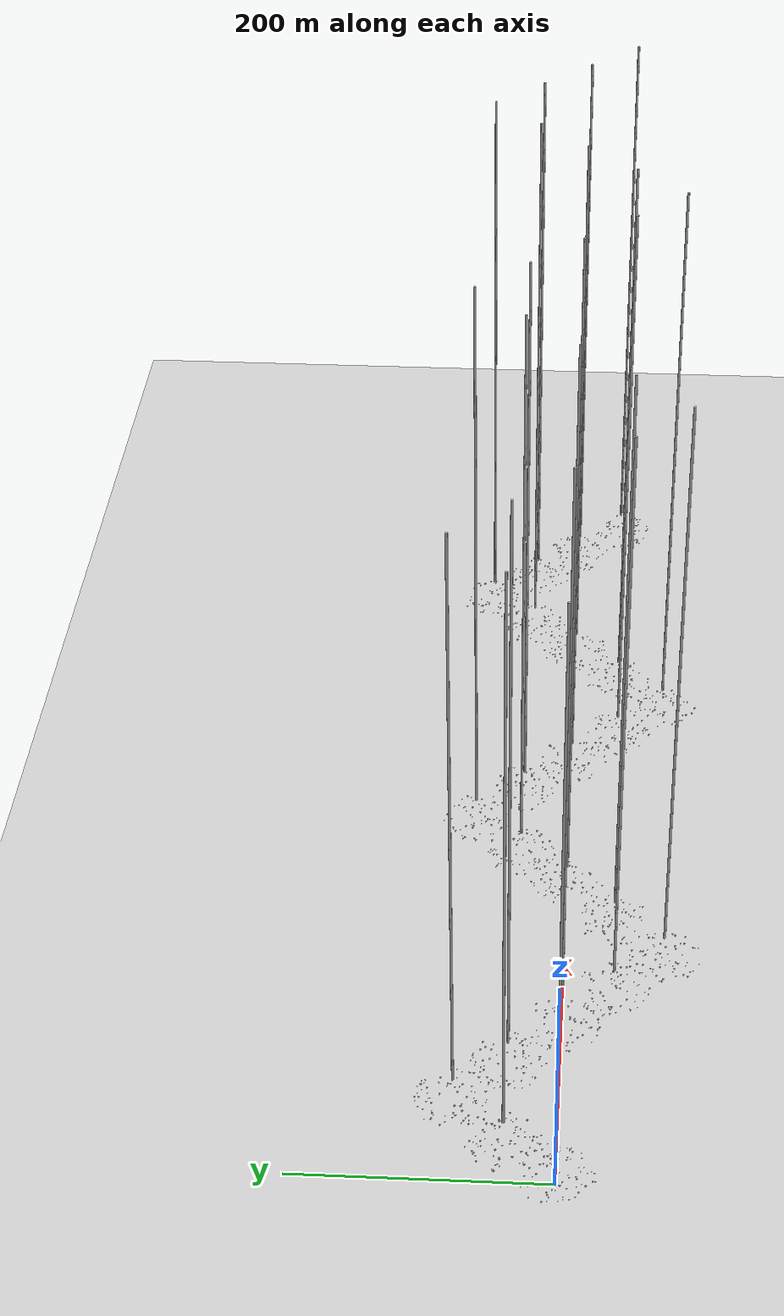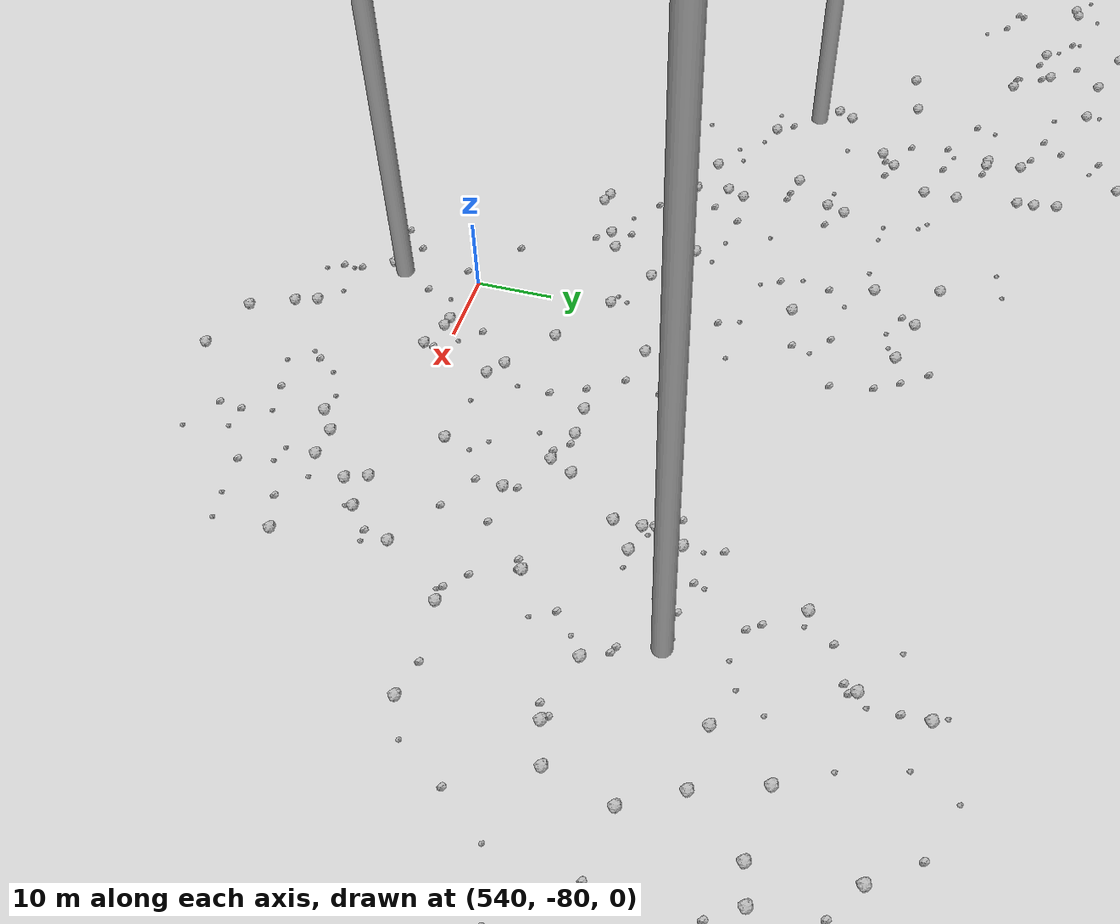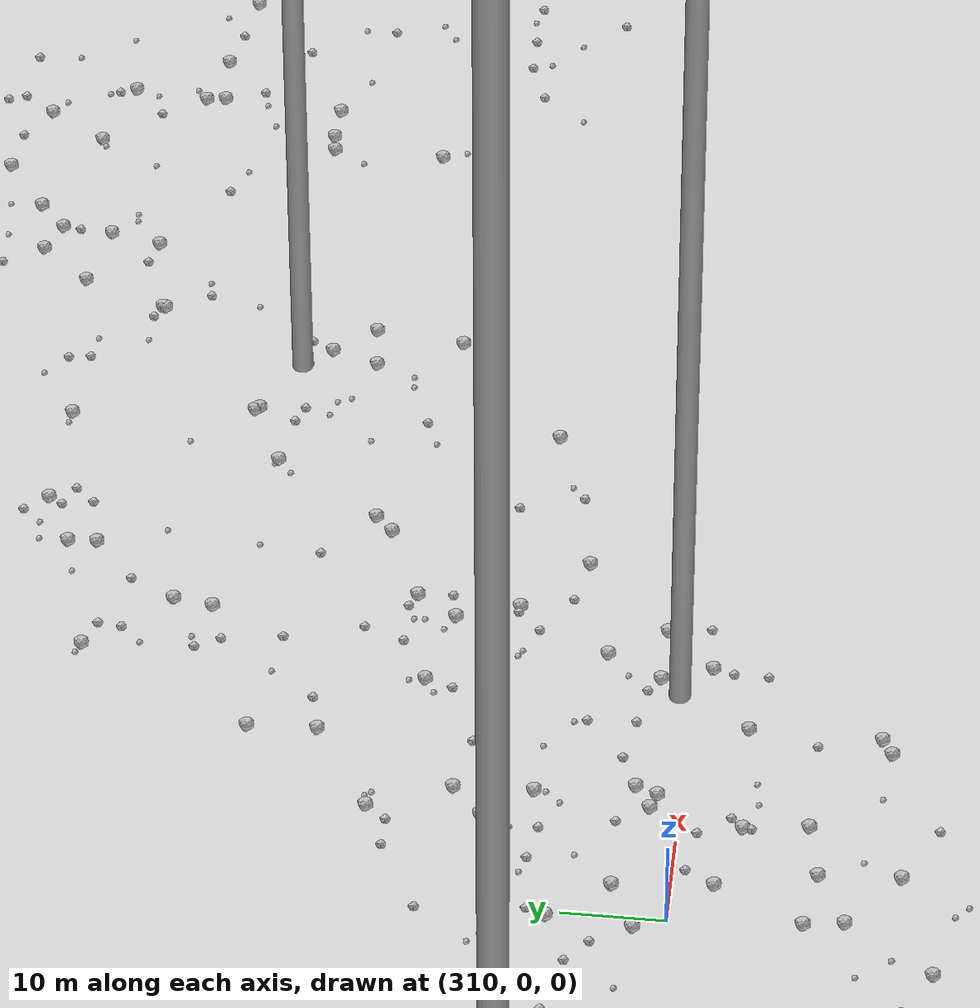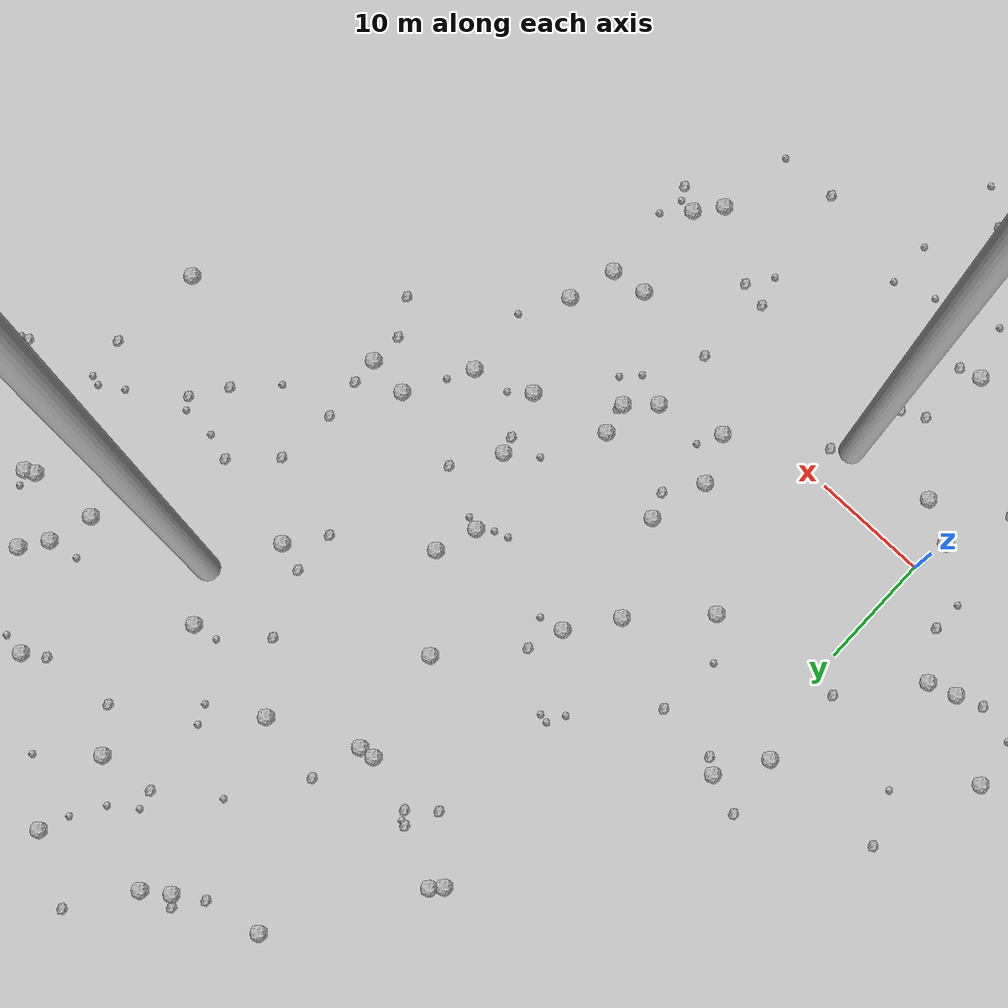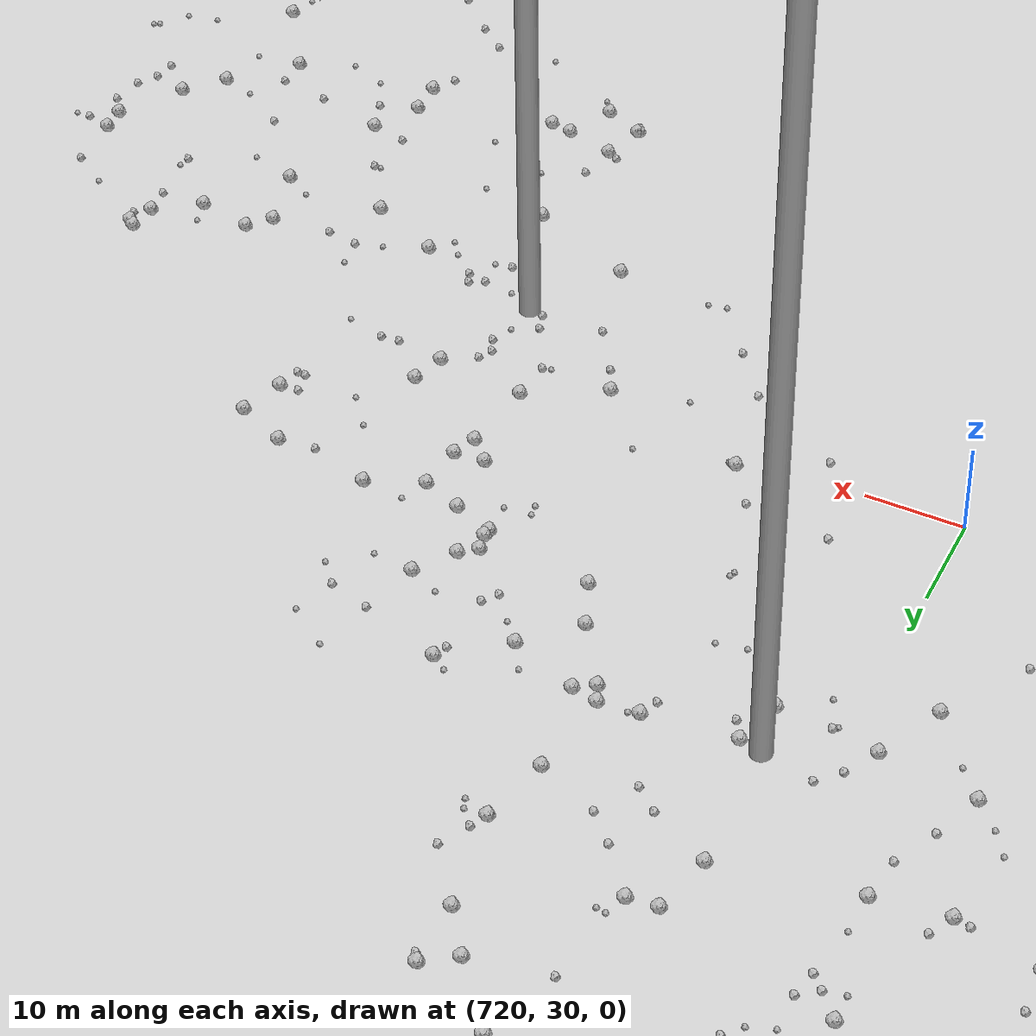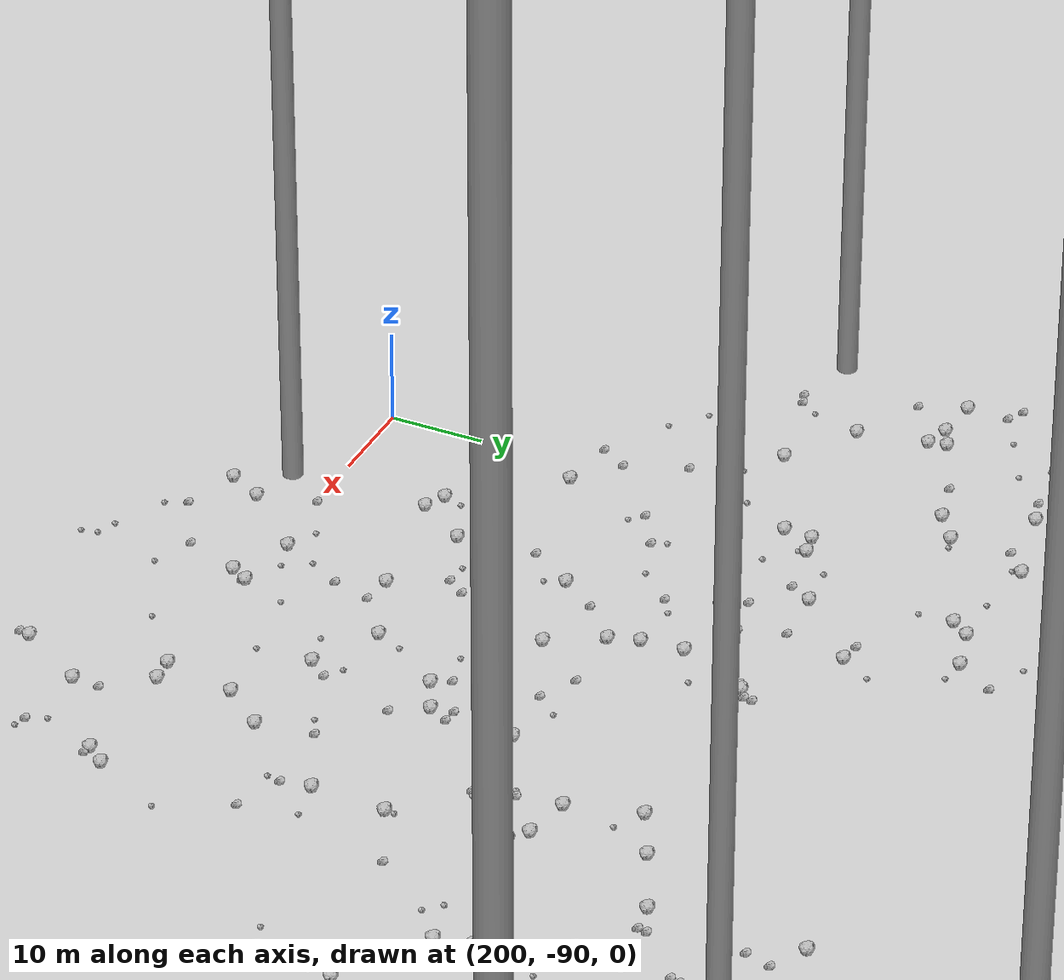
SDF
<sdf version="1.6">
 <world name="default">
  <include><uri>model://custom_ground</uri></include>
  <include><uri>model://sun</uri></include>
  <spherical_coordinates>
   <surface_model>EARTH_WGS84</surface_model>
   <latitude_deg>38.161479</latitude_deg>
   <longitude_deg>-122.454630</longitude_deg>
   <elevation>488.0</elevation>
   <heading_deg>90</heading_deg>
  </spherical_coordinates>
  <model name="rock1_0_0">
   <include><uri>model://rock1</uri><pose>-9.551726560826815 5.658364170545845 0.5 0 0 0</pose></include>
  </model>
  <model name="rock1_0_1">
   <include><uri>model://rock1</uri><pose>6.525494328169753 -15.528129669238202 0.5 0 0 0</pose></include>
  </model>
  <model name="rock1_0_2">
   <include><uri>model://rock1</uri><pose>14.978238811556729 19.59930031675478 0.5 0 0 0</pose></include>
  </model>
  <model name="rock1_0_3">
   <include><uri>model://rock1</uri><pose>35.173844090567314 -1.4398469227814665 0.5 0 0 0</pose></include>
  </model>
  <model name="rock1_0_4">
   <include><uri>model://rock1</uri><pose>17.903144709683914 23.66732824782293 0.5 0 0 0</pose></include>
  </model>
  <model name="rock1_0_5">
   <include><uri>model://rock1</uri><pose>4.657105373161706 -27.478541318918516 0.5 0 0 0</pose></include>
  </model>
  <model name="rock1_0_6">
   <include><uri>model://rock1</uri><pose>24.757668048360884 4.340254648814792 0.5 0 0 0</pose></include>
  </model>
  <model name="rock1_0_7">
   <include><uri>model://rock1</uri><pose>-5.961700583877445 -17.111554562166315 0.5 0 0 0</pose></include>
  </model>
  <model name="rock1_0_8">
   <include><uri>model://rock1</uri><pose>32.09557068831104 -1.8662773400095176 0.5 0 0 0</pose></include>
  </model>
  <model name="rock1_0_9">
   <include><uri>model://rock1</uri><pose>28.84026890550205 22.363350226917788 0.5 0 0 0</pose></include>
  </model>
  <model name="rock1_0_10">
   <include><uri>model://rock1</uri><pose>32.05394939986874 -11.825418559368089 0.5 0 0 0</pose></include>
  </model>
  <model name="rock1_0_11">
   <include><uri>model://rock1</uri><pose>18.7097731202906 11.778567993993775 0.5 0 0 0</pose></include>
  </model>
  <model name="rock1_0_12">
   <include><uri>model://rock1</uri><pose>-15.896420309960842 9.810015975268527 0.5 0 0 0</pose></include>
  </model>
  <model name="rock1_0_13">
   <include><uri>model://rock1</uri><pose>9.434874660676662 14.064862368814445 0.5 0 0 0</pose></include>
  </model>
  <model name="rock1_0_14">
   <include><uri>model://rock1</uri><pose>-0.02960096387186084 -22.165018221034458 0.5 0 0 0</pose></include>
  </model>
  <model name="rock1_0_15">
   <include><uri>model://rock1</uri><pose>33.09887189784094 10.725748791118697 0.5 0 0 0</pose></include>
  </model>
  <model name="rock1_0_16">
   <include><uri>model://rock1</uri><pose>2.933327695562589 -4.941073363136727 0.5 0 0 0</pose></include>
  </model>
  <model name="rock1_0_17">
   <include><uri>model://rock1</uri><pose>26.369798298200188 9.057177148235965 0.5 0 0 0</pose></include>
  </model>
  <model name="rock1_0_18">
   <include><uri>model://rock1</uri><pose>19.15200294798973 2.5899990601920706 0.5 0 0 0</pose></include>
  </model>
  <model name="rock1_0_19">
   <include><uri>model://rock1</uri><pose>26.951856075820388 6.385992832944176 0.5 0 0 0</pose></include>
  </model>
  <model name="rock1_0_20">
   <include><uri>model://rock1</uri><pose>0.7873363466603003 24.07229664766971 0.5 0 0 0</pose></include>
  </model>
  <model name="rock1_0_21">
   <include><uri>model://rock1</uri><pose>-0.5725116038871612 -3.1469100808864177 0.5 0 0 0</pose></include>
  </model>
  <model name="rock1_0_22">
   <include><uri>model://rock1</uri><pose>36.31542387867218 2.6972559976155424 0.5 0 0 0</pose></include>
  </model>
  <model name="rock1_0_23">
   <include><uri>model://rock1</uri><pose>-7.152741680136149 6.438192470695547 0.5 0 0 0</pose></include>
  </model>
  <model name="rock1_0_24">
   <include><uri>model://rock1</uri><pose>33.75240878094792 -9.752561160526604 0.5 0 0 0</pose></include>
  </model>
  <model name="rock1_0_25">
   <include><uri>model://rock1</uri><pose>-1.8262302441712137 19.959202153039342 0.5 0 0 0</pose></include>
  </model>
  <model name="rock1_0_26">
   <include><uri>model://rock1</uri><pose>17.466065402417648 6.623176181134468 0.5 0 0 0</pose></include>
  </model>
  <model name="rock2_0_0">
   <include><uri>model://rock2</uri><pose>-2.1076209854782633 12.545652631384016 0.3 0 0 0</pose></include>
  </model>
  <model name="rock2_0_1">
   <include><uri>model://rock2</uri><pose>-12.767681102007112 19.478969545818238 0.3 0 0 0</pose></include>
  </model>
  <model name="rock2_0_2">
   <include><uri>model://rock2</uri><pose>4.556087843798082 -29.213374631738358 0.3 0 0 0</pose></include>
  </model>
  <model name="rock2_0_3">
   <include><uri>model://rock2</uri><pose>7.3598117831130345 22.791673015682278 0.3 0 0 0</pose></include>
  </model>
  <model name="rock2_0_4">
   <include><uri>model://rock2</uri><pose>26.319278064421226 -8.161043997304347 0.3 0 0 0</pose></include>
  </model>
  <model name="rock2_0_5">
   <include><uri>model://rock2</uri><pose>9.611140949476141 -8.977769120030633 0.3 0 0 0</pose></include>
  </model>
  <model name="rock2_0_6">
   <include><uri>model://rock2</uri><pose>26.07126488731342 -18.678094918892505 0.3 0 0 0</pose></include>
  </model>
  <model name="rock2_0_7">
   <include><uri>model://rock2</uri><pose>-12.988371466282594 -10.424023336573804 0.3 0 0 0</pose></include>
  </model>
  <model name="rock2_0_8">
   <include><uri>model://rock2</uri><pose>8.370936616293509 -14.998560017986923 0.3 0 0 0</pose></include>
  </model>
  <model name="rock2_0_9">
   <include><uri>model://rock2</uri><pose>27.040090203728525 6.8873130443278185 0.3 0 0 0</pose></include>
  </model>
  <model name="rock2_0_10">
   <include><uri>model://rock2</uri><pose>24.083539014647627 -7.7410710448314966 0.3 0 0 0</pose></include>
  </model>
  <model name="rock2_0_11">
   <include><uri>model://rock2</uri><pose>11.75579595320636 -2.601002839735248 0.3 0 0 0</pose></include>
  </model>
  <model name="rock2_0_12">
   <include><uri>model://rock2</uri><pose>13.886342731963971 -26.20481341159381 0.3 0 0 0</pose></include>
  </model>
  <model name="rock2_0_13">
   <include><uri>model://rock2</uri><pose>-13.11695526625639 -5.973105190903468 0.3 0 0 0</pose></include>
  </model>
  <model name="rock2_0_14">
   <include><uri>model://rock2</uri><pose>31.917226511826918 14.69716209436087 0.3 0 0 0</pose></include>
  </model>
  <model name="rock2_0_15">
   <include><uri>model://rock2</uri><pose>-10.525159330953382 -14.584941271871251 0.3 0 0 0</pose></include>
  </model>
  <model name="rock2_0_16">
   <include><uri>model://rock2</uri><pose>-4.683761400695573 2.6118200227654853 0.3 0 0 0</pose></include>
  </model>
  <model name="rock2_0_17">
   <include><uri>model://rock2</uri><pose>12.411701760987732 -28.290305317013708 0.3 0 0 0</pose></include>
  </model>
  <model name="rock2_0_18">
   <include><uri>model://rock2</uri><pose>-2.6362068851392024 25.287541088376116 0.3 0 0 0</pose></include>
  </model>
  <model name="rock2_0_19">
   <include><uri>model://rock2</uri><pose>19.571530732457212 9.632664131395835 0.3 0 0 0</pose></include>
  </model>
  <model name="rock2_0_20">
   <include><uri>model://rock2</uri><pose>7.658739192554798 -9.954902807704599 0.3 0 0 0</pose></include>
  </model>
  <model name="rock2_0_21">
   <include><uri>model://rock2</uri><pose>-11.826903979004372 4.853959233063065 0.3 0 0 0</pose></include>
  </model>
  <model name="rock2_0_22">
   <include><uri>model://rock2</uri><pose>1.4740446867495223 -19.00852634217297 0.3 0 0 0</pose></include>
  </model>
  <model name="rock2_0_23">
   <include><uri>model://rock2</uri><pose>1.9414424661179481 23.159034099023152 0.3 0 0 0</pose></include>
  </model>
  <model name="rock2_0_24">
   <include><uri>model://rock2</uri><pose>24.72394510151996 -1.318942919640996 0.3 0 0 0</pose></include>
  </model>
  <model name="rock2_0_25">
   <include><uri>model://rock2</uri><pose>-3.033040224024621 -8.527124351589567 0.3 0 0 0</pose></include>
  </model>
  <model name="rock2_0_26">
   <include><uri>model://rock2</uri><pose>35.697816363103854 -10.879739896210367 0.3 0 0 0</pose></include>
  </model>
  <model name="rock3_0_0">
   <include><uri>model://rock3</uri><pose>6.857569436498586 17.186086094452627 0.2 0 0 0</pose></include>
  </model>
  <model name="rock3_0_1">
   <include><uri>model://rock3</uri><pose>-0.8072237528325452 -15.710096379560248 0.2 0 0 0</pose></include>
  </model>
  <model name="rock3_0_2">
   <include><uri>model://rock3</uri><pose>-15.261874115451937 5.598008568532457 0.2 0 0 0</pose></include>
  </model>
  <model name="rock3_0_3">
   <include><uri>model://rock3</uri><pose>19.930850184135203 24.109246118672388 0.2 0 0 0</pose></include>
  </model>
  <model name="rock3_0_4">
   <include><uri>model://rock3</uri><pose>38.56439440033748 6.610501055208907 0.2 0 0 0</pose></include>
  </model>
  <model name="rock3_0_5">
   <include><uri>model://rock3</uri><pose>8.139352126609097 -19.862201073627894 0.2 0 0 0</pose></include>
  </model>
  <model name="rock3_0_6">
   <include><uri>model://rock3</uri><pose>-14.862051675257932 -2.4933888170265988 0.2 0 0 0</pose></include>
  </model>
  <model name="rock3_0_7">
   <include><uri>model://rock3</uri><pose>34.77491705332481 12.082652091160583 0.2 0 0 0</pose></include>
  </model>
  <model name="rock3_0_8">
   <include><uri>model://rock3</uri><pose>12.883758954142358 28.661326973318253 0.2 0 0 0</pose></include>
  </model>
  <model name="rock3_0_9">
   <include><uri>model://rock3</uri><pose>-10.625580920443117 -5.611362273261538 0.2 0 0 0</pose></include>
  </model>
  <model name="rock3_0_10">
   <include><uri>model://rock3</uri><pose>-4.7626765661546795 -0.03518848980827727 0.2 0 0 0</pose></include>
  </model>
  <model name="rock3_0_11">
   <include><uri>model://rock3</uri><pose>13.767060299398786 -18.05469362927733 0.2 0 0 0</pose></include>
  </model>
  <model name="rock3_0_12">
   <include><uri>model://rock3</uri><pose>20.185436144791204 4.607046309043568 0.2 0 0 0</pose></include>
  </model>
  <model name="rock3_0_13">
   <include><uri>model://rock3</uri><pose>35.029476537297285 -9.846214075150428 0.2 0 0 0</pose></include>
  </model>
  <model name="rock3_0_14">
   <include><uri>model://rock3</uri><pose>28.97969410188292 14.266359352060938 0.2 0 0 0</pose></include>
  </model>
  <model name="rock3_0_15">
   <include><uri>model://rock3</uri><pose>17.367237325954186 -20.732076095635854 0.2 0 0 0</pose></include>
  </model>
  <model name="rock3_0_16">
   <include><uri>model://rock3</uri><pose>24.84519927125511 -10.293226176292332 0.2 0 0 0</pose></include>
  </model>
  <model name="rock3_0_17">
   <include><uri>model://rock3</uri><pose>-4.326202226821323 -25.637036585316903 0.2 0 0 0</pose></include>
  </model>
  <model name="rock3_0_18">
   <include><uri>model://rock3</uri><pose>31.03470340594386 -18.507471046598482 0.2 0 0 0</pose></include>
  </model>
  <model name="rock3_0_19">
   <include><uri>model://rock3</uri><pose>35.666425594369905 -7.7851089934445525 0.2 0 0 0</pose></include>
  </model>
  <model name="rock3_0_20">
   <include><uri>model://rock3</uri><pose>17.27072639034104 -16.792923354502673 0.2 0 0 0</pose></include>
  </model>
  <model name="rock3_0_21">
   <include><uri>model://rock3</uri><pose>12.412783287404352 -23.031559995582924 0.2 0 0 0</pose></include>
  </model>
  <model name="rock3_0_22">
   <include><uri>model://rock3</uri><pose>27.42435690656118 3.386825101585181 0.2 0 0 0</pose></include>
  </model>
  <model name="rock3_0_23">
   <include><uri>model://rock3</uri><pose>28.760649714226886 4.788357324406022 0.2 0 0 0</pose></include>
  </model>
  <model name="rock3_0_24">
   <include><uri>model://rock3</uri><pose>16.71590593116848 -28.45673172582574 0.2 0 0 0</pose></include>
  </model>
  <model name="rock3_0_25">
   <include><uri>model://rock3</uri><pose>11.27764883398931 -13.068401816985904 0.2 0 0 0</pose></include>
  </model>
  <model name="rock3_0_26">
   <include><uri>model://rock3</uri><pose>-10.754859549382656 15.177114149350245 0.2 0 0 0</pose></include>
  </model>
  <model name="rock1_1_0">
   <include><uri>model://rock1</uri><pose>38.293750052957165 64.8169003198368 0.5 0 0 0</pose></include>
  </model>
  <model name="rock1_1_1">
   <include><uri>model://rock1</uri><pose>19.310359379566748 58.707568096000145 0.5 0 0 0</pose></include>
  </model>
  <model name="rock1_1_2">
   <include><uri>model://rock1</uri><pose>30.957931551430043 45.49739689679582 0.5 0 0 0</pose></include>
  </model>
  <model name="rock1_1_3">
   <include><uri>model://rock1</uri><pose>41.19106659664972 18.10488671525836 0.5 0 0 0</pose></include>
  </model>
  <model name="rock1_1_4">
   <include><uri>model://rock1</uri><pose>38.07366403655713 12.581499670678369 0.5 0 0 0</pose></include>
  </model>
  <model name="rock1_1_5">
   <include><uri>model://rock1</uri><pose>55.703607291978386 49.19061932599775 0.5 0 0 0</pose></include>
  </model>
  <model name="rock1_1_6">
   <include><uri>model://rock1</uri><pose>26.703752643753035 61.23611456125548 0.5 0 0 0</pose></include>
  </model>
  <model name="rock1_1_7">
   <include><uri>model://rock1</uri><pose>30.087240580912813 25.916230336444542 0.5 0 0 0</pose></include>
  </model>
  <model name="rock1_1_8">
   <include><uri>model://rock1</uri><pose>55.82852986167293 53.16505199142829 0.5 0 0 0</pose></include>
  </model>
  <model name="rock1_1_9">
   <include><uri>model://rock1</uri><pose>60.85055797732981 22.832701517441116 0.5 0 0 0</pose></include>
  </model>
  <model name="rock1_1_10">
   <include><uri>model://rock1</uri><pose>23.558979383234192 42.07915570515389 0.5 0 0 0</pose></include>
  </model>
  <model name="rock1_1_11">
   <include><uri>model://rock1</uri><pose>49.42679646462816 55.35857984023106 0.5 0 0 0</pose></include>
  </model>
  <model name="rock1_1_12">
   <include><uri>model://rock1</uri><pose>10.749346471848522 45.72744651096918 0.5 0 0 0</pose></include>
  </model>
  <model name="rock1_1_13">
   <include><uri>model://rock1</uri><pose>39.829013329433465 34.13333640139152 0.5 0 0 0</pose></include>
  </model>
  <model name="rock1_1_14">
   <include><uri>model://rock1</uri><pose>54.15221417865885 47.02186484921391 0.5 0 0 0</pose></include>
  </model>
  <model name="rock1_1_15">
   <include><uri>model://rock1</uri><pose>22.21694675292314 41.90777890432376 0.5 0 0 0</pose></include>
  </model>
  <model name="rock1_1_16">
   <include><uri>model://rock1</uri><pose>11.593468620582371 46.62512349408083 0.5 0 0 0</pose></include>
  </model>
  <model name="rock1_1_17">
   <include><uri>model://rock1</uri><pose>53.022117573879356 43.256735751263726 0.5 0 0 0</pose></include>
  </model>
  <model name="rock1_1_18">
   <include><uri>model://rock1</uri><pose>58.944183925083856 43.75559062965163 0.5 0 0 0</pose></include>
  </model>
  <model name="rock1_1_19">
   <include><uri>model://rock1</uri><pose>38.66813473508577 56.88736888430669 0.5 0 0 0</pose></include>
  </model>
  <model name="rock1_1_20">
   <include><uri>model://rock1</uri><pose>59.762192011603304 44.16970718629507 0.5 0 0 0</pose></include>
  </model>
  <model name="rock1_1_21">
   <include><uri>model://rock1</uri><pose>24.48055722831935 32.62334026698407 0.5 0 0 0</pose></include>
  </model>
  <model name="rock1_1_22">
   <include><uri>model://rock1</uri><pose>44.7595869647964 17.7623932175057 0.5 0 0 0</pose></include>
  </model>
  <model name="rock1_1_23">
   <include><uri>model://rock1</uri><pose>59.887102178932594 55.349224045736975 0.5 0 0 0</pose></include>
  </model>
  <model name="rock1_1_24">
   <include><uri>model://rock1</uri><pose>40.55032491353019 43.96968331525643 0.5 0 0 0</pose></include>
  </model>
  <model name="rock1_1_25">
   <include><uri>model://rock1</uri><pose>28.818893433756617 62.76737222801135 0.5 0 0 0</pose></include>
  </model>
  <model name="rock1_1_26">
   <include><uri>model://rock1</uri><pose>31.493529335776202 16.12919188104721 0.5 0 0 0</pose></include>
  </model>
  <model name="rock2_1_0">
   <include><uri>model://rock2</uri><pose>33.7950810920844 56.333747394527684 0.3 0 0 0</pose></include>
  </model>
  <model name="rock2_1_1">
   <include><uri>model://rock2</uri><pose>25.96493938289349 62.01926062124804 0.3 0 0 0</pose></include>
  </model>
  <model name="rock2_1_2">
   <include><uri>model://rock2</uri><pose>44.62590433017364 14.906044861940336 0.3 0 0 0</pose></include>
  </model>
  <model name="rock2_1_3">
   <include><uri>model://rock2</uri><pose>15.238458174269953 41.49305203435951 0.3 0 0 0</pose></include>
  </model>
  <model name="rock2_1_4">
   <include><uri>model://rock2</uri><pose>17.3924956460382 43.354108086623896 0.3 0 0 0</pose></include>
  </model>
  <model name="rock2_1_5">
   <include><uri>model://rock2</uri><pose>34.09921189101589 19.989328966076545 0.3 0 0 0</pose></include>
  </model>
  <model name="rock2_1_6">
   <include><uri>model://rock2</uri><pose>44.275447518754746 23.670100465936322 0.3 0 0 0</pose></include>
  </model>
  <model name="rock2_1_7">
   <include><uri>model://rock2</uri><pose>18.96714786589687 26.69991826516628 0.3 0 0 0</pose></include>
  </model>
  <model name="rock2_1_8">
   <include><uri>model://rock2</uri><pose>44.805086093262666 28.901856621124484 0.3 0 0 0</pose></include>
  </model>
  <model name="rock2_1_9">
   <include><uri>model://rock2</uri><pose>37.36960359368669 34.86191351518181 0.3 0 0 0</pose></include>
  </model>
  <model name="rock2_1_10">
   <include><uri>model://rock2</uri><pose>48.179792700485415 32.21215120909668 0.3 0 0 0</pose></include>
  </model>
  <model name="rock2_1_11">
   <include><uri>model://rock2</uri><pose>67.81707556484247 36.377955285794414 0.3 0 0 0</pose></include>
  </model>
  <model name="rock2_1_12">
   <include><uri>model://rock2</uri><pose>67.20568743625564 36.01302126240367 0.3 0 0 0</pose></include>
  </model>
  <model name="rock2_1_13">
   <include><uri>model://rock2</uri><pose>44.66095833787836 20.12753838345844 0.3 0 0 0</pose></include>
  </model>
  <model name="rock2_1_14">
   <include><uri>model://rock2</uri><pose>41.21298800953152 53.56287191842375 0.3 0 0 0</pose></include>
  </model>
  <model name="rock2_1_15">
   <include><uri>model://rock2</uri><pose>24.741777910431306 46.573480585305894 0.3 0 0 0</pose></include>
  </model>
  <model name="rock2_1_16">
   <include><uri>model://rock2</uri><pose>54.05559333874754 30.43193267633471 0.3 0 0 0</pose></include>
  </model>
  <model name="rock2_1_17">
   <include><uri>model://rock2</uri><pose>35.02725349270763 40.337724661052164 0.3 0 0 0</pose></include>
  </model>
  <model name="rock2_1_18">
   <include><uri>model://rock2</uri><pose>46.42232470291774 11.885368810726991 0.3 0 0 0</pose></include>
  </model>
  <model name="rock2_1_19">
   <include><uri>model://rock2</uri><pose>24.272166963983747 59.72136393148794 0.3 0 0 0</pose></include>
  </model>
  <model name="rock2_1_20">
   <include><uri>model://rock2</uri><pose>32.454840879585404 68.17809119615208 0.3 0 0 0</pose></include>
  </model>
  <model name="rock2_1_21">
   <include><uri>model://rock2</uri><pose>37.429124891645344 30.970149963593457 0.3 0 0 0</pose></include>
  </model>
  <model name="rock2_1_22">
   <include><uri>model://rock2</uri><pose>61.614258348297255 31.03137865528962 0.3 0 0 0</pose></include>
  </model>
  <model name="rock2_1_23">
   <include><uri>model://rock2</uri><pose>52.047369264005944 27.547769081182846 0.3 0 0 0</pose></include>
  </model>
  <model name="rock2_1_24">
   <include><uri>model://rock2</uri><pose>16.514972481397685 44.26070511462954 0.3 0 0 0</pose></include>
  </model>
  <model name="rock2_1_25">
   <include><uri>model://rock2</uri><pose>61.75609011564777 38.75401756435639 0.3 0 0 0</pose></include>
  </model>
  <model name="rock2_1_26">
   <include><uri>model://rock2</uri><pose>47.614072637184144 54.195668618370355 0.3 0 0 0</pose></include>
  </model>
  <model name="rock3_1_0">
   <include><uri>model://rock3</uri><pose>38.357526738839795 43.598074603200594 0.2 0 0 0</pose></include>
  </model>
  <model name="rock3_1_1">
   <include><uri>model://rock3</uri><pose>61.10160824466901 34.575206926411475 0.2 0 0 0</pose></include>
  </model>
  <model name="rock3_1_2">
   <include><uri>model://rock3</uri><pose>29.911832779849945 21.96865503191956 0.2 0 0 0</pose></include>
  </model>
  <model name="rock3_1_3">
   <include><uri>model://rock3</uri><pose>48.95682664715251 24.376588181894547 0.2 0 0 0</pose></include>
  </model>
  <model name="rock3_1_4">
   <include><uri>model://rock3</uri><pose>16.938672750441462 44.100661739869 0.2 0 0 0</pose></include>
  </model>
  <model name="rock3_1_5">
   <include><uri>model://rock3</uri><pose>51.32447391326996 55.092040647380415 0.2 0 0 0</pose></include>
  </model>
  <model name="rock3_1_6">
   <include><uri>model://rock3</uri><pose>39.20583421893261 14.70528698531963 0.2 0 0 0</pose></include>
  </model>
  <model name="rock3_1_7">
   <include><uri>model://rock3</uri><pose>42.97168936203277 60.70071181853366 0.2 0 0 0</pose></include>
  </model>
  <model name="rock3_1_8">
   <include><uri>model://rock3</uri><pose>65.63566636043672 41.734743229612604 0.2 0 0 0</pose></include>
  </model>
  <model name="rock3_1_9">
   <include><uri>model://rock3</uri><pose>55.41552630480903 62.92649267619607 0.2 0 0 0</pose></include>
  </model>
  <model name="rock3_1_10">
   <include><uri>model://rock3</uri><pose>58.31749038883156 33.57883750950904 0.2 0 0 0</pose></include>
  </model>
  <model name="rock3_1_11">
   <include><uri>model://rock3</uri><pose>35.35746673456153 48.109917656220475 0.2 0 0 0</pose></include>
  </model>
  <model name="rock3_1_12">
   <include><uri>model://rock3</uri><pose>53.372585459967524 31.38310210005457 0.2 0 0 0</pose></include>
  </model>
  <model name="rock3_1_13">
   <include><uri>model://rock3</uri><pose>50.44403386197539 31.482448027531046 0.2 0 0 0</pose></include>
  </model>
  <model name="rock3_1_14">
   <include><uri>model://rock3</uri><pose>61.04878202237063 59.99308648846973 0.2 0 0 0</pose></include>
  </model>
  <model name="rock3_1_15">
   <include><uri>model://rock3</uri><pose>51.51431388721604 46.55515169152967 0.2 0 0 0</pose></include>
  </model>
  <model name="rock3_1_16">
   <include><uri>model://rock3</uri><pose>60.248729134461634 34.83185596879146 0.2 0 0 0</pose></include>
  </model>
  <model name="rock3_1_17">
   <include><uri>model://rock3</uri><pose>33.36494138535329 57.98328139464461 0.2 0 0 0</pose></include>
  </model>
  <model name="rock3_1_18">
   <include><uri>model://rock3</uri><pose>34.63245924316577 49.734967515600665 0.2 0 0 0</pose></include>
  </model>
  <model name="rock3_1_19">
   <include><uri>model://rock3</uri><pose>28.895581850333997 52.720731964449314 0.2 0 0 0</pose></include>
  </model>
  <model name="rock3_1_20">
   <include><uri>model://rock3</uri><pose>26.40566960245534 21.031521174337744 0.2 0 0 0</pose></include>
  </model>
  <model name="rock3_1_21">
   <include><uri>model://rock3</uri><pose>37.22736772398764 62.331310326058954 0.2 0 0 0</pose></include>
  </model>
  <model name="rock3_1_22">
   <include><uri>model://rock3</uri><pose>59.18460105737955 45.365711907715074 0.2 0 0 0</pose></include>
  </model>
  <model name="rock3_1_23">
   <include><uri>model://rock3</uri><pose>35.54217479937589 59.5939774095011 0.2 0 0 0</pose></include>
  </model>
  <model name="rock3_1_24">
   <include><uri>model://rock3</uri><pose>14.473275472323659 29.991794584985858 0.2 0 0 0</pose></include>
  </model>
  <model name="rock3_1_25">
   <include><uri>model://rock3</uri><pose>27.588582027348757 21.404017104536717 0.2 0 0 0</pose></include>
  </model>
  <model name="rock3_1_26">
   <include><uri>model://rock3</uri><pose>13.677015945908222 30.138483364829423 0.2 0 0 0</pose></include>
  </model>
  <model name="rock1_2_0">
   <include><uri>model://rock1</uri><pose>79.63552000081847 105.75339505664516 0.5 0 0 0</pose></include>
  </model>
  <model name="rock1_2_1">
   <include><uri>model://rock1</uri><pose>89.19399269644379 100.22350047223966 0.5 0 0 0</pose></include>
  </model>
  <model name="rock1_2_2">
   <include><uri>model://rock1</uri><pose>99.85446333909934 90.42893771084943 0.5 0 0 0</pose></include>
  </model>
  <model name="rock1_2_3">
   <include><uri>model://rock1</uri><pose>77.6913858414064 62.45587638444289 0.5 0 0 0</pose></include>
  </model>
  <model name="rock1_2_4">
   <include><uri>model://rock1</uri><pose>83.19213197636444 90.37991510009533 0.5 0 0 0</pose></include>
  </model>
  <model name="rock1_2_5">
   <include><uri>model://rock1</uri><pose>52.57286785486805 88.34421881636192 0.5 0 0 0</pose></include>
  </model>
  <model name="rock1_2_6">
   <include><uri>model://rock1</uri><pose>85.8205062943276 76.8273122202334 0.5 0 0 0</pose></include>
  </model>
  <model name="rock1_2_7">
   <include><uri>model://rock1</uri><pose>93.83649083988128 84.66632472421807 0.5 0 0 0</pose></include>
  </model>
  <model name="rock1_2_8">
   <include><uri>model://rock1</uri><pose>64.51758101204857 78.61609453463795 0.5 0 0 0</pose></include>
  </model>
  <model name="rock1_2_9">
   <include><uri>model://rock1</uri><pose>57.64957430701076 70.54795946729064 0.5 0 0 0</pose></include>
  </model>
  <model name="rock1_2_10">
   <include><uri>model://rock1</uri><pose>72.06710086706346 78.15763054192708 0.5 0 0 0</pose></include>
  </model>
  <model name="rock1_2_11">
   <include><uri>model://rock1</uri><pose>73.83121051390647 95.81642152076132 0.5 0 0 0</pose></include>
  </model>
  <model name="rock1_2_12">
   <include><uri>model://rock1</uri><pose>67.22852899081823 72.1152990875067 0.5 0 0 0</pose></include>
  </model>
  <model name="rock1_2_13">
   <include><uri>model://rock1</uri><pose>71.83589275817755 73.69439043836886 0.5 0 0 0</pose></include>
  </model>
  <model name="rock1_2_14">
   <include><uri>model://rock1</uri><pose>62.73695267593149 76.87873382531082 0.5 0 0 0</pose></include>
  </model>
  <model name="rock1_2_15">
   <include><uri>model://rock1</uri><pose>105.65138897774443 65.4442881247877 0.5 0 0 0</pose></include>
  </model>
  <model name="rock1_2_16">
   <include><uri>model://rock1</uri><pose>93.73041882984933 73.30309148081346 0.5 0 0 0</pose></include>
  </model>
  <model name="rock1_2_17">
   <include><uri>model://rock1</uri><pose>58.510844959846864 94.96970786803459 0.5 0 0 0</pose></include>
  </model>
  <model name="rock1_2_18">
   <include><uri>model://rock1</uri><pose>87.45101492078393 55.34449351369889 0.5 0 0 0</pose></include>
  </model>
  <model name="rock1_2_19">
   <include><uri>model://rock1</uri><pose>62.805712795487366 67.09174628803075 0.5 0 0 0</pose></include>
  </model>
  <model name="rock1_2_20">
   <include><uri>model://rock1</uri><pose>61.784318764789504 59.90272389970837 0.5 0 0 0</pose></include>
  </model>
  <model name="rock1_2_21">
   <include><uri>model://rock1</uri><pose>79.60725900242011 109.06370204539607 0.5 0 0 0</pose></include>
  </model>
  <model name="rock1_2_22">
   <include><uri>model://rock1</uri><pose>92.39528120833853 105.22934680580082 0.5 0 0 0</pose></include>
  </model>
  <model name="rock1_2_23">
   <include><uri>model://rock1</uri><pose>101.75153501514298 61.304860443222466 0.5 0 0 0</pose></include>
  </model>
  <model name="rock1_2_24">
   <include><uri>model://rock1</uri><pose>54.93179240232318 66.71901187327421 0.5 0 0 0</pose></include>
  </model>
  <model name="rock1_2_25">
   <include><uri>model://rock1</uri><pose>63.84362068696047 94.3100830217358 0.5 0 0 0</pose></include>
  </model>
  <model name="rock1_2_26">
   <include><uri>model://rock1</uri><pose>81.21294792295669 69.26564771702388 0.5 0 0 0</pose></include>
  </model>
  <model name="rock2_2_0">
   <include><uri>model://rock2</uri><pose>60.368056981410376 79.05668457364686 0.3 0 0 0</pose></include>
  </model>
  <model name="rock2_2_1">
   <include><uri>model://rock2</uri><pose>91.53655659011869 85.41142158751225 0.3 0 0 0</pose></include>
  </model>
  <model name="rock2_2_2">
   <include><uri>model://rock2</uri><pose>74.42857146578186 72.9360701702587 0.3 0 0 0</pose></include>
  </model>
  <model name="rock2_2_3">
   <include><uri>model://rock2</uri><pose>97.40956473908946 102.39254812519924 0.3 0 0 0</pose></include>
  </model>
  <model name="rock2_2_4">
   <include><uri>model://rock2</uri><pose>106.03210740610183 68.25934300612619 0.3 0 0 0</pose></include>
  </model>
  <model name="rock2_2_5">
   <include><uri>model://rock2</uri><pose>67.52285336764106 101.69176536647498 0.3 0 0 0</pose></include>
  </model>
  <model name="rock2_2_6">
   <include><uri>model://rock2</uri><pose>57.69076839606012 95.41631371929415 0.3 0 0 0</pose></include>
  </model>
  <model name="rock2_2_7">
   <include><uri>model://rock2</uri><pose>69.81221678226822 105.9865709199838 0.3 0 0 0</pose></include>
  </model>
  <model name="rock2_2_8">
   <include><uri>model://rock2</uri><pose>97.10875058654182 59.835603245920936 0.3 0 0 0</pose></include>
  </model>
  <model name="rock2_2_9">
   <include><uri>model://rock2</uri><pose>87.49997669772517 66.09273521044818 0.3 0 0 0</pose></include>
  </model>
  <model name="rock2_2_10">
   <include><uri>model://rock2</uri><pose>92.05176832998481 66.30875741496578 0.3 0 0 0</pose></include>
  </model>
  <model name="rock2_2_11">
   <include><uri>model://rock2</uri><pose>55.76305514653214 84.57127461973441 0.3 0 0 0</pose></include>
  </model>
  <model name="rock2_2_12">
   <include><uri>model://rock2</uri><pose>95.83726996838246 105.11858721272046 0.3 0 0 0</pose></include>
  </model>
  <model name="rock2_2_13">
   <include><uri>model://rock2</uri><pose>107.02390528168125 69.23575065119645 0.3 0 0 0</pose></include>
  </model>
  <model name="rock2_2_14">
   <include><uri>model://rock2</uri><pose>75.09924887667738 99.66359843161781 0.3 0 0 0</pose></include>
  </model>
  <model name="rock2_2_15">
   <include><uri>model://rock2</uri><pose>90.76620490250725 78.92563531228417 0.3 0 0 0</pose></include>
  </model>
  <model name="rock2_2_16">
   <include><uri>model://rock2</uri><pose>91.48572090529797 75.46529086491566 0.3 0 0 0</pose></include>
  </model>
  <model name="rock2_2_17">
   <include><uri>model://rock2</uri><pose>93.96687268540578 82.38498120139342 0.3 0 0 0</pose></include>
  </model>
  <model name="rock2_2_18">
   <include><uri>model://rock2</uri><pose>67.7755532871692 54.62143557397924 0.3 0 0 0</pose></include>
  </model>
  <model name="rock2_2_19">
   <include><uri>model://rock2</uri><pose>58.1345570817924 66.64538197808179 0.3 0 0 0</pose></include>
  </model>
  <model name="rock2_2_20">
   <include><uri>model://rock2</uri><pose>55.2722376484726 71.93920595390402 0.3 0 0 0</pose></include>
  </model>
  <model name="rock2_2_21">
   <include><uri>model://rock2</uri><pose>57.83015033256086 100.03080240739251 0.3 0 0 0</pose></include>
  </model>
  <model name="rock2_2_22">
   <include><uri>model://rock2</uri><pose>75.50093896151802 62.221637842489194 0.3 0 0 0</pose></include>
  </model>
  <model name="rock2_2_23">
   <include><uri>model://rock2</uri><pose>60.563688579817935 69.27960860998546 0.3 0 0 0</pose></include>
  </model>
  <model name="rock2_2_24">
   <include><uri>model://rock2</uri><pose>83.32446899048816 107.09157096323696 0.3 0 0 0</pose></include>
  </model>
  <model name="rock2_2_25">
   <include><uri>model://rock2</uri><pose>96.49728485038874 101.63117262925527 0.3 0 0 0</pose></include>
  </model>
  <model name="rock2_2_26">
   <include><uri>model://rock2</uri><pose>106.27193096791274 74.69223988821288 0.3 0 0 0</pose></include>
  </model>
  <model name="rock3_2_0">
   <include><uri>model://rock3</uri><pose>78.63145963929318 98.2962806869115 0.2 0 0 0</pose></include>
  </model>
  <model name="rock3_2_1">
   <include><uri>model://rock3</uri><pose>76.36047816524912 64.47598050411098 0.2 0 0 0</pose></include>
  </model>
  <model name="rock3_2_2">
   <include><uri>model://rock3</uri><pose>77.01083851086511 76.2865823791481 0.2 0 0 0</pose></include>
  </model>
  <model name="rock3_2_3">
   <include><uri>model://rock3</uri><pose>105.97255639407877 78.10731009751186 0.2 0 0 0</pose></include>
  </model>
  <model name="rock3_2_4">
   <include><uri>model://rock3</uri><pose>73.41008406397472 57.443012684278706 0.2 0 0 0</pose></include>
  </model>
  <model name="rock3_2_5">
   <include><uri>model://rock3</uri><pose>88.02815738773234 60.40885456745166 0.2 0 0 0</pose></include>
  </model>
  <model name="rock3_2_6">
   <include><uri>model://rock3</uri><pose>76.74969320408958 54.882039724695034 0.2 0 0 0</pose></include>
  </model>
  <model name="rock3_2_7">
   <include><uri>model://rock3</uri><pose>93.99141050679015 102.79810473942172 0.2 0 0 0</pose></include>
  </model>
  <model name="rock3_2_8">
   <include><uri>model://rock3</uri><pose>86.67155443165672 104.00592429286537 0.2 0 0 0</pose></include>
  </model>
  <model name="rock3_2_9">
   <include><uri>model://rock3</uri><pose>94.36589373573574 91.14708225133353 0.2 0 0 0</pose></include>
  </model>
  <model name="rock3_2_10">
   <include><uri>model://rock3</uri><pose>78.0891869081802 54.60222615229384 0.2 0 0 0</pose></include>
  </model>
  <model name="rock3_2_11">
   <include><uri>model://rock3</uri><pose>66.15742189953845 95.18158868477887 0.2 0 0 0</pose></include>
  </model>
  <model name="rock3_2_12">
   <include><uri>model://rock3</uri><pose>90.01645754168086 107.89826549864526 0.2 0 0 0</pose></include>
  </model>
  <model name="rock3_2_13">
   <include><uri>model://rock3</uri><pose>109.09007905394805 78.71243233518025 0.2 0 0 0</pose></include>
  </model>
  <model name="rock3_2_14">
   <include><uri>model://rock3</uri><pose>61.65532899223351 84.59212678081533 0.2 0 0 0</pose></include>
  </model>
  <model name="rock3_2_15">
   <include><uri>model://rock3</uri><pose>79.11556415599271 54.356459007106494 0.2 0 0 0</pose></include>
  </model>
  <model name="rock3_2_16">
   <include><uri>model://rock3</uri><pose>83.45729680676209 99.45491977505718 0.2 0 0 0</pose></include>
  </model>
  <model name="rock3_2_17">
   <include><uri>model://rock3</uri><pose>80.77067258470008 64.10332942579564 0.2 0 0 0</pose></include>
  </model>
  <model name="rock3_2_18">
   <include><uri>model://rock3</uri><pose>68.42264431523144 101.26183918052702 0.2 0 0 0</pose></include>
  </model>
  <model name="rock3_2_19">
   <include><uri>model://rock3</uri><pose>81.1837384030085 59.32624019143698 0.2 0 0 0</pose></include>
  </model>
  <model name="rock3_2_20">
   <include><uri>model://rock3</uri><pose>100.43068996527816 78.20599958418674 0.2 0 0 0</pose></include>
  </model>
  <model name="rock3_2_21">
   <include><uri>model://rock3</uri><pose>93.65039509264649 66.42218883801372 0.2 0 0 0</pose></include>
  </model>
  <model name="rock3_2_22">
   <include><uri>model://rock3</uri><pose>62.141670453081666 93.5444536516046 0.2 0 0 0</pose></include>
  </model>
  <model name="rock3_2_23">
   <include><uri>model://rock3</uri><pose>95.59847205918271 91.82141672606394 0.2 0 0 0</pose></include>
  </model>
  <model name="rock3_2_24">
   <include><uri>model://rock3</uri><pose>86.64207877939461 63.62490558807741 0.2 0 0 0</pose></include>
  </model>
  <model name="rock3_2_25">
   <include><uri>model://rock3</uri><pose>78.69748934023077 96.98589975733256 0.2 0 0 0</pose></include>
  </model>
  <model name="rock3_2_26">
   <include><uri>model://rock3</uri><pose>75.36299950063133 108.57118126008078 0.2 0 0 0</pose></include>
  </model>
  <model name="rock1_3_0">
   <include><uri>model://rock1</uri><pose>96.15813412410377 37.75319695203906 0.5 0 0 0</pose></include>
  </model>
  <model name="rock1_3_1">
   <include><uri>model://rock1</uri><pose>130.68982247108534 28.7316445690947 0.5 0 0 0</pose></include>
  </model>
  <model name="rock1_3_2">
   <include><uri>model://rock1</uri><pose>114.30923462346537 27.916835180794696 0.5 0 0 0</pose></include>
  </model>
  <model name="rock1_3_3">
   <include><uri>model://rock1</uri><pose>140.54830944638258 30.107784385828754 0.5 0 0 0</pose></include>
  </model>
  <model name="rock1_3_4">
   <include><uri>model://rock1</uri><pose>143.05663768301656 27.58369091524141 0.5 0 0 0</pose></include>
  </model>
  <model name="rock1_3_5">
   <include><uri>model://rock1</uri><pose>142.8141422034369 39.412810479554416 0.5 0 0 0</pose></include>
  </model>
  <model name="rock1_3_6">
   <include><uri>model://rock1</uri><pose>122.49504576206763 16.062664542244953 0.5 0 0 0</pose></include>
  </model>
  <model name="rock1_3_7">
   <include><uri>model://rock1</uri><pose>120.72427898107794 54.16210890693542 0.5 0 0 0</pose></include>
  </model>
  <model name="rock1_3_8">
   <include><uri>model://rock1</uri><pose>109.19805914119024 58.24013108296645 0.5 0 0 0</pose></include>
  </model>
  <model name="rock1_3_9">
   <include><uri>model://rock1</uri><pose>102.1573064664296 54.97858955003647 0.5 0 0 0</pose></include>
  </model>
  <model name="rock1_3_10">
   <include><uri>model://rock1</uri><pose>124.06138260290498 67.65824180989884 0.5 0 0 0</pose></include>
  </model>
  <model name="rock1_3_11">
   <include><uri>model://rock1</uri><pose>130.0892771958168 61.85994290910212 0.5 0 0 0</pose></include>
  </model>
  <model name="rock1_3_12">
   <include><uri>model://rock1</uri><pose>99.29467874318473 39.933883276219525 0.5 0 0 0</pose></include>
  </model>
  <model name="rock1_3_13">
   <include><uri>model://rock1</uri><pose>125.01020111075862 15.528360127520628 0.5 0 0 0</pose></include>
  </model>
  <model name="rock1_3_14">
   <include><uri>model://rock1</uri><pose>95.01701188267491 38.42245579073591 0.5 0 0 0</pose></include>
  </model>
  <model name="rock1_3_15">
   <include><uri>model://rock1</uri><pose>119.23424217001501 59.353080016554586 0.5 0 0 0</pose></include>
  </model>
  <model name="rock1_3_16">
   <include><uri>model://rock1</uri><pose>107.96876412673026 27.287728081218788 0.5 0 0 0</pose></include>
  </model>
  <model name="rock1_3_17">
   <include><uri>model://rock1</uri><pose>133.01727701306447 58.211872279992 0.5 0 0 0</pose></include>
  </model>
  <model name="rock1_3_18">
   <include><uri>model://rock1</uri><pose>116.43718241317275 47.27783805892447 0.5 0 0 0</pose></include>
  </model>
  <model name="rock1_3_19">
   <include><uri>model://rock1</uri><pose>136.16441984961745 29.46271497615561 0.5 0 0 0</pose></include>
  </model>
  <model name="rock1_3_20">
   <include><uri>model://rock1</uri><pose>103.27965664796601 18.529145297344677 0.5 0 0 0</pose></include>
  </model>
  <model name="rock1_3_21">
   <include><uri>model://rock1</uri><pose>96.49321608896645 53.84793334126736 0.5 0 0 0</pose></include>
  </model>
  <model name="rock1_3_22">
   <include><uri>model://rock1</uri><pose>128.18408706528294 28.612871031311478 0.5 0 0 0</pose></include>
  </model>
  <model name="rock1_3_23">
   <include><uri>model://rock1</uri><pose>112.49056309197931 33.18660072819299 0.5 0 0 0</pose></include>
  </model>
  <model name="rock1_3_24">
   <include><uri>model://rock1</uri><pose>124.28775104697564 34.97211190650685 0.5 0 0 0</pose></include>
  </model>
  <model name="rock1_3_25">
   <include><uri>model://rock1</uri><pose>138.26848343821263 60.13335719291656 0.5 0 0 0</pose></include>
  </model>
  <model name="rock1_3_26">
   <include><uri>model://rock1</uri><pose>130.96814774381775 53.37076143983857 0.5 0 0 0</pose></include>
  </model>
  <model name="rock2_3_0">
   <include><uri>model://rock2</uri><pose>113.7103126170517 57.87757754726952 0.3 0 0 0</pose></include>
  </model>
  <model name="rock2_3_1">
   <include><uri>model://rock2</uri><pose>112.10125172428413 60.41469394269122 0.3 0 0 0</pose></include>
  </model>
  <model name="rock2_3_2">
   <include><uri>model://rock2</uri><pose>138.76815409928523 31.55393696292218 0.3 0 0 0</pose></include>
  </model>
  <model name="rock2_3_3">
   <include><uri>model://rock2</uri><pose>130.711595636913 35.41867068511284 0.3 0 0 0</pose></include>
  </model>
  <model name="rock2_3_4">
   <include><uri>model://rock2</uri><pose>94.47683833920001 53.82944223451329 0.3 0 0 0</pose></include>
  </model>
  <model name="rock2_3_5">
   <include><uri>model://rock2</uri><pose>99.91497023415553 28.878650171783292 0.3 0 0 0</pose></include>
  </model>
  <model name="rock2_3_6">
   <include><uri>model://rock2</uri><pose>118.89364095309615 10.566085207276119 0.3 0 0 0</pose></include>
  </model>
  <model name="rock2_3_7">
   <include><uri>model://rock2</uri><pose>117.90110984340954 22.12257241052245 0.3 0 0 0</pose></include>
  </model>
  <model name="rock2_3_8">
   <include><uri>model://rock2</uri><pose>107.18685095973228 60.53186150894708 0.3 0 0 0</pose></include>
  </model>
  <model name="rock2_3_9">
   <include><uri>model://rock2</uri><pose>92.39873747494318 33.88038612240485 0.3 0 0 0</pose></include>
  </model>
  <model name="rock2_3_10">
   <include><uri>model://rock2</uri><pose>128.57052507413025 40.843026730513884 0.3 0 0 0</pose></include>
  </model>
  <model name="rock2_3_11">
   <include><uri>model://rock2</uri><pose>139.3315331798906 23.16678450302944 0.3 0 0 0</pose></include>
  </model>
  <model name="rock2_3_12">
   <include><uri>model://rock2</uri><pose>103.59916685936696 44.703411906339426 0.3 0 0 0</pose></include>
  </model>
  <model name="rock2_3_13">
   <include><uri>model://rock2</uri><pose>126.46292883159171 67.55192223290551 0.3 0 0 0</pose></include>
  </model>
  <model name="rock2_3_14">
   <include><uri>model://rock2</uri><pose>123.15267823164739 26.595123442798887 0.3 0 0 0</pose></include>
  </model>
  <model name="rock2_3_15">
   <include><uri>model://rock2</uri><pose>143.3864248379681 34.68689426923218 0.3 0 0 0</pose></include>
  </model>
  <model name="rock2_3_16">
   <include><uri>model://rock2</uri><pose>117.154065323795 64.93683502688751 0.3 0 0 0</pose></include>
  </model>
  <model name="rock2_3_17">
   <include><uri>model://rock2</uri><pose>136.22995142585967 52.21413507389392 0.3 0 0 0</pose></include>
  </model>
  <model name="rock2_3_18">
   <include><uri>model://rock2</uri><pose>99.60965576112127 52.23432968436443 0.3 0 0 0</pose></include>
  </model>
  <model name="rock2_3_19">
   <include><uri>model://rock2</uri><pose>139.0499460175184 18.498911640806206 0.3 0 0 0</pose></include>
  </model>
  <model name="rock2_3_20">
   <include><uri>model://rock2</uri><pose>118.60785786701949 68.65120365039024 0.3 0 0 0</pose></include>
  </model>
  <model name="rock2_3_21">
   <include><uri>model://rock2</uri><pose>112.28970991594335 29.378187358492518 0.3 0 0 0</pose></include>
  </model>
  <model name="rock2_3_22">
   <include><uri>model://rock2</uri><pose>98.80469457947859 50.65924085761006 0.3 0 0 0</pose></include>
  </model>
  <model name="rock2_3_23">
   <include><uri>model://rock2</uri><pose>92.77315046846391 27.977813976102425 0.3 0 0 0</pose></include>
  </model>
  <model name="rock2_3_24">
   <include><uri>model://rock2</uri><pose>141.44050811098757 29.462693996749262 0.3 0 0 0</pose></include>
  </model>
  <model name="rock2_3_25">
   <include><uri>model://rock2</uri><pose>92.93432006254783 44.796702734335504 0.3 0 0 0</pose></include>
  </model>
  <model name="rock2_3_26">
   <include><uri>model://rock2</uri><pose>149.06213656580476 35.94480618920126 0.3 0 0 0</pose></include>
  </model>
  <model name="rock3_3_0">
   <include><uri>model://rock3</uri><pose>107.12921745314182 56.513451828031606 0.2 0 0 0</pose></include>
  </model>
  <model name="rock3_3_1">
   <include><uri>model://rock3</uri><pose>125.49142621612265 48.84782819604958 0.2 0 0 0</pose></include>
  </model>
  <model name="rock3_3_2">
   <include><uri>model://rock3</uri><pose>97.8054891374536 46.968621008676756 0.2 0 0 0</pose></include>
  </model>
  <model name="rock3_3_3">
   <include><uri>model://rock3</uri><pose>96.16319861676 22.454545356854243 0.2 0 0 0</pose></include>
  </model>
  <model name="rock3_3_4">
   <include><uri>model://rock3</uri><pose>114.89666816363045 25.59927937379048 0.2 0 0 0</pose></include>
  </model>
  <model name="rock3_3_5">
   <include><uri>model://rock3</uri><pose>136.4940395602659 25.884968776615697 0.2 0 0 0</pose></include>
  </model>
  <model name="rock3_3_6">
   <include><uri>model://rock3</uri><pose>99.66081650162735 20.141407259325725 0.2 0 0 0</pose></include>
  </model>
  <model name="rock3_3_7">
   <include><uri>model://rock3</uri><pose>148.13224655956523 33.42387601935918 0.2 0 0 0</pose></include>
  </model>
  <model name="rock3_3_8">
   <include><uri>model://rock3</uri><pose>128.60752943807736 64.48645799116444 0.2 0 0 0</pose></include>
  </model>
  <model name="rock3_3_9">
   <include><uri>model://rock3</uri><pose>103.97878589373809 20.4979964768593 0.2 0 0 0</pose></include>
  </model>
  <model name="rock3_3_10">
   <include><uri>model://rock3</uri><pose>141.09949396619092 44.354697006882226 0.2 0 0 0</pose></include>
  </model>
  <model name="rock3_3_11">
   <include><uri>model://rock3</uri><pose>148.26087074016183 45.72604076543917 0.2 0 0 0</pose></include>
  </model>
  <model name="rock3_3_12">
   <include><uri>model://rock3</uri><pose>127.47560290959868 28.57016558093856 0.2 0 0 0</pose></include>
  </model>
  <model name="rock3_3_13">
   <include><uri>model://rock3</uri><pose>103.19837029426199 16.123034314353443 0.2 0 0 0</pose></include>
  </model>
  <model name="rock3_3_14">
   <include><uri>model://rock3</uri><pose>91.6433681549066 48.97813586851763 0.2 0 0 0</pose></include>
  </model>
  <model name="rock3_3_15">
   <include><uri>model://rock3</uri><pose>125.05869401698519 28.505427983770478 0.2 0 0 0</pose></include>
  </model>
  <model name="rock3_3_16">
   <include><uri>model://rock3</uri><pose>124.91629689942543 64.916777662053 0.2 0 0 0</pose></include>
  </model>
  <model name="rock3_3_17">
   <include><uri>model://rock3</uri><pose>99.23991855431986 34.66145313132161 0.2 0 0 0</pose></include>
  </model>
  <model name="rock3_3_18">
   <include><uri>model://rock3</uri><pose>113.89279598187102 65.44115988846987 0.2 0 0 0</pose></include>
  </model>
  <model name="rock3_3_19">
   <include><uri>model://rock3</uri><pose>141.90090907750613 48.84853905942857 0.2 0 0 0</pose></include>
  </model>
  <model name="rock3_3_20">
   <include><uri>model://rock3</uri><pose>129.5062422847793 34.76101041134153 0.2 0 0 0</pose></include>
  </model>
  <model name="rock3_3_21">
   <include><uri>model://rock3</uri><pose>126.17237520335277 24.253841219295296 0.2 0 0 0</pose></include>
  </model>
  <model name="rock3_3_22">
   <include><uri>model://rock3</uri><pose>121.85839934353606 66.99120321810571 0.2 0 0 0</pose></include>
  </model>
  <model name="rock3_3_23">
   <include><uri>model://rock3</uri><pose>113.53722029480367 25.30404534481052 0.2 0 0 0</pose></include>
  </model>
  <model name="rock3_3_24">
   <include><uri>model://rock3</uri><pose>93.16196251249289 44.56036390965348 0.2 0 0 0</pose></include>
  </model>
  <model name="rock3_3_25">
   <include><uri>model://rock3</uri><pose>126.77387028478219 31.002814962686546 0.2 0 0 0</pose></include>
  </model>
  <model name="rock3_3_26">
   <include><uri>model://rock3</uri><pose>115.9014776009623 14.126734062612826 0.2 0 0 0</pose></include>
  </model>
  <model name="rock1_4_0">
   <include><uri>model://rock1</uri><pose>167.01906505608255 -28.641744497992565 0.5 0 0 0</pose></include>
  </model>
  <model name="rock1_4_1">
   <include><uri>model://rock1</uri><pose>179.4233193781346 -4.788998100619832 0.5 0 0 0</pose></include>
  </model>
  <model name="rock1_4_2">
   <include><uri>model://rock1</uri><pose>158.15743904297324 -29.693134949644346 0.5 0 0 0</pose></include>
  </model>
  <model name="rock1_4_3">
   <include><uri>model://rock1</uri><pose>174.076537335667 20.308973531266645 0.5 0 0 0</pose></include>
  </model>
  <model name="rock1_4_4">
   <include><uri>model://rock1</uri><pose>133.47796123061727 3.7555610768192054 0.5 0 0 0</pose></include>
  </model>
  <model name="rock1_4_5">
   <include><uri>model://rock1</uri><pose>163.6280769529148 -19.343580105658702 0.5 0 0 0</pose></include>
  </model>
  <model name="rock1_4_6">
   <include><uri>model://rock1</uri><pose>185.180116824916 -7.347212345162937 0.5 0 0 0</pose></include>
  </model>
  <model name="rock1_4_7">
   <include><uri>model://rock1</uri><pose>163.41217308457206 -10.606714556488932 0.5 0 0 0</pose></include>
  </model>
  <model name="rock1_4_8">
   <include><uri>model://rock1</uri><pose>156.11835764479486 -28.408083762254655 0.5 0 0 0</pose></include>
  </model>
  <model name="rock1_4_9">
   <include><uri>model://rock1</uri><pose>168.12582563927776 -6.714252665071765 0.5 0 0 0</pose></include>
  </model>
  <model name="rock1_4_10">
   <include><uri>model://rock1</uri><pose>166.06387102436122 -6.7461950818041885 0.5 0 0 0</pose></include>
  </model>
  <model name="rock1_4_11">
   <include><uri>model://rock1</uri><pose>180.24713813117995 -0.014623437168733489 0.5 0 0 0</pose></include>
  </model>
  <model name="rock1_4_12">
   <include><uri>model://rock1</uri><pose>162.64235959858513 -15.416700261162731 0.5 0 0 0</pose></include>
  </model>
  <model name="rock1_4_13">
   <include><uri>model://rock1</uri><pose>149.4902388919994 -17.00719016924984 0.5 0 0 0</pose></include>
  </model>
  <model name="rock1_4_14">
   <include><uri>model://rock1</uri><pose>177.7285309436361 4.9363151266045975 0.5 0 0 0</pose></include>
  </model>
  <model name="rock1_4_15">
   <include><uri>model://rock1</uri><pose>158.03112286529137 -23.254799051644866 0.5 0 0 0</pose></include>
  </model>
  <model name="rock1_4_16">
   <include><uri>model://rock1</uri><pose>166.8865678438358 13.41355340934011 0.5 0 0 0</pose></include>
  </model>
  <model name="rock1_4_17">
   <include><uri>model://rock1</uri><pose>170.94679628920525 12.0215076721434 0.5 0 0 0</pose></include>
  </model>
  <model name="rock1_4_18">
   <include><uri>model://rock1</uri><pose>146.49821625659786 -12.989671830386097 0.5 0 0 0</pose></include>
  </model>
  <model name="rock1_4_19">
   <include><uri>model://rock1</uri><pose>137.01030046605743 8.28374513838277 0.5 0 0 0</pose></include>
  </model>
  <model name="rock1_4_20">
   <include><uri>model://rock1</uri><pose>165.98098550364756 -9.860884772138714 0.5 0 0 0</pose></include>
  </model>
  <model name="rock1_4_21">
   <include><uri>model://rock1</uri><pose>132.03909466207114 -6.433396118649625 0.5 0 0 0</pose></include>
  </model>
  <model name="rock1_4_22">
   <include><uri>model://rock1</uri><pose>137.90063161956928 2.1484784376054904 0.5 0 0 0</pose></include>
  </model>
  <model name="rock1_4_23">
   <include><uri>model://rock1</uri><pose>149.2731894444804 -7.485334119702227 0.5 0 0 0</pose></include>
  </model>
  <model name="rock1_4_24">
   <include><uri>model://rock1</uri><pose>181.07314480284975 20.30691012968584 0.5 0 0 0</pose></include>
  </model>
  <model name="rock1_4_25">
   <include><uri>model://rock1</uri><pose>184.66653216075215 10.610083500054841 0.5 0 0 0</pose></include>
  </model>
  <model name="rock1_4_26">
   <include><uri>model://rock1</uri><pose>140.56417218425636 -5.188748906612172 0.5 0 0 0</pose></include>
  </model>
  <model name="rock2_4_0">
   <include><uri>model://rock2</uri><pose>173.83419580697824 5.947439127961232 0.3 0 0 0</pose></include>
  </model>
  <model name="rock2_4_1">
   <include><uri>model://rock2</uri><pose>135.12607622085835 8.142590017378303 0.3 0 0 0</pose></include>
  </model>
  <model name="rock2_4_2">
   <include><uri>model://rock2</uri><pose>149.94508978697024 -27.87634559786989 0.3 0 0 0</pose></include>
  </model>
  <model name="rock2_4_3">
   <include><uri>model://rock2</uri><pose>173.75444132455613 -24.66728949345171 0.3 0 0 0</pose></include>
  </model>
  <model name="rock2_4_4">
   <include><uri>model://rock2</uri><pose>145.472224289501 22.69933645156516 0.3 0 0 0</pose></include>
  </model>
  <model name="rock2_4_5">
   <include><uri>model://rock2</uri><pose>143.10175001860532 7.094351074352744 0.3 0 0 0</pose></include>
  </model>
  <model name="rock2_4_6">
   <include><uri>model://rock2</uri><pose>136.72478518617186 9.046927248749995 0.3 0 0 0</pose></include>
  </model>
  <model name="rock2_4_7">
   <include><uri>model://rock2</uri><pose>175.27728971435124 13.042028322900947 0.3 0 0 0</pose></include>
  </model>
  <model name="rock2_4_8">
   <include><uri>model://rock2</uri><pose>157.76953294503107 -21.60010084441452 0.3 0 0 0</pose></include>
  </model>
  <model name="rock2_4_9">
   <include><uri>model://rock2</uri><pose>166.5876449445374 -17.24646824226821 0.3 0 0 0</pose></include>
  </model>
  <model name="rock2_4_10">
   <include><uri>model://rock2</uri><pose>158.56594320253853 3.501122474971659 0.3 0 0 0</pose></include>
  </model>
  <model name="rock2_4_11">
   <include><uri>model://rock2</uri><pose>176.75386873413842 7.418076121763406 0.3 0 0 0</pose></include>
  </model>
  <model name="rock2_4_12">
   <include><uri>model://rock2</uri><pose>141.4660717420078 -9.13380654619932 0.3 0 0 0</pose></include>
  </model>
  <model name="rock2_4_13">
   <include><uri>model://rock2</uri><pose>159.92706972367716 13.301466717898407 0.3 0 0 0</pose></include>
  </model>
  <model name="rock2_4_14">
   <include><uri>model://rock2</uri><pose>171.26716374235016 11.374963366535944 0.3 0 0 0</pose></include>
  </model>
  <model name="rock2_4_15">
   <include><uri>model://rock2</uri><pose>130.50676676102745 3.6299880277661885 0.3 0 0 0</pose></include>
  </model>
  <model name="rock2_4_16">
   <include><uri>model://rock2</uri><pose>153.10331045055148 19.514145229628113 0.3 0 0 0</pose></include>
  </model>
  <model name="rock2_4_17">
   <include><uri>model://rock2</uri><pose>133.62665125305688 9.829601044043265 0.3 0 0 0</pose></include>
  </model>
  <model name="rock2_4_18">
   <include><uri>model://rock2</uri><pose>176.31714026901614 -23.492740223582967 0.3 0 0 0</pose></include>
  </model>
  <model name="rock2_4_19">
   <include><uri>model://rock2</uri><pose>180.59031056542747 -17.158552046714984 0.3 0 0 0</pose></include>
  </model>
  <model name="rock2_4_20">
   <include><uri>model://rock2</uri><pose>151.9638263477626 10.171456821738147 0.3 0 0 0</pose></include>
  </model>
  <model name="rock2_4_21">
   <include><uri>model://rock2</uri><pose>132.51286338428346 -4.69128203512274 0.3 0 0 0</pose></include>
  </model>
  <model name="rock2_4_22">
   <include><uri>model://rock2</uri><pose>154.49258310894928 -8.281209939495874 0.3 0 0 0</pose></include>
  </model>
  <model name="rock2_4_23">
   <include><uri>model://rock2</uri><pose>137.78137144571863 -4.561062623686741 0.3 0 0 0</pose></include>
  </model>
  <model name="rock2_4_24">
   <include><uri>model://rock2</uri><pose>135.42224343102376 8.675017067772664 0.3 0 0 0</pose></include>
  </model>
  <model name="rock2_4_25">
   <include><uri>model://rock2</uri><pose>150.79702573247636 6.880659934765944 0.3 0 0 0</pose></include>
  </model>
  <model name="rock2_4_26">
   <include><uri>model://rock2</uri><pose>150.70674281106326 10.888159185177152 0.3 0 0 0</pose></include>
  </model>
  <model name="rock3_4_0">
   <include><uri>model://rock3</uri><pose>137.3233876700532 14.584272658700456 0.2 0 0 0</pose></include>
  </model>
  <model name="rock3_4_1">
   <include><uri>model://rock3</uri><pose>183.11355531780137 -17.800978451392794 0.2 0 0 0</pose></include>
  </model>
  <model name="rock3_4_2">
   <include><uri>model://rock3</uri><pose>142.58938230304776 -23.93757672200885 0.2 0 0 0</pose></include>
  </model>
  <model name="rock3_4_3">
   <include><uri>model://rock3</uri><pose>176.71992259802707 -5.657126090714613 0.2 0 0 0</pose></include>
  </model>
  <model name="rock3_4_4">
   <include><uri>model://rock3</uri><pose>151.46565891276452 22.698512832231515 0.2 0 0 0</pose></include>
  </model>
  <model name="rock3_4_5">
   <include><uri>model://rock3</uri><pose>134.86474748655806 -2.21623335571638 0.2 0 0 0</pose></include>
  </model>
  <model name="rock3_4_6">
   <include><uri>model://rock3</uri><pose>142.31814773432774 -7.858872118211881 0.2 0 0 0</pose></include>
  </model>
  <model name="rock3_4_7">
   <include><uri>model://rock3</uri><pose>137.22467566010792 7.311972103435217 0.2 0 0 0</pose></include>
  </model>
  <model name="rock3_4_8">
   <include><uri>model://rock3</uri><pose>138.4707097100484 9.375257357190485 0.2 0 0 0</pose></include>
  </model>
  <model name="rock3_4_9">
   <include><uri>model://rock3</uri><pose>151.51015234264332 -24.677037532003233 0.2 0 0 0</pose></include>
  </model>
  <model name="rock3_4_10">
   <include><uri>model://rock3</uri><pose>146.71418556853507 17.44206219768523 0.2 0 0 0</pose></include>
  </model>
  <model name="rock3_4_11">
   <include><uri>model://rock3</uri><pose>165.23707094059174 -9.74270318883702 0.2 0 0 0</pose></include>
  </model>
  <model name="rock3_4_12">
   <include><uri>model://rock3</uri><pose>176.5886462932378 9.369117834636825 0.2 0 0 0</pose></include>
  </model>
  <model name="rock3_4_13">
   <include><uri>model://rock3</uri><pose>134.12045385100086 -0.330747393671583 0.2 0 0 0</pose></include>
  </model>
  <model name="rock3_4_14">
   <include><uri>model://rock3</uri><pose>153.84265310653208 -8.110176016770211 0.2 0 0 0</pose></include>
  </model>
  <model name="rock3_4_15">
   <include><uri>model://rock3</uri><pose>162.68883637778788 18.597410627417418 0.2 0 0 0</pose></include>
  </model>
  <model name="rock3_4_16">
   <include><uri>model://rock3</uri><pose>153.78857626475178 3.2190907996734737 0.2 0 0 0</pose></include>
  </model>
  <model name="rock3_4_17">
   <include><uri>model://rock3</uri><pose>163.51879545396133 -28.522064155852295 0.2 0 0 0</pose></include>
  </model>
  <model name="rock3_4_18">
   <include><uri>model://rock3</uri><pose>166.46553283071464 9.750745271374214 0.2 0 0 0</pose></include>
  </model>
  <model name="rock3_4_19">
   <include><uri>model://rock3</uri><pose>181.09589948290125 20.04232082504805 0.2 0 0 0</pose></include>
  </model>
  <model name="rock3_4_20">
   <include><uri>model://rock3</uri><pose>148.6580915266759 -23.40005335889415 0.2 0 0 0</pose></include>
  </model>
  <model name="rock3_4_21">
   <include><uri>model://rock3</uri><pose>181.91377688941364 12.440901218907648 0.2 0 0 0</pose></include>
  </model>
  <model name="rock3_4_22">
   <include><uri>model://rock3</uri><pose>151.62515171799086 -11.545365862555293 0.2 0 0 0</pose></include>
  </model>
  <model name="rock3_4_23">
   <include><uri>model://rock3</uri><pose>167.02603115604933 22.761779870383577 0.2 0 0 0</pose></include>
  </model>
  <model name="rock3_4_24">
   <include><uri>model://rock3</uri><pose>160.704037971942 5.938094338320141 0.2 0 0 0</pose></include>
  </model>
  <model name="rock3_4_25">
   <include><uri>model://rock3</uri><pose>169.00054813943626 -20.76244753839612 0.2 0 0 0</pose></include>
  </model>
  <model name="rock3_4_26">
   <include><uri>model://rock3</uri><pose>181.33608131177866 20.2544546943859 0.2 0 0 0</pose></include>
  </model>
  <model name="rock1_5_0">
   <include><uri>model://rock1</uri><pose>195.9918097600098 -29.92881714559497 0.5 0 0 0</pose></include>
  </model>
  <model name="rock1_5_1">
   <include><uri>model://rock1</uri><pose>180.92207975413237 -38.61837609699167 0.5 0 0 0</pose></include>
  </model>
  <model name="rock1_5_2">
   <include><uri>model://rock1</uri><pose>219.4391198140897 -61.06555569906971 0.5 0 0 0</pose></include>
  </model>
  <model name="rock1_5_3">
   <include><uri>model://rock1</uri><pose>175.85498582021165 -24.962383871895582 0.5 0 0 0</pose></include>
  </model>
  <model name="rock1_5_4">
   <include><uri>model://rock1</uri><pose>225.34519449111033 -50.2425396882382 0.5 0 0 0</pose></include>
  </model>
  <model name="rock1_5_5">
   <include><uri>model://rock1</uri><pose>173.30503098931894 -37.37961707434081 0.5 0 0 0</pose></include>
  </model>
  <model name="rock1_5_6">
   <include><uri>model://rock1</uri><pose>215.49135786812008 -20.921729606983845 0.5 0 0 0</pose></include>
  </model>
  <model name="rock1_5_7">
   <include><uri>model://rock1</uri><pose>178.1630480680889 -37.83484359509497 0.5 0 0 0</pose></include>
  </model>
  <model name="rock1_5_8">
   <include><uri>model://rock1</uri><pose>210.6729551263573 -22.218096229097775 0.5 0 0 0</pose></include>
  </model>
  <model name="rock1_5_9">
   <include><uri>model://rock1</uri><pose>189.25281318439917 -23.529612138077617 0.5 0 0 0</pose></include>
  </model>
  <model name="rock1_5_10">
   <include><uri>model://rock1</uri><pose>209.52943857250818 -47.68395012407135 0.5 0 0 0</pose></include>
  </model>
  <model name="rock1_5_11">
   <include><uri>model://rock1</uri><pose>211.89654691687994 -38.32529355828538 0.5 0 0 0</pose></include>
  </model>
  <model name="rock1_5_12">
   <include><uri>model://rock1</uri><pose>209.20211307740612 -24.1766508440869 0.5 0 0 0</pose></include>
  </model>
  <model name="rock1_5_13">
   <include><uri>model://rock1</uri><pose>224.90414262686087 -45.79406643332807 0.5 0 0 0</pose></include>
  </model>
  <model name="rock1_5_14">
   <include><uri>model://rock1</uri><pose>201.93313316294388 -42.38361848798812 0.5 0 0 0</pose></include>
  </model>
  <model name="rock1_5_15">
   <include><uri>model://rock1</uri><pose>178.354712673236 -19.821091257175297 0.5 0 0 0</pose></include>
  </model>
  <model name="rock1_5_16">
   <include><uri>model://rock1</uri><pose>180.5764187018828 -36.69349794905414 0.5 0 0 0</pose></include>
  </model>
  <model name="rock1_5_17">
   <include><uri>model://rock1</uri><pose>216.42227300803188 -45.79643560937572 0.5 0 0 0</pose></include>
  </model>
  <model name="rock1_5_18">
   <include><uri>model://rock1</uri><pose>228.4367143499033 -38.212426576793916 0.5 0 0 0</pose></include>
  </model>
  <model name="rock1_5_19">
   <include><uri>model://rock1</uri><pose>204.3338337124634 -41.90299026370906 0.5 0 0 0</pose></include>
  </model>
  <model name="rock1_5_20">
   <include><uri>model://rock1</uri><pose>189.59093483792861 -50.794950667150474 0.5 0 0 0</pose></include>
  </model>
  <model name="rock1_5_21">
   <include><uri>model://rock1</uri><pose>182.32790972487217 -45.88893810737468 0.5 0 0 0</pose></include>
  </model>
  <model name="rock1_5_22">
   <include><uri>model://rock1</uri><pose>201.67739015158193 -45.44488739665515 0.5 0 0 0</pose></include>
  </model>
  <model name="rock1_5_23">
   <include><uri>model://rock1</uri><pose>219.48200054239467 -31.402524765374885 0.5 0 0 0</pose></include>
  </model>
  <model name="rock1_5_24">
   <include><uri>model://rock1</uri><pose>202.80585243918304 -68.56231325570579 0.5 0 0 0</pose></include>
  </model>
  <model name="rock1_5_25">
   <include><uri>model://rock1</uri><pose>192.6701188870285 -32.21785278443003 0.5 0 0 0</pose></include>
  </model>
  <model name="rock1_5_26">
   <include><uri>model://rock1</uri><pose>198.44513709552743 -21.386614492659724 0.5 0 0 0</pose></include>
  </model>
  <model name="rock2_5_0">
   <include><uri>model://rock2</uri><pose>209.51415402010977 -56.43125928310983 0.3 0 0 0</pose></include>
  </model>
  <model name="rock2_5_1">
   <include><uri>model://rock2</uri><pose>186.22467797950014 -24.38171449501941 0.3 0 0 0</pose></include>
  </model>
  <model name="rock2_5_2">
   <include><uri>model://rock2</uri><pose>219.41722960142837 -42.576200087818066 0.3 0 0 0</pose></include>
  </model>
  <model name="rock2_5_3">
   <include><uri>model://rock2</uri><pose>187.6923288295922 -57.24902781847847 0.3 0 0 0</pose></include>
  </model>
  <model name="rock2_5_4">
   <include><uri>model://rock2</uri><pose>229.47763752250611 -36.53324620846926 0.3 0 0 0</pose></include>
  </model>
  <model name="rock2_5_5">
   <include><uri>model://rock2</uri><pose>214.6929346603425 -43.48260371772807 0.3 0 0 0</pose></include>
  </model>
  <model name="rock2_5_6">
   <include><uri>model://rock2</uri><pose>217.26037122036712 -45.50117170602647 0.3 0 0 0</pose></include>
  </model>
  <model name="rock2_5_7">
   <include><uri>model://rock2</uri><pose>217.90752187990284 -37.98579080026753 0.3 0 0 0</pose></include>
  </model>
  <model name="rock2_5_8">
   <include><uri>model://rock2</uri><pose>217.94938351512684 -16.84292520934035 0.3 0 0 0</pose></include>
  </model>
  <model name="rock2_5_9">
   <include><uri>model://rock2</uri><pose>171.29138380090032 -32.01489281081744 0.3 0 0 0</pose></include>
  </model>
  <model name="rock2_5_10">
   <include><uri>model://rock2</uri><pose>217.77839615070295 -51.1022649169787 0.3 0 0 0</pose></include>
  </model>
  <model name="rock2_5_11">
   <include><uri>model://rock2</uri><pose>174.94905324915487 -42.16076577010321 0.3 0 0 0</pose></include>
  </model>
  <model name="rock2_5_12">
   <include><uri>model://rock2</uri><pose>227.43750655706933 -38.703562352348825 0.3 0 0 0</pose></include>
  </model>
  <model name="rock2_5_13">
   <include><uri>model://rock2</uri><pose>216.98350138827956 -31.08977911599485 0.3 0 0 0</pose></include>
  </model>
  <model name="rock2_5_14">
   <include><uri>model://rock2</uri><pose>178.0531470719374 -53.59651237206153 0.3 0 0 0</pose></include>
  </model>
  <model name="rock2_5_15">
   <include><uri>model://rock2</uri><pose>173.09279716063728 -32.96105974262521 0.3 0 0 0</pose></include>
  </model>
  <model name="rock2_5_16">
   <include><uri>model://rock2</uri><pose>187.616585623757 -33.45923117598526 0.3 0 0 0</pose></include>
  </model>
  <model name="rock2_5_17">
   <include><uri>model://rock2</uri><pose>229.35788589159498 -37.4471597082932 0.3 0 0 0</pose></include>
  </model>
  <model name="rock2_5_18">
   <include><uri>model://rock2</uri><pose>183.85920810111872 -18.495562265865196 0.3 0 0 0</pose></include>
  </model>
  <model name="rock2_5_19">
   <include><uri>model://rock2</uri><pose>205.33871625138485 -58.98640849610624 0.3 0 0 0</pose></include>
  </model>
  <model name="rock2_5_20">
   <include><uri>model://rock2</uri><pose>179.40122573449912 -53.14115383405793 0.3 0 0 0</pose></include>
  </model>
  <model name="rock2_5_21">
   <include><uri>model://rock2</uri><pose>178.56611244533605 -20.04732059182004 0.3 0 0 0</pose></include>
  </model>
  <model name="rock2_5_22">
   <include><uri>model://rock2</uri><pose>195.52126993699446 -23.612492043988425 0.3 0 0 0</pose></include>
  </model>
  <model name="rock2_5_23">
   <include><uri>model://rock2</uri><pose>198.13893933538992 -64.82363956255081 0.3 0 0 0</pose></include>
  </model>
  <model name="rock2_5_24">
   <include><uri>model://rock2</uri><pose>210.3018141409704 -40.78480136882726 0.3 0 0 0</pose></include>
  </model>
  <model name="rock2_5_25">
   <include><uri>model://rock2</uri><pose>195.63447592245444 -58.564361164474995 0.3 0 0 0</pose></include>
  </model>
  <model name="rock2_5_26">
   <include><uri>model://rock2</uri><pose>196.31384003369377 -67.75794538049118 0.3 0 0 0</pose></include>
  </model>
  <model name="rock3_5_0">
   <include><uri>model://rock3</uri><pose>182.54690942734206 -27.98861020055393 0.2 0 0 0</pose></include>
  </model>
  <model name="rock3_5_1">
   <include><uri>model://rock3</uri><pose>180.68662944742758 -51.22412857358691 0.2 0 0 0</pose></include>
  </model>
  <model name="rock3_5_2">
   <include><uri>model://rock3</uri><pose>213.4889594979325 -15.103220993978226 0.2 0 0 0</pose></include>
  </model>
  <model name="rock3_5_3">
   <include><uri>model://rock3</uri><pose>181.92387456314333 -59.167463148490434 0.2 0 0 0</pose></include>
  </model>
  <model name="rock3_5_4">
   <include><uri>model://rock3</uri><pose>181.19802241209092 -20.254416525886846 0.2 0 0 0</pose></include>
  </model>
  <model name="rock3_5_5">
   <include><uri>model://rock3</uri><pose>209.10278377019478 -27.874248675812233 0.2 0 0 0</pose></include>
  </model>
  <model name="rock3_5_6">
   <include><uri>model://rock3</uri><pose>176.20876054245306 -22.583633303540594 0.2 0 0 0</pose></include>
  </model>
  <model name="rock3_5_7">
   <include><uri>model://rock3</uri><pose>214.38855215744934 -54.763617081799026 0.2 0 0 0</pose></include>
  </model>
  <model name="rock3_5_8">
   <include><uri>model://rock3</uri><pose>185.71357946588387 -60.891124261753774 0.2 0 0 0</pose></include>
  </model>
  <model name="rock3_5_9">
   <include><uri>model://rock3</uri><pose>204.87844164812458 -22.416486874607983 0.2 0 0 0</pose></include>
  </model>
  <model name="rock3_5_10">
   <include><uri>model://rock3</uri><pose>204.26780126222275 -42.810969631377816 0.2 0 0 0</pose></include>
  </model>
  <model name="rock3_5_11">
   <include><uri>model://rock3</uri><pose>177.0760119331477 -30.783379382071587 0.2 0 0 0</pose></include>
  </model>
  <model name="rock3_5_12">
   <include><uri>model://rock3</uri><pose>217.98324255484948 -21.40047423278873 0.2 0 0 0</pose></include>
  </model>
  <model name="rock3_5_13">
   <include><uri>model://rock3</uri><pose>198.32983092949064 -22.392522205466243 0.2 0 0 0</pose></include>
  </model>
  <model name="rock3_5_14">
   <include><uri>model://rock3</uri><pose>219.162420153067 -61.162019701239736 0.2 0 0 0</pose></include>
  </model>
  <model name="rock3_5_15">
   <include><uri>model://rock3</uri><pose>198.65063642229765 -50.84573671341145 0.2 0 0 0</pose></include>
  </model>
  <model name="rock3_5_16">
   <include><uri>model://rock3</uri><pose>193.5338948277206 -53.50148789861149 0.2 0 0 0</pose></include>
  </model>
  <model name="rock3_5_17">
   <include><uri>model://rock3</uri><pose>180.1877731890665 -25.421975173993467 0.2 0 0 0</pose></include>
  </model>
  <model name="rock3_5_18">
   <include><uri>model://rock3</uri><pose>229.30243751859433 -43.34126242125048 0.2 0 0 0</pose></include>
  </model>
  <model name="rock3_5_19">
   <include><uri>model://rock3</uri><pose>197.23842348417853 -29.602351462766585 0.2 0 0 0</pose></include>
  </model>
  <model name="rock3_5_20">
   <include><uri>model://rock3</uri><pose>206.9138307335108 -38.89826923650115 0.2 0 0 0</pose></include>
  </model>
  <model name="rock3_5_21">
   <include><uri>model://rock3</uri><pose>208.75575238064144 -55.00278026465164 0.2 0 0 0</pose></include>
  </model>
  <model name="rock3_5_22">
   <include><uri>model://rock3</uri><pose>207.1042064179818 -45.41544052595535 0.2 0 0 0</pose></include>
  </model>
  <model name="rock3_5_23">
   <include><uri>model://rock3</uri><pose>221.24720583048818 -28.159045875948216 0.2 0 0 0</pose></include>
  </model>
  <model name="rock3_5_24">
   <include><uri>model://rock3</uri><pose>206.54623985683205 -60.36376997052413 0.2 0 0 0</pose></include>
  </model>
  <model name="rock3_5_25">
   <include><uri>model://rock3</uri><pose>189.24384077595187 -63.85118631207736 0.2 0 0 0</pose></include>
  </model>
  <model name="rock3_5_26">
   <include><uri>model://rock3</uri><pose>219.6058901383377 -49.950081217195944 0.2 0 0 0</pose></include>
  </model>
  <model name="rock1_6_0">
   <include><uri>model://rock1</uri><pose>251.173925466041 -89.39298878615229 0.5 0 0 0</pose></include>
  </model>
  <model name="rock1_6_1">
   <include><uri>model://rock1</uri><pose>232.82921846782793 -89.63097768385565 0.5 0 0 0</pose></include>
  </model>
  <model name="rock1_6_2">
   <include><uri>model://rock1</uri><pose>244.11630622809787 -63.58571056225123 0.5 0 0 0</pose></include>
  </model>
  <model name="rock1_6_3">
   <include><uri>model://rock1</uri><pose>217.12512508787836 -74.1520861413199 0.5 0 0 0</pose></include>
  </model>
  <model name="rock1_6_4">
   <include><uri>model://rock1</uri><pose>229.47944437238922 -58.780633326032955 0.5 0 0 0</pose></include>
  </model>
  <model name="rock1_6_5">
   <include><uri>model://rock1</uri><pose>228.98529555796614 -63.363880748406714 0.5 0 0 0</pose></include>
  </model>
  <model name="rock1_6_6">
   <include><uri>model://rock1</uri><pose>250.3109081051582 -104.00061349384187 0.5 0 0 0</pose></include>
  </model>
  <model name="rock1_6_7">
   <include><uri>model://rock1</uri><pose>260.1387514739165 -67.95804695076961 0.5 0 0 0</pose></include>
  </model>
  <model name="rock1_6_8">
   <include><uri>model://rock1</uri><pose>240.34416829645684 -65.49253747060828 0.5 0 0 0</pose></include>
  </model>
  <model name="rock1_6_9">
   <include><uri>model://rock1</uri><pose>242.16762664522005 -77.34050069353842 0.5 0 0 0</pose></include>
  </model>
  <model name="rock1_6_10">
   <include><uri>model://rock1</uri><pose>263.7318067663088 -89.68234407944796 0.5 0 0 0</pose></include>
  </model>
  <model name="rock1_6_11">
   <include><uri>model://rock1</uri><pose>227.1486962155841 -76.97840607463951 0.5 0 0 0</pose></include>
  </model>
  <model name="rock1_6_12">
   <include><uri>model://rock1</uri><pose>219.25445159335123 -95.60133222163662 0.5 0 0 0</pose></include>
  </model>
  <model name="rock1_6_13">
   <include><uri>model://rock1</uri><pose>217.31512200160748 -99.282652610842 0.5 0 0 0</pose></include>
  </model>
  <model name="rock1_6_14">
   <include><uri>model://rock1</uri><pose>231.73353843147856 -91.57578207998696 0.5 0 0 0</pose></include>
  </model>
  <model name="rock1_6_15">
   <include><uri>model://rock1</uri><pose>253.55830933720625 -77.51535730961317 0.5 0 0 0</pose></include>
  </model>
  <model name="rock1_6_16">
   <include><uri>model://rock1</uri><pose>249.96887088295585 -82.00958523395704 0.5 0 0 0</pose></include>
  </model>
  <model name="rock1_6_17">
   <include><uri>model://rock1</uri><pose>226.32683807370617 -53.33200734574177 0.5 0 0 0</pose></include>
  </model>
  <model name="rock1_6_18">
   <include><uri>model://rock1</uri><pose>260.4272586806927 -60.15080045279483 0.5 0 0 0</pose></include>
  </model>
  <model name="rock1_6_19">
   <include><uri>model://rock1</uri><pose>235.40270564760885 -73.5874244733026 0.5 0 0 0</pose></include>
  </model>
  <model name="rock1_6_20">
   <include><uri>model://rock1</uri><pose>254.67753746372284 -96.72222716676293 0.5 0 0 0</pose></include>
  </model>
  <model name="rock1_6_21">
   <include><uri>model://rock1</uri><pose>265.3900219566881 -87.58437997850419 0.5 0 0 0</pose></include>
  </model>
  <model name="rock1_6_22">
   <include><uri>model://rock1</uri><pose>213.54902216259418 -79.53062099822641 0.5 0 0 0</pose></include>
  </model>
  <model name="rock1_6_23">
   <include><uri>model://rock1</uri><pose>211.25749283475542 -78.46699493905788 0.5 0 0 0</pose></include>
  </model>
  <model name="rock1_6_24">
   <include><uri>model://rock1</uri><pose>248.48521017451714 -89.70201426940126 0.5 0 0 0</pose></include>
  </model>
  <model name="rock1_6_25">
   <include><uri>model://rock1</uri><pose>225.74292021107627 -88.66276265397968 0.5 0 0 0</pose></include>
  </model>
  <model name="rock1_6_26">
   <include><uri>model://rock1</uri><pose>244.77251908204698 -54.54996866069421 0.5 0 0 0</pose></include>
  </model>
  <model name="rock2_6_0">
   <include><uri>model://rock2</uri><pose>246.07682103633994 -67.0641631765427 0.3 0 0 0</pose></include>
  </model>
  <model name="rock2_6_1">
   <include><uri>model://rock2</uri><pose>265.4494535638024 -72.99975369473427 0.3 0 0 0</pose></include>
  </model>
  <model name="rock2_6_2">
   <include><uri>model://rock2</uri><pose>264.46245353432494 -89.8815395161128 0.3 0 0 0</pose></include>
  </model>
  <model name="rock2_6_3">
   <include><uri>model://rock2</uri><pose>254.64724256596492 -93.81380353814562 0.3 0 0 0</pose></include>
  </model>
  <model name="rock2_6_4">
   <include><uri>model://rock2</uri><pose>252.43449290042923 -71.63344181751214 0.3 0 0 0</pose></include>
  </model>
  <model name="rock2_6_5">
   <include><uri>model://rock2</uri><pose>232.86618655216415 -89.9655575232301 0.3 0 0 0</pose></include>
  </model>
  <model name="rock2_6_6">
   <include><uri>model://rock2</uri><pose>222.03036846629493 -57.176960863476445 0.3 0 0 0</pose></include>
  </model>
  <model name="rock2_6_7">
   <include><uri>model://rock2</uri><pose>260.48859963449615 -71.07258671075472 0.3 0 0 0</pose></include>
  </model>
  <model name="rock2_6_8">
   <include><uri>model://rock2</uri><pose>216.11101690829537 -65.90640599850146 0.3 0 0 0</pose></include>
  </model>
  <model name="rock2_6_9">
   <include><uri>model://rock2</uri><pose>217.4221732953022 -89.6605899502222 0.3 0 0 0</pose></include>
  </model>
  <model name="rock2_6_10">
   <include><uri>model://rock2</uri><pose>224.02827079603432 -71.46761755108132 0.3 0 0 0</pose></include>
  </model>
  <model name="rock2_6_11">
   <include><uri>model://rock2</uri><pose>225.4502004812896 -69.47827769166298 0.3 0 0 0</pose></include>
  </model>
  <model name="rock2_6_12">
   <include><uri>model://rock2</uri><pose>237.64716839193733 -55.075337221130596 0.3 0 0 0</pose></include>
  </model>
  <model name="rock2_6_13">
   <include><uri>model://rock2</uri><pose>243.7072805738253 -75.21827522768481 0.3 0 0 0</pose></include>
  </model>
  <model name="rock2_6_14">
   <include><uri>model://rock2</uri><pose>243.53689270265465 -61.3156993766369 0.3 0 0 0</pose></include>
  </model>
  <model name="rock2_6_15">
   <include><uri>model://rock2</uri><pose>239.11570871218348 -63.67467155460593 0.3 0 0 0</pose></include>
  </model>
  <model name="rock2_6_16">
   <include><uri>model://rock2</uri><pose>223.11834397882407 -101.2429107196646 0.3 0 0 0</pose></include>
  </model>
  <model name="rock2_6_17">
   <include><uri>model://rock2</uri><pose>245.0548694532266 -61.45901438409977 0.3 0 0 0</pose></include>
  </model>
  <model name="rock2_6_18">
   <include><uri>model://rock2</uri><pose>262.14308026199814 -97.60084942292431 0.3 0 0 0</pose></include>
  </model>
  <model name="rock2_6_19">
   <include><uri>model://rock2</uri><pose>249.9290974176565 -105.27266290478197 0.3 0 0 0</pose></include>
  </model>
  <model name="rock2_6_20">
   <include><uri>model://rock2</uri><pose>230.30246674871682 -77.41525240790119 0.3 0 0 0</pose></include>
  </model>
  <model name="rock2_6_21">
   <include><uri>model://rock2</uri><pose>229.37490770079697 -97.58265411145527 0.3 0 0 0</pose></include>
  </model>
  <model name="rock2_6_22">
   <include><uri>model://rock2</uri><pose>248.3231712347811 -89.9694922253719 0.3 0 0 0</pose></include>
  </model>
  <model name="rock2_6_23">
   <include><uri>model://rock2</uri><pose>233.83569505489294 -53.05352833351838 0.3 0 0 0</pose></include>
  </model>
  <model name="rock2_6_24">
   <include><uri>model://rock2</uri><pose>229.1997711392431 -81.53380611396211 0.3 0 0 0</pose></include>
  </model>
  <model name="rock2_6_25">
   <include><uri>model://rock2</uri><pose>253.98580889854034 -54.20466440502493 0.3 0 0 0</pose></include>
  </model>
  <model name="rock2_6_26">
   <include><uri>model://rock2</uri><pose>250.55581196987302 -107.8925950463174 0.3 0 0 0</pose></include>
  </model>
  <model name="rock3_6_0">
   <include><uri>model://rock3</uri><pose>219.96040790222136 -63.23879822788844 0.2 0 0 0</pose></include>
  </model>
  <model name="rock3_6_1">
   <include><uri>model://rock3</uri><pose>260.1527759524738 -59.29372834028247 0.2 0 0 0</pose></include>
  </model>
  <model name="rock3_6_2">
   <include><uri>model://rock3</uri><pose>222.3916201581895 -87.22783422250316 0.2 0 0 0</pose></include>
  </model>
  <model name="rock3_6_3">
   <include><uri>model://rock3</uri><pose>231.62166983725533 -106.93436629523407 0.2 0 0 0</pose></include>
  </model>
  <model name="rock3_6_4">
   <include><uri>model://rock3</uri><pose>211.6133337156771 -76.47558952283288 0.2 0 0 0</pose></include>
  </model>
  <model name="rock3_6_5">
   <include><uri>model://rock3</uri><pose>242.37260223110292 -83.25867694571431 0.2 0 0 0</pose></include>
  </model>
  <model name="rock3_6_6">
   <include><uri>model://rock3</uri><pose>261.1690740087177 -95.73147812492417 0.2 0 0 0</pose></include>
  </model>
  <model name="rock3_6_7">
   <include><uri>model://rock3</uri><pose>227.17462168712774 -85.07504968136509 0.2 0 0 0</pose></include>
  </model>
  <model name="rock3_6_8">
   <include><uri>model://rock3</uri><pose>234.41915034982702 -84.81031664446104 0.2 0 0 0</pose></include>
  </model>
  <model name="rock3_6_9">
   <include><uri>model://rock3</uri><pose>233.57226057433138 -99.39446226322706 0.2 0 0 0</pose></include>
  </model>
  <model name="rock3_6_10">
   <include><uri>model://rock3</uri><pose>264.1535849156849 -67.22524685352306 0.2 0 0 0</pose></include>
  </model>
  <model name="rock3_6_11">
   <include><uri>model://rock3</uri><pose>238.1971873303398 -78.42824087573393 0.2 0 0 0</pose></include>
  </model>
  <model name="rock3_6_12">
   <include><uri>model://rock3</uri><pose>221.50073426928168 -71.39097574891557 0.2 0 0 0</pose></include>
  </model>
  <model name="rock3_6_13">
   <include><uri>model://rock3</uri><pose>235.27106244356764 -64.74949396833006 0.2 0 0 0</pose></include>
  </model>
  <model name="rock3_6_14">
   <include><uri>model://rock3</uri><pose>229.51726062010658 -106.13053292371369 0.2 0 0 0</pose></include>
  </model>
  <model name="rock3_6_15">
   <include><uri>model://rock3</uri><pose>236.35941362557898 -70.82103902773062 0.2 0 0 0</pose></include>
  </model>
  <model name="rock3_6_16">
   <include><uri>model://rock3</uri><pose>226.52278769833615 -53.681534074783514 0.2 0 0 0</pose></include>
  </model>
  <model name="rock3_6_17">
   <include><uri>model://rock3</uri><pose>241.91936579514726 -74.05948344760012 0.2 0 0 0</pose></include>
  </model>
  <model name="rock3_6_18">
   <include><uri>model://rock3</uri><pose>224.0779377524882 -103.50406608662317 0.2 0 0 0</pose></include>
  </model>
  <model name="rock3_6_19">
   <include><uri>model://rock3</uri><pose>242.01978226117535 -94.99516743930567 0.2 0 0 0</pose></include>
  </model>
  <model name="rock3_6_20">
   <include><uri>model://rock3</uri><pose>260.1114536683332 -72.621244476534 0.2 0 0 0</pose></include>
  </model>
  <model name="rock3_6_21">
   <include><uri>model://rock3</uri><pose>268.9556608505368 -80.14816503759243 0.2 0 0 0</pose></include>
  </model>
  <model name="rock3_6_22">
   <include><uri>model://rock3</uri><pose>239.70861426357354 -52.69470961504893 0.2 0 0 0</pose></include>
  </model>
  <model name="rock3_6_23">
   <include><uri>model://rock3</uri><pose>228.85759466563934 -87.7366397689494 0.2 0 0 0</pose></include>
  </model>
  <model name="rock3_6_24">
   <include><uri>model://rock3</uri><pose>232.0007490964931 -108.6022692671311 0.2 0 0 0</pose></include>
  </model>
  <model name="rock3_6_25">
   <include><uri>model://rock3</uri><pose>250.27599542003094 -72.78277964581602 0.2 0 0 0</pose></include>
  </model>
  <model name="rock3_6_26">
   <include><uri>model://rock3</uri><pose>263.41149414704546 -98.04395348821984 0.2 0 0 0</pose></include>
  </model>
  <model name="rock1_7_0">
   <include><uri>model://rock1</uri><pose>300.45184570691066 -22.451078698544293 0.5 0 0 0</pose></include>
  </model>
  <model name="rock1_7_1">
   <include><uri>model://rock1</uri><pose>289.2197409507252 -21.912998737214075 0.5 0 0 0</pose></include>
  </model>
  <model name="rock1_7_2">
   <include><uri>model://rock1</uri><pose>276.66906748654134 -24.362752534886326 0.5 0 0 0</pose></include>
  </model>
  <model name="rock1_7_3">
   <include><uri>model://rock1</uri><pose>291.4977425912472 -56.109271516658076 0.5 0 0 0</pose></include>
  </model>
  <model name="rock1_7_4">
   <include><uri>model://rock1</uri><pose>286.5527993253562 -40.91302544765816 0.5 0 0 0</pose></include>
  </model>
  <model name="rock1_7_5">
   <include><uri>model://rock1</uri><pose>271.3641104291939 -35.36404303138849 0.5 0 0 0</pose></include>
  </model>
  <model name="rock1_7_6">
   <include><uri>model://rock1</uri><pose>273.510505460042 -16.650467225115754 0.5 0 0 0</pose></include>
  </model>
  <model name="rock1_7_7">
   <include><uri>model://rock1</uri><pose>282.53011927692745 -32.23714420513029 0.5 0 0 0</pose></include>
  </model>
  <model name="rock1_7_8">
   <include><uri>model://rock1</uri><pose>255.85742326073688 -35.37423949728106 0.5 0 0 0</pose></include>
  </model>
  <model name="rock1_7_9">
   <include><uri>model://rock1</uri><pose>250.34504709520377 -38.16549175726751 0.5 0 0 0</pose></include>
  </model>
  <model name="rock1_7_10">
   <include><uri>model://rock1</uri><pose>294.1568036639008 -40.149147725893506 0.5 0 0 0</pose></include>
  </model>
  <model name="rock1_7_11">
   <include><uri>model://rock1</uri><pose>275.5601846942917 -47.509570294689794 0.5 0 0 0</pose></include>
  </model>
  <model name="rock1_7_12">
   <include><uri>model://rock1</uri><pose>285.4310111184383 -21.609799169118837 0.5 0 0 0</pose></include>
  </model>
  <model name="rock1_7_13">
   <include><uri>model://rock1</uri><pose>259.4009667931662 -47.93798580379088 0.5 0 0 0</pose></include>
  </model>
  <model name="rock1_7_14">
   <include><uri>model://rock1</uri><pose>257.4858330075813 -46.55882637613949 0.5 0 0 0</pose></include>
  </model>
  <model name="rock1_7_15">
   <include><uri>model://rock1</uri><pose>284.09357161646346 -35.580224852069605 0.5 0 0 0</pose></include>
  </model>
  <model name="rock1_7_16">
   <include><uri>model://rock1</uri><pose>295.55591505280785 -31.151347227030577 0.5 0 0 0</pose></include>
  </model>
  <model name="rock1_7_17">
   <include><uri>model://rock1</uri><pose>284.4115613939193 -53.288594481018656 0.5 0 0 0</pose></include>
  </model>
  <model name="rock1_7_18">
   <include><uri>model://rock1</uri><pose>289.18084828904716 -49.35703687158106 0.5 0 0 0</pose></include>
  </model>
  <model name="rock1_7_19">
   <include><uri>model://rock1</uri><pose>295.9531142293003 -63.02500357749326 0.5 0 0 0</pose></include>
  </model>
  <model name="rock1_7_20">
   <include><uri>model://rock1</uri><pose>295.87311385374267 -26.717341038732698 0.5 0 0 0</pose></include>
  </model>
  <model name="rock1_7_21">
   <include><uri>model://rock1</uri><pose>283.85735989092956 -61.19795534556701 0.5 0 0 0</pose></include>
  </model>
  <model name="rock1_7_22">
   <include><uri>model://rock1</uri><pose>302.9922607814604 -32.607802584034474 0.5 0 0 0</pose></include>
  </model>
  <model name="rock1_7_23">
   <include><uri>model://rock1</uri><pose>263.1013543021021 -31.971801519970477 0.5 0 0 0</pose></include>
  </model>
  <model name="rock1_7_24">
   <include><uri>model://rock1</uri><pose>262.35554373229047 -16.49547592061065 0.5 0 0 0</pose></include>
  </model>
  <model name="rock1_7_25">
   <include><uri>model://rock1</uri><pose>252.4496096672012 -45.59500046043428 0.5 0 0 0</pose></include>
  </model>
  <model name="rock1_7_26">
   <include><uri>model://rock1</uri><pose>271.53653692031713 -30.596516590258517 0.5 0 0 0</pose></include>
  </model>
  <model name="rock2_7_0">
   <include><uri>model://rock2</uri><pose>273.50655057396773 -41.413039317706854 0.3 0 0 0</pose></include>
  </model>
  <model name="rock2_7_1">
   <include><uri>model://rock2</uri><pose>276.20694680292127 -41.021866324949656 0.3 0 0 0</pose></include>
  </model>
  <model name="rock2_7_2">
   <include><uri>model://rock2</uri><pose>274.5198237289351 -16.598839658699234 0.3 0 0 0</pose></include>
  </model>
  <model name="rock2_7_3">
   <include><uri>model://rock2</uri><pose>274.2982715769491 -44.29490400521124 0.3 0 0 0</pose></include>
  </model>
  <model name="rock2_7_4">
   <include><uri>model://rock2</uri><pose>271.2589329383513 -25.859936382704973 0.3 0 0 0</pose></include>
  </model>
  <model name="rock2_7_5">
   <include><uri>model://rock2</uri><pose>271.54000855863103 -24.839147310485302 0.3 0 0 0</pose></include>
  </model>
  <model name="rock2_7_6">
   <include><uri>model://rock2</uri><pose>277.9564905868854 -31.51358494883865 0.3 0 0 0</pose></include>
  </model>
  <model name="rock2_7_7">
   <include><uri>model://rock2</uri><pose>266.1549609398008 -30.593441579536943 0.3 0 0 0</pose></include>
  </model>
  <model name="rock2_7_8">
   <include><uri>model://rock2</uri><pose>287.27006783938117 -42.31761466183035 0.3 0 0 0</pose></include>
  </model>
  <model name="rock2_7_9">
   <include><uri>model://rock2</uri><pose>279.25813885632266 -37.959445173548175 0.3 0 0 0</pose></include>
  </model>
  <model name="rock2_7_10">
   <include><uri>model://rock2</uri><pose>290.51180250114516 -17.100114704212118 0.3 0 0 0</pose></include>
  </model>
  <model name="rock2_7_11">
   <include><uri>model://rock2</uri><pose>288.7338917088274 -33.8892601894006 0.3 0 0 0</pose></include>
  </model>
  <model name="rock2_7_12">
   <include><uri>model://rock2</uri><pose>278.4525871525303 -24.263674641744814 0.3 0 0 0</pose></include>
  </model>
  <model name="rock2_7_13">
   <include><uri>model://rock2</uri><pose>298.0584020420432 -16.765074477622818 0.3 0 0 0</pose></include>
  </model>
  <model name="rock2_7_14">
   <include><uri>model://rock2</uri><pose>277.287251173397 -32.824374859981674 0.3 0 0 0</pose></include>
  </model>
  <model name="rock2_7_15">
   <include><uri>model://rock2</uri><pose>288.79851820546963 -46.06189451545935 0.3 0 0 0</pose></include>
  </model>
  <model name="rock2_7_16">
   <include><uri>model://rock2</uri><pose>273.54199583647954 -36.31472220248685 0.3 0 0 0</pose></include>
  </model>
  <model name="rock2_7_17">
   <include><uri>model://rock2</uri><pose>292.19048296371363 -47.8748426945203 0.3 0 0 0</pose></include>
  </model>
  <model name="rock2_7_18">
   <include><uri>model://rock2</uri><pose>303.6777520100472 -45.40481706895536 0.3 0 0 0</pose></include>
  </model>
  <model name="rock2_7_19">
   <include><uri>model://rock2</uri><pose>252.91542735401157 -50.16252455160363 0.3 0 0 0</pose></include>
  </model>
  <model name="rock2_7_20">
   <include><uri>model://rock2</uri><pose>265.9968800605412 -31.535865334388824 0.3 0 0 0</pose></include>
  </model>
  <model name="rock2_7_21">
   <include><uri>model://rock2</uri><pose>298.8854852115225 -33.91514844444748 0.3 0 0 0</pose></include>
  </model>
  <model name="rock2_7_22">
   <include><uri>model://rock2</uri><pose>265.02133876111304 -21.264936307121857 0.3 0 0 0</pose></include>
  </model>
  <model name="rock2_7_23">
   <include><uri>model://rock2</uri><pose>265.81718667415055 -18.564861819143246 0.3 0 0 0</pose></include>
  </model>
  <model name="rock2_7_24">
   <include><uri>model://rock2</uri><pose>300.69514475442065 -47.16755223138392 0.3 0 0 0</pose></include>
  </model>
  <model name="rock2_7_25">
   <include><uri>model://rock2</uri><pose>267.2808467682179 -56.77342672619801 0.3 0 0 0</pose></include>
  </model>
  <model name="rock2_7_26">
   <include><uri>model://rock2</uri><pose>303.7715520000506 -42.36008212559606 0.3 0 0 0</pose></include>
  </model>
  <model name="rock3_7_0">
   <include><uri>model://rock3</uri><pose>254.5604060741694 -53.90443415979429 0.2 0 0 0</pose></include>
  </model>
  <model name="rock3_7_1">
   <include><uri>model://rock3</uri><pose>299.76660150862574 -23.67766986794887 0.2 0 0 0</pose></include>
  </model>
  <model name="rock3_7_2">
   <include><uri>model://rock3</uri><pose>274.0200833963651 -20.013048145693418 0.2 0 0 0</pose></include>
  </model>
  <model name="rock3_7_3">
   <include><uri>model://rock3</uri><pose>272.82140543611195 -36.66771188058621 0.2 0 0 0</pose></include>
  </model>
  <model name="rock3_7_4">
   <include><uri>model://rock3</uri><pose>284.4262780713831 -14.868464432410839 0.2 0 0 0</pose></include>
  </model>
  <model name="rock3_7_5">
   <include><uri>model://rock3</uri><pose>287.1526374051539 -51.861013435614566 0.2 0 0 0</pose></include>
  </model>
  <model name="rock3_7_6">
   <include><uri>model://rock3</uri><pose>291.4430063730929 -31.245980495818365 0.2 0 0 0</pose></include>
  </model>
  <model name="rock3_7_7">
   <include><uri>model://rock3</uri><pose>270.4769859949155 -48.90761696820985 0.2 0 0 0</pose></include>
  </model>
  <model name="rock3_7_8">
   <include><uri>model://rock3</uri><pose>262.5895340999771 -46.79198089654033 0.2 0 0 0</pose></include>
  </model>
  <model name="rock3_7_9">
   <include><uri>model://rock3</uri><pose>280.553447590803 -62.449259725470505 0.2 0 0 0</pose></include>
  </model>
  <model name="rock3_7_10">
   <include><uri>model://rock3</uri><pose>283.91975378200016 -55.86446789528321 0.2 0 0 0</pose></include>
  </model>
  <model name="rock3_7_11">
   <include><uri>model://rock3</uri><pose>296.4181387399607 -60.986465444667544 0.2 0 0 0</pose></include>
  </model>
  <model name="rock3_7_12">
   <include><uri>model://rock3</uri><pose>253.13715983738248 -40.0442932147937 0.2 0 0 0</pose></include>
  </model>
  <model name="rock3_7_13">
   <include><uri>model://rock3</uri><pose>308.01363718331845 -34.815844719106494 0.2 0 0 0</pose></include>
  </model>
  <model name="rock3_7_14">
   <include><uri>model://rock3</uri><pose>298.8005317693892 -52.35529184212585 0.2 0 0 0</pose></include>
  </model>
  <model name="rock3_7_15">
   <include><uri>model://rock3</uri><pose>280.8066724311917 -30.023345343719477 0.2 0 0 0</pose></include>
  </model>
  <model name="rock3_7_16">
   <include><uri>model://rock3</uri><pose>287.00594571064806 -13.467393269872012 0.2 0 0 0</pose></include>
  </model>
  <model name="rock3_7_17">
   <include><uri>model://rock3</uri><pose>272.0123987329125 -50.437831646925694 0.2 0 0 0</pose></include>
  </model>
  <model name="rock3_7_18">
   <include><uri>model://rock3</uri><pose>272.7212972275867 -20.312249450032624 0.2 0 0 0</pose></include>
  </model>
  <model name="rock3_7_19">
   <include><uri>model://rock3</uri><pose>304.35768905729094 -30.399418595253394 0.2 0 0 0</pose></include>
  </model>
  <model name="rock3_7_20">
   <include><uri>model://rock3</uri><pose>270.0496673394888 -30.629235994664214 0.2 0 0 0</pose></include>
  </model>
  <model name="rock3_7_21">
   <include><uri>model://rock3</uri><pose>274.1911082925976 -11.357653809787585 0.2 0 0 0</pose></include>
  </model>
  <model name="rock3_7_22">
   <include><uri>model://rock3</uri><pose>299.6534517534736 -39.60983364441948 0.2 0 0 0</pose></include>
  </model>
  <model name="rock3_7_23">
   <include><uri>model://rock3</uri><pose>278.56919956776164 -45.41172800398772 0.2 0 0 0</pose></include>
  </model>
  <model name="rock3_7_24">
   <include><uri>model://rock3</uri><pose>252.03105639157698 -50.62573013081481 0.2 0 0 0</pose></include>
  </model>
  <model name="rock3_7_25">
   <include><uri>model://rock3</uri><pose>276.2226336665152 -37.13353785295038 0.2 0 0 0</pose></include>
  </model>
  <model name="rock3_7_26">
   <include><uri>model://rock3</uri><pose>288.17712420067596 -16.496894017557445 0.2 0 0 0</pose></include>
  </model>
  <model name="rock1_8_0">
   <include><uri>model://rock1</uri><pose>322.9669123453568 -12.307186830589437 0.5 0 0 0</pose></include>
  </model>
  <model name="rock1_8_1">
   <include><uri>model://rock1</uri><pose>309.39250214815695 11.346848324126356 0.5 0 0 0</pose></include>
  </model>
  <model name="rock1_8_2">
   <include><uri>model://rock1</uri><pose>343.5614238039679 8.65994704328756 0.5 0 0 0</pose></include>
  </model>
  <model name="rock1_8_3">
   <include><uri>model://rock1</uri><pose>317.39145370163317 -21.369708069768677 0.5 0 0 0</pose></include>
  </model>
  <model name="rock1_8_4">
   <include><uri>model://rock1</uri><pose>340.7699369049381 3.270221666698639 0.5 0 0 0</pose></include>
  </model>
  <model name="rock1_8_5">
   <include><uri>model://rock1</uri><pose>308.78048914035577 3.151519740156175 0.5 0 0 0</pose></include>
  </model>
  <model name="rock1_8_6">
   <include><uri>model://rock1</uri><pose>334.86920854676544 -18.442619014291846 0.5 0 0 0</pose></include>
  </model>
  <model name="rock1_8_7">
   <include><uri>model://rock1</uri><pose>347.13186227085225 3.1360334075372265 0.5 0 0 0</pose></include>
  </model>
  <model name="rock1_8_8">
   <include><uri>model://rock1</uri><pose>326.4894609244206 4.433762117454805 0.5 0 0 0</pose></include>
  </model>
  <model name="rock1_8_9">
   <include><uri>model://rock1</uri><pose>325.62811777101683 2.319030448657884 0.5 0 0 0</pose></include>
  </model>
  <model name="rock1_8_10">
   <include><uri>model://rock1</uri><pose>333.0844712979249 -19.473799111217325 0.5 0 0 0</pose></include>
  </model>
  <model name="rock1_8_11">
   <include><uri>model://rock1</uri><pose>311.2551204223616 -16.435522388154588 0.5 0 0 0</pose></include>
  </model>
  <model name="rock1_8_12">
   <include><uri>model://rock1</uri><pose>314.77168146088246 -3.9689120745949467 0.5 0 0 0</pose></include>
  </model>
  <model name="rock1_8_13">
   <include><uri>model://rock1</uri><pose>324.6244734945305 21.64445033590774 0.5 0 0 0</pose></include>
  </model>
  <model name="rock1_8_14">
   <include><uri>model://rock1</uri><pose>305.6786174065834 -24.998955018333973 0.5 0 0 0</pose></include>
  </model>
  <model name="rock1_8_15">
   <include><uri>model://rock1</uri><pose>321.4167087565769 18.711921568260436 0.5 0 0 0</pose></include>
  </model>
  <model name="rock1_8_16">
   <include><uri>model://rock1</uri><pose>313.82739794976146 5.581569732228218 0.5 0 0 0</pose></include>
  </model>
  <model name="rock1_8_17">
   <include><uri>model://rock1</uri><pose>341.15338653460606 19.134328469310425 0.5 0 0 0</pose></include>
  </model>
  <model name="rock1_8_18">
   <include><uri>model://rock1</uri><pose>323.9028156993473 2.8818121976317173 0.5 0 0 0</pose></include>
  </model>
  <model name="rock1_8_19">
   <include><uri>model://rock1</uri><pose>342.5704444938446 -1.6189736535997064 0.5 0 0 0</pose></include>
  </model>
  <model name="rock1_8_20">
   <include><uri>model://rock1</uri><pose>294.94117803098214 -15.520933640791322 0.5 0 0 0</pose></include>
  </model>
  <model name="rock1_8_21">
   <include><uri>model://rock1</uri><pose>334.9589706462706 -5.651460827757639 0.5 0 0 0</pose></include>
  </model>
  <model name="rock1_8_22">
   <include><uri>model://rock1</uri><pose>321.45874367275286 29.61271866112684 0.5 0 0 0</pose></include>
  </model>
  <model name="rock1_8_23">
   <include><uri>model://rock1</uri><pose>322.1982075011481 -6.065303930339539 0.5 0 0 0</pose></include>
  </model>
  <model name="rock1_8_24">
   <include><uri>model://rock1</uri><pose>316.9372839265079 -13.53953766688451 0.5 0 0 0</pose></include>
  </model>
  <model name="rock1_8_25">
   <include><uri>model://rock1</uri><pose>324.97911140489555 13.954747445069039 0.5 0 0 0</pose></include>
  </model>
  <model name="rock1_8_26">
   <include><uri>model://rock1</uri><pose>310.7000506465224 -12.590539084194269 0.5 0 0 0</pose></include>
  </model>
  <model name="rock2_8_0">
   <include><uri>model://rock2</uri><pose>316.38196030840555 13.809797871390877 0.3 0 0 0</pose></include>
  </model>
  <model name="rock2_8_1">
   <include><uri>model://rock2</uri><pose>304.0167419231716 9.110940962560186 0.3 0 0 0</pose></include>
  </model>
  <model name="rock2_8_2">
   <include><uri>model://rock2</uri><pose>334.8012731671291 5.1030609353105945 0.3 0 0 0</pose></include>
  </model>
  <model name="rock2_8_3">
   <include><uri>model://rock2</uri><pose>322.07781455648194 -6.898788953841411 0.3 0 0 0</pose></include>
  </model>
  <model name="rock2_8_4">
   <include><uri>model://rock2</uri><pose>320.2873572829506 13.09298250039609 0.3 0 0 0</pose></include>
  </model>
  <model name="rock2_8_5">
   <include><uri>model://rock2</uri><pose>330.05092170437234 5.989847832318269 0.3 0 0 0</pose></include>
  </model>
  <model name="rock2_8_6">
   <include><uri>model://rock2</uri><pose>297.86465494381355 10.695626419073093 0.3 0 0 0</pose></include>
  </model>
  <model name="rock2_8_7">
   <include><uri>model://rock2</uri><pose>321.8196099126527 5.918368493547597 0.3 0 0 0</pose></include>
  </model>
  <model name="rock2_8_8">
   <include><uri>model://rock2</uri><pose>332.9161030080496 17.61983730110841 0.3 0 0 0</pose></include>
  </model>
  <model name="rock2_8_9">
   <include><uri>model://rock2</uri><pose>337.47895229012227 23.11803334942077 0.3 0 0 0</pose></include>
  </model>
  <model name="rock2_8_10">
   <include><uri>model://rock2</uri><pose>309.16556241750084 23.639826976767914 0.3 0 0 0</pose></include>
  </model>
  <model name="rock2_8_11">
   <include><uri>model://rock2</uri><pose>339.01599979680634 4.409365999275458 0.3 0 0 0</pose></include>
  </model>
  <model name="rock2_8_12">
   <include><uri>model://rock2</uri><pose>330.7044773100157 20.442347288627772 0.3 0 0 0</pose></include>
  </model>
  <model name="rock2_8_13">
   <include><uri>model://rock2</uri><pose>306.5667493935433 6.94811519070754 0.3 0 0 0</pose></include>
  </model>
  <model name="rock2_8_14">
   <include><uri>model://rock2</uri><pose>323.3119435793124 -4.9271323960314675 0.3 0 0 0</pose></include>
  </model>
  <model name="rock2_8_15">
   <include><uri>model://rock2</uri><pose>341.9894439107749 -3.6771401589354262 0.3 0 0 0</pose></include>
  </model>
  <model name="rock2_8_16">
   <include><uri>model://rock2</uri><pose>334.52587416421085 9.816050698859193 0.3 0 0 0</pose></include>
  </model>
  <model name="rock2_8_17">
   <include><uri>model://rock2</uri><pose>319.8216630371407 27.557654571006772 0.3 0 0 0</pose></include>
  </model>
  <model name="rock2_8_18">
   <include><uri>model://rock2</uri><pose>321.0998105443282 -1.8245981918730934 0.3 0 0 0</pose></include>
  </model>
  <model name="rock2_8_19">
   <include><uri>model://rock2</uri><pose>341.9308514255599 -7.040802493221257 0.3 0 0 0</pose></include>
  </model>
  <model name="rock2_8_20">
   <include><uri>model://rock2</uri><pose>333.32854076669 -12.39112730157834 0.3 0 0 0</pose></include>
  </model>
  <model name="rock2_8_21">
   <include><uri>model://rock2</uri><pose>347.69862414236053 -1.0794529184627137 0.3 0 0 0</pose></include>
  </model>
  <model name="rock2_8_22">
   <include><uri>model://rock2</uri><pose>316.31240115291007 -1.1308218641297003 0.3 0 0 0</pose></include>
  </model>
  <model name="rock2_8_23">
   <include><uri>model://rock2</uri><pose>320.2291961062908 -29.33600172729649 0.3 0 0 0</pose></include>
  </model>
  <model name="rock2_8_24">
   <include><uri>model://rock2</uri><pose>323.592876281838 -24.61450156598257 0.3 0 0 0</pose></include>
  </model>
  <model name="rock2_8_25">
   <include><uri>model://rock2</uri><pose>316.59655905083434 27.577474723820025 0.3 0 0 0</pose></include>
  </model>
  <model name="rock2_8_26">
   <include><uri>model://rock2</uri><pose>310.0776701631496 13.244291235481228 0.3 0 0 0</pose></include>
  </model>
  <model name="rock3_8_0">
   <include><uri>model://rock3</uri><pose>323.6619337275326 11.363177425866581 0.2 0 0 0</pose></include>
  </model>
  <model name="rock3_8_1">
   <include><uri>model://rock3</uri><pose>320.1030970579937 15.820347613960614 0.2 0 0 0</pose></include>
  </model>
  <model name="rock3_8_2">
   <include><uri>model://rock3</uri><pose>318.97589949864084 -17.771771997408166 0.2 0 0 0</pose></include>
  </model>
  <model name="rock3_8_3">
   <include><uri>model://rock3</uri><pose>317.19762717068636 9.34807111878223 0.2 0 0 0</pose></include>
  </model>
  <model name="rock3_8_4">
   <include><uri>model://rock3</uri><pose>324.94527865909043 12.805286376198538 0.2 0 0 0</pose></include>
  </model>
  <model name="rock3_8_5">
   <include><uri>model://rock3</uri><pose>325.3071322223919 -7.399083098277146 0.2 0 0 0</pose></include>
  </model>
  <model name="rock3_8_6">
   <include><uri>model://rock3</uri><pose>302.6240870235965 15.938447464382023 0.2 0 0 0</pose></include>
  </model>
  <model name="rock3_8_7">
   <include><uri>model://rock3</uri><pose>307.10348705746077 -21.098300761945424 0.2 0 0 0</pose></include>
  </model>
  <model name="rock3_8_8">
   <include><uri>model://rock3</uri><pose>314.354168977888 -27.917996087537656 0.2 0 0 0</pose></include>
  </model>
  <model name="rock3_8_9">
   <include><uri>model://rock3</uri><pose>311.6025671922479 17.160976692940352 0.2 0 0 0</pose></include>
  </model>
  <model name="rock3_8_10">
   <include><uri>model://rock3</uri><pose>305.42565628231347 18.263827200776433 0.2 0 0 0</pose></include>
  </model>
  <model name="rock3_8_11">
   <include><uri>model://rock3</uri><pose>306.6245620003138 17.20062907043527 0.2 0 0 0</pose></include>
  </model>
  <model name="rock3_8_12">
   <include><uri>model://rock3</uri><pose>327.94168149331085 -7.060480112565472 0.2 0 0 0</pose></include>
  </model>
  <model name="rock3_8_13">
   <include><uri>model://rock3</uri><pose>313.0726281651256 -26.686330882767198 0.2 0 0 0</pose></include>
  </model>
  <model name="rock3_8_14">
   <include><uri>model://rock3</uri><pose>340.86036169004194 6.4012566852993515 0.2 0 0 0</pose></include>
  </model>
  <model name="rock3_8_15">
   <include><uri>model://rock3</uri><pose>301.1327426029107 4.157527573505234 0.2 0 0 0</pose></include>
  </model>
  <model name="rock3_8_16">
   <include><uri>model://rock3</uri><pose>330.8209827478826 13.63114984405523 0.2 0 0 0</pose></include>
  </model>
  <model name="rock3_8_17">
   <include><uri>model://rock3</uri><pose>323.1796456231781 29.24672705570687 0.2 0 0 0</pose></include>
  </model>
  <model name="rock3_8_18">
   <include><uri>model://rock3</uri><pose>314.5533272887624 14.331738983236733 0.2 0 0 0</pose></include>
  </model>
  <model name="rock3_8_19">
   <include><uri>model://rock3</uri><pose>322.6822579492931 29.84770442529269 0.2 0 0 0</pose></include>
  </model>
  <model name="rock3_8_20">
   <include><uri>model://rock3</uri><pose>304.71469677203095 -17.882091761599927 0.2 0 0 0</pose></include>
  </model>
  <model name="rock3_8_21">
   <include><uri>model://rock3</uri><pose>299.2506640104726 -9.385894664334916 0.2 0 0 0</pose></include>
  </model>
  <model name="rock3_8_22">
   <include><uri>model://rock3</uri><pose>334.2970896204306 11.017167949031318 0.2 0 0 0</pose></include>
  </model>
  <model name="rock3_8_23">
   <include><uri>model://rock3</uri><pose>298.0792886743739 -12.210517592726973 0.2 0 0 0</pose></include>
  </model>
  <model name="rock3_8_24">
   <include><uri>model://rock3</uri><pose>336.7414438838208 24.832901361499914 0.2 0 0 0</pose></include>
  </model>
  <model name="rock3_8_25">
   <include><uri>model://rock3</uri><pose>327.243175378973 -19.020679289031182 0.2 0 0 0</pose></include>
  </model>
  <model name="rock3_8_26">
   <include><uri>model://rock3</uri><pose>342.3934245220246 17.26442797179253 0.2 0 0 0</pose></include>
  </model>
  <model name="rock1_9_0">
   <include><uri>model://rock1</uri><pose>382.8857672482723 40.244029525513 0.5 0 0 0</pose></include>
  </model>
  <model name="rock1_9_1">
   <include><uri>model://rock1</uri><pose>330.55312495161087 42.131781768326796 0.5 0 0 0</pose></include>
  </model>
  <model name="rock1_9_2">
   <include><uri>model://rock1</uri><pose>349.557663364773 27.82091958776228 0.5 0 0 0</pose></include>
  </model>
  <model name="rock1_9_3">
   <include><uri>model://rock1</uri><pose>371.2923447329851 65.09213671667189 0.5 0 0 0</pose></include>
  </model>
  <model name="rock1_9_4">
   <include><uri>model://rock1</uri><pose>372.73024900995756 16.21375499101982 0.5 0 0 0</pose></include>
  </model>
  <model name="rock1_9_5">
   <include><uri>model://rock1</uri><pose>379.1052317497735 24.573188402988677 0.5 0 0 0</pose></include>
  </model>
  <model name="rock1_9_6">
   <include><uri>model://rock1</uri><pose>353.5440488687704 59.991089722876744 0.5 0 0 0</pose></include>
  </model>
  <model name="rock1_9_7">
   <include><uri>model://rock1</uri><pose>338.41677429641175 25.858601204472244 0.5 0 0 0</pose></include>
  </model>
  <model name="rock1_9_8">
   <include><uri>model://rock1</uri><pose>339.6569356394249 59.45666153581773 0.5 0 0 0</pose></include>
  </model>
  <model name="rock1_9_9">
   <include><uri>model://rock1</uri><pose>359.7952301851904 33.10746907764279 0.5 0 0 0</pose></include>
  </model>
  <model name="rock1_9_10">
   <include><uri>model://rock1</uri><pose>366.749845671684 43.72765486985057 0.5 0 0 0</pose></include>
  </model>
  <model name="rock1_9_11">
   <include><uri>model://rock1</uri><pose>346.6193059112527 51.42894736585408 0.5 0 0 0</pose></include>
  </model>
  <model name="rock1_9_12">
   <include><uri>model://rock1</uri><pose>346.01008887287344 47.5419920436982 0.5 0 0 0</pose></include>
  </model>
  <model name="rock1_9_13">
   <include><uri>model://rock1</uri><pose>381.12560186014923 23.397324778209864 0.5 0 0 0</pose></include>
  </model>
  <model name="rock1_9_14">
   <include><uri>model://rock1</uri><pose>373.57625145644636 46.96834096899493 0.5 0 0 0</pose></include>
  </model>
  <model name="rock1_9_15">
   <include><uri>model://rock1</uri><pose>385.23493544814727 27.26501840783107 0.5 0 0 0</pose></include>
  </model>
  <model name="rock1_9_16">
   <include><uri>model://rock1</uri><pose>330.8310107736721 35.382548110977716 0.5 0 0 0</pose></include>
  </model>
  <model name="rock1_9_17">
   <include><uri>model://rock1</uri><pose>373.93152341465486 46.54993447552854 0.5 0 0 0</pose></include>
  </model>
  <model name="rock1_9_18">
   <include><uri>model://rock1</uri><pose>355.4337855865216 11.525674860612105 0.5 0 0 0</pose></include>
  </model>
  <model name="rock1_9_19">
   <include><uri>model://rock1</uri><pose>371.2785946122316 22.090199073126257 0.5 0 0 0</pose></include>
  </model>
  <model name="rock1_9_20">
   <include><uri>model://rock1</uri><pose>349.02455184610767 17.730919947889703 0.5 0 0 0</pose></include>
  </model>
  <model name="rock1_9_21">
   <include><uri>model://rock1</uri><pose>386.25379733234047 36.15392586532265 0.5 0 0 0</pose></include>
  </model>
  <model name="rock1_9_22">
   <include><uri>model://rock1</uri><pose>353.37168105804056 62.85572181112067 0.5 0 0 0</pose></include>
  </model>
  <model name="rock1_9_23">
   <include><uri>model://rock1</uri><pose>381.3725427322883 35.599550269774 0.5 0 0 0</pose></include>
  </model>
  <model name="rock1_9_24">
   <include><uri>model://rock1</uri><pose>357.946009626889 31.353950570889776 0.5 0 0 0</pose></include>
  </model>
  <model name="rock1_9_25">
   <include><uri>model://rock1</uri><pose>347.0037953973694 23.82832373528943 0.5 0 0 0</pose></include>
  </model>
  <model name="rock1_9_26">
   <include><uri>model://rock1</uri><pose>359.1716530032664 65.5955245237366 0.5 0 0 0</pose></include>
  </model>
  <model name="rock2_9_0">
   <include><uri>model://rock2</uri><pose>364.28111038783743 21.677818736909437 0.3 0 0 0</pose></include>
  </model>
  <model name="rock2_9_1">
   <include><uri>model://rock2</uri><pose>373.4399564385721 29.54822696548444 0.3 0 0 0</pose></include>
  </model>
  <model name="rock2_9_2">
   <include><uri>model://rock2</uri><pose>343.2516013884915 28.506562531107814 0.3 0 0 0</pose></include>
  </model>
  <model name="rock2_9_3">
   <include><uri>model://rock2</uri><pose>364.3390646399481 12.916221348190401 0.3 0 0 0</pose></include>
  </model>
  <model name="rock2_9_4">
   <include><uri>model://rock2</uri><pose>334.8292261510889 36.29419415938595 0.3 0 0 0</pose></include>
  </model>
  <model name="rock2_9_5">
   <include><uri>model://rock2</uri><pose>348.1884232857077 17.79678372433818 0.3 0 0 0</pose></include>
  </model>
  <model name="rock2_9_6">
   <include><uri>model://rock2</uri><pose>380.76264895414636 42.421116628838824 0.3 0 0 0</pose></include>
  </model>
  <model name="rock2_9_7">
   <include><uri>model://rock2</uri><pose>341.674217103148 46.11869158789041 0.3 0 0 0</pose></include>
  </model>
  <model name="rock2_9_8">
   <include><uri>model://rock2</uri><pose>383.97925828480874 42.396561914280674 0.3 0 0 0</pose></include>
  </model>
  <model name="rock2_9_9">
   <include><uri>model://rock2</uri><pose>360.6322935745974 63.05380985053201 0.3 0 0 0</pose></include>
  </model>
  <model name="rock2_9_10">
   <include><uri>model://rock2</uri><pose>349.78762556201474 24.39089294436417 0.3 0 0 0</pose></include>
  </model>
  <model name="rock2_9_11">
   <include><uri>model://rock2</uri><pose>354.2078691305338 37.955230102136866 0.3 0 0 0</pose></include>
  </model>
  <model name="rock2_9_12">
   <include><uri>model://rock2</uri><pose>342.27423551634087 55.942759524091976 0.3 0 0 0</pose></include>
  </model>
  <model name="rock2_9_13">
   <include><uri>model://rock2</uri><pose>348.860548008764 55.92401407417264 0.3 0 0 0</pose></include>
  </model>
  <model name="rock2_9_14">
   <include><uri>model://rock2</uri><pose>345.97180345613344 15.53599287776339 0.3 0 0 0</pose></include>
  </model>
  <model name="rock2_9_15">
   <include><uri>model://rock2</uri><pose>362.44779843012384 19.176995331193854 0.3 0 0 0</pose></include>
  </model>
  <model name="rock2_9_16">
   <include><uri>model://rock2</uri><pose>374.3117501511612 41.97169305130691 0.3 0 0 0</pose></include>
  </model>
  <model name="rock2_9_17">
   <include><uri>model://rock2</uri><pose>344.6991013104128 32.47751544383429 0.3 0 0 0</pose></include>
  </model>
  <model name="rock2_9_18">
   <include><uri>model://rock2</uri><pose>357.2414079723143 67.85466814613984 0.3 0 0 0</pose></include>
  </model>
  <model name="rock2_9_19">
   <include><uri>model://rock2</uri><pose>340.3511362467247 48.57612880880344 0.3 0 0 0</pose></include>
  </model>
  <model name="rock2_9_20">
   <include><uri>model://rock2</uri><pose>342.52850309775306 58.28363914351204 0.3 0 0 0</pose></include>
  </model>
  <model name="rock2_9_21">
   <include><uri>model://rock2</uri><pose>372.3765264663069 42.80605986315855 0.3 0 0 0</pose></include>
  </model>
  <model name="rock2_9_22">
   <include><uri>model://rock2</uri><pose>358.3645506694552 64.21181816061558 0.3 0 0 0</pose></include>
  </model>
  <model name="rock2_9_23">
   <include><uri>model://rock2</uri><pose>350.4197714995566 12.627908306920588 0.3 0 0 0</pose></include>
  </model>
  <model name="rock2_9_24">
   <include><uri>model://rock2</uri><pose>347.98601987179484 28.539649202533035 0.3 0 0 0</pose></include>
  </model>
  <model name="rock2_9_25">
   <include><uri>model://rock2</uri><pose>342.55180469391064 40.16142025699088 0.3 0 0 0</pose></include>
  </model>
  <model name="rock2_9_26">
   <include><uri>model://rock2</uri><pose>358.92074298812315 61.137812899631584 0.3 0 0 0</pose></include>
  </model>
  <model name="rock3_9_0">
   <include><uri>model://rock3</uri><pose>370.57461233250035 28.31896601612855 0.2 0 0 0</pose></include>
  </model>
  <model name="rock3_9_1">
   <include><uri>model://rock3</uri><pose>368.5034752363746 52.78602872081514 0.2 0 0 0</pose></include>
  </model>
  <model name="rock3_9_2">
   <include><uri>model://rock3</uri><pose>338.1440409458959 27.378207891503276 0.2 0 0 0</pose></include>
  </model>
  <model name="rock3_9_3">
   <include><uri>model://rock3</uri><pose>388.52127091203386 48.40130590195675 0.2 0 0 0</pose></include>
  </model>
  <model name="rock3_9_4">
   <include><uri>model://rock3</uri><pose>375.57751213913457 38.87301189435789 0.2 0 0 0</pose></include>
  </model>
  <model name="rock3_9_5">
   <include><uri>model://rock3</uri><pose>378.44708854476175 31.473044613154418 0.2 0 0 0</pose></include>
  </model>
  <model name="rock3_9_6">
   <include><uri>model://rock3</uri><pose>343.12604704220786 16.874978283439287 0.2 0 0 0</pose></include>
  </model>
  <model name="rock3_9_7">
   <include><uri>model://rock3</uri><pose>340.40669594514225 53.863750386772324 0.2 0 0 0</pose></include>
  </model>
  <model name="rock3_9_8">
   <include><uri>model://rock3</uri><pose>365.0375206648505 42.277890616768886 0.2 0 0 0</pose></include>
  </model>
  <model name="rock3_9_9">
   <include><uri>model://rock3</uri><pose>354.79807311707765 44.00469907050721 0.2 0 0 0</pose></include>
  </model>
  <model name="rock3_9_10">
   <include><uri>model://rock3</uri><pose>365.85504517040965 14.182097098875065 0.2 0 0 0</pose></include>
  </model>
  <model name="rock3_9_11">
   <include><uri>model://rock3</uri><pose>369.8616787511961 65.23167211743038 0.2 0 0 0</pose></include>
  </model>
  <model name="rock3_9_12">
   <include><uri>model://rock3</uri><pose>341.706563266678 48.97037631296248 0.2 0 0 0</pose></include>
  </model>
  <model name="rock3_9_13">
   <include><uri>model://rock3</uri><pose>338.4619637277158 59.88110313491206 0.2 0 0 0</pose></include>
  </model>
  <model name="rock3_9_14">
   <include><uri>model://rock3</uri><pose>346.3726566138049 26.751398651953696 0.2 0 0 0</pose></include>
  </model>
  <model name="rock3_9_15">
   <include><uri>model://rock3</uri><pose>355.6508154542691 65.98243820276413 0.2 0 0 0</pose></include>
  </model>
  <model name="rock3_9_16">
   <include><uri>model://rock3</uri><pose>353.39787532257986 65.69686320650928 0.2 0 0 0</pose></include>
  </model>
  <model name="rock3_9_17">
   <include><uri>model://rock3</uri><pose>345.22670227074616 24.755694688360045 0.2 0 0 0</pose></include>
  </model>
  <model name="rock3_9_18">
   <include><uri>model://rock3</uri><pose>366.2121444828389 44.003109174497695 0.2 0 0 0</pose></include>
  </model>
  <model name="rock3_9_19">
   <include><uri>model://rock3</uri><pose>376.18775785412447 37.538360136468455 0.2 0 0 0</pose></include>
  </model>
  <model name="rock3_9_20">
   <include><uri>model://rock3</uri><pose>370.3614792769103 34.89228839135195 0.2 0 0 0</pose></include>
  </model>
  <model name="rock3_9_21">
   <include><uri>model://rock3</uri><pose>355.8251190497641 53.293134692695695 0.2 0 0 0</pose></include>
  </model>
  <model name="rock3_9_22">
   <include><uri>model://rock3</uri><pose>346.2874796416746 27.808547907545883 0.2 0 0 0</pose></include>
  </model>
  <model name="rock3_9_23">
   <include><uri>model://rock3</uri><pose>349.30356406147393 61.833860324729514 0.2 0 0 0</pose></include>
  </model>
  <model name="rock3_9_24">
   <include><uri>model://rock3</uri><pose>337.8940457198574 40.669768557785815 0.2 0 0 0</pose></include>
  </model>
  <model name="rock3_9_25">
   <include><uri>model://rock3</uri><pose>379.8695057707798 31.625203318100517 0.2 0 0 0</pose></include>
  </model>
  <model name="rock3_9_26">
   <include><uri>model://rock3</uri><pose>373.6346208972031 39.433040042863446 0.2 0 0 0</pose></include>
  </model>
  <model name="rock1_10_0">
   <include><uri>model://rock1</uri><pose>412.7023373397569 83.99683395839762 0.5 0 0 0</pose></include>
  </model>
  <model name="rock1_10_1">
   <include><uri>model://rock1</uri><pose>381.83522787936835 97.06545408843436 0.5 0 0 0</pose></include>
  </model>
  <model name="rock1_10_2">
   <include><uri>model://rock1</uri><pose>388.47621693758356 81.92933410264295 0.5 0 0 0</pose></include>
  </model>
  <model name="rock1_10_3">
   <include><uri>model://rock1</uri><pose>396.77520261807416 59.908519808812116 0.5 0 0 0</pose></include>
  </model>
  <model name="rock1_10_4">
   <include><uri>model://rock1</uri><pose>388.2215219062532 88.30175461112222 0.5 0 0 0</pose></include>
  </model>
  <model name="rock1_10_5">
   <include><uri>model://rock1</uri><pose>370.63480865725256 78.99704122325952 0.5 0 0 0</pose></include>
  </model>
  <model name="rock1_10_6">
   <include><uri>model://rock1</uri><pose>372.7888869379994 79.95594263750569 0.5 0 0 0</pose></include>
  </model>
  <model name="rock1_10_7">
   <include><uri>model://rock1</uri><pose>372.35032104892855 89.89882716955663 0.5 0 0 0</pose></include>
  </model>
  <model name="rock1_10_8">
   <include><uri>model://rock1</uri><pose>420.20072531742096 65.6212897326088 0.5 0 0 0</pose></include>
  </model>
  <model name="rock1_10_9">
   <include><uri>model://rock1</uri><pose>412.06834041575695 68.07158886968975 0.5 0 0 0</pose></include>
  </model>
  <model name="rock1_10_10">
   <include><uri>model://rock1</uri><pose>398.3399126231054 70.11677575474783 0.5 0 0 0</pose></include>
  </model>
  <model name="rock1_10_11">
   <include><uri>model://rock1</uri><pose>415.7489943785338 73.85706244506679 0.5 0 0 0</pose></include>
  </model>
  <model name="rock1_10_12">
   <include><uri>model://rock1</uri><pose>402.48903929108354 105.15685293809815 0.5 0 0 0</pose></include>
  </model>
  <model name="rock1_10_13">
   <include><uri>model://rock1</uri><pose>419.4681719513818 58.11607577512897 0.5 0 0 0</pose></include>
  </model>
  <model name="rock1_10_14">
   <include><uri>model://rock1</uri><pose>427.4644591202923 89.03358207010783 0.5 0 0 0</pose></include>
  </model>
  <model name="rock1_10_15">
   <include><uri>model://rock1</uri><pose>401.3549807974315 72.80029959670594 0.5 0 0 0</pose></include>
  </model>
  <model name="rock1_10_16">
   <include><uri>model://rock1</uri><pose>386.28511797156455 82.88329357043474 0.5 0 0 0</pose></include>
  </model>
  <model name="rock1_10_17">
   <include><uri>model://rock1</uri><pose>407.0627635356525 76.91101594739943 0.5 0 0 0</pose></include>
  </model>
  <model name="rock1_10_18">
   <include><uri>model://rock1</uri><pose>374.0643133671377 88.5294706067051 0.5 0 0 0</pose></include>
  </model>
  <model name="rock1_10_19">
   <include><uri>model://rock1</uri><pose>397.89871085635315 64.99908175911769 0.5 0 0 0</pose></include>
  </model>
  <model name="rock1_10_20">
   <include><uri>model://rock1</uri><pose>414.8594108986528 95.86960422934854 0.5 0 0 0</pose></include>
  </model>
  <model name="rock1_10_21">
   <include><uri>model://rock1</uri><pose>387.5060371754631 58.25560525306613 0.5 0 0 0</pose></include>
  </model>
  <model name="rock1_10_22">
   <include><uri>model://rock1</uri><pose>396.62449736338056 101.56820444620377 0.5 0 0 0</pose></include>
  </model>
  <model name="rock1_10_23">
   <include><uri>model://rock1</uri><pose>390.68196392227486 66.5897096173735 0.5 0 0 0</pose></include>
  </model>
  <model name="rock1_10_24">
   <include><uri>model://rock1</uri><pose>386.22340667298977 99.52899482928677 0.5 0 0 0</pose></include>
  </model>
  <model name="rock1_10_25">
   <include><uri>model://rock1</uri><pose>387.4420463119196 57.961373374144486 0.5 0 0 0</pose></include>
  </model>
  <model name="rock1_10_26">
   <include><uri>model://rock1</uri><pose>394.9190445092896 71.56516992476116 0.5 0 0 0</pose></include>
  </model>
  <model name="rock2_10_0">
   <include><uri>model://rock2</uri><pose>392.4827583839216 75.53689540842319 0.3 0 0 0</pose></include>
  </model>
  <model name="rock2_10_1">
   <include><uri>model://rock2</uri><pose>415.3233711354675 84.23700895981796 0.3 0 0 0</pose></include>
  </model>
  <model name="rock2_10_2">
   <include><uri>model://rock2</uri><pose>416.68236219609565 62.44967222869788 0.3 0 0 0</pose></include>
  </model>
  <model name="rock2_10_3">
   <include><uri>model://rock2</uri><pose>411.8908263547125 76.35215434023523 0.3 0 0 0</pose></include>
  </model>
  <model name="rock2_10_4">
   <include><uri>model://rock2</uri><pose>378.80204600420444 75.83910977125272 0.3 0 0 0</pose></include>
  </model>
  <model name="rock2_10_5">
   <include><uri>model://rock2</uri><pose>398.11139276184423 68.29118357275502 0.3 0 0 0</pose></include>
  </model>
  <model name="rock2_10_6">
   <include><uri>model://rock2</uri><pose>417.9809917393079 76.999688141212 0.3 0 0 0</pose></include>
  </model>
  <model name="rock2_10_7">
   <include><uri>model://rock2</uri><pose>384.5054048097035 98.58327633000086 0.3 0 0 0</pose></include>
  </model>
  <model name="rock2_10_8">
   <include><uri>model://rock2</uri><pose>424.23644626327757 76.58722085463049 0.3 0 0 0</pose></include>
  </model>
  <model name="rock2_10_9">
   <include><uri>model://rock2</uri><pose>417.310785445326 78.81157039628081 0.3 0 0 0</pose></include>
  </model>
  <model name="rock2_10_10">
   <include><uri>model://rock2</uri><pose>400.2106805566887 83.63605105882459 0.3 0 0 0</pose></include>
  </model>
  <model name="rock2_10_11">
   <include><uri>model://rock2</uri><pose>419.6189835371181 67.2835352728221 0.3 0 0 0</pose></include>
  </model>
  <model name="rock2_10_12">
   <include><uri>model://rock2</uri><pose>408.0463142869376 89.27165054490499 0.3 0 0 0</pose></include>
  </model>
  <model name="rock2_10_13">
   <include><uri>model://rock2</uri><pose>389.5980210591216 53.52866338098612 0.3 0 0 0</pose></include>
  </model>
  <model name="rock2_10_14">
   <include><uri>model://rock2</uri><pose>379.16972903638236 66.68050403787718 0.3 0 0 0</pose></include>
  </model>
  <model name="rock2_10_15">
   <include><uri>model://rock2</uri><pose>383.5824289024785 93.21053165968726 0.3 0 0 0</pose></include>
  </model>
  <model name="rock2_10_16">
   <include><uri>model://rock2</uri><pose>375.4772339003488 91.29885355449662 0.3 0 0 0</pose></include>
  </model>
  <model name="rock2_10_17">
   <include><uri>model://rock2</uri><pose>390.16673195800064 83.66062927456196 0.3 0 0 0</pose></include>
  </model>
  <model name="rock2_10_18">
   <include><uri>model://rock2</uri><pose>392.1432067651378 81.77618823695056 0.3 0 0 0</pose></include>
  </model>
  <model name="rock2_10_19">
   <include><uri>model://rock2</uri><pose>403.00789042382235 85.35922680062279 0.3 0 0 0</pose></include>
  </model>
  <model name="rock2_10_20">
   <include><uri>model://rock2</uri><pose>405.4500773755938 53.75967750252444 0.3 0 0 0</pose></include>
  </model>
  <model name="rock2_10_21">
   <include><uri>model://rock2</uri><pose>393.93948769313533 60.67026738886149 0.3 0 0 0</pose></include>
  </model>
  <model name="rock2_10_22">
   <include><uri>model://rock2</uri><pose>379.5067496237312 64.4784081717223 0.3 0 0 0</pose></include>
  </model>
  <model name="rock2_10_23">
   <include><uri>model://rock2</uri><pose>383.57612954648795 80.22109498100582 0.3 0 0 0</pose></include>
  </model>
  <model name="rock2_10_24">
   <include><uri>model://rock2</uri><pose>412.22000022227587 91.91251028145768 0.3 0 0 0</pose></include>
  </model>
  <model name="rock2_10_25">
   <include><uri>model://rock2</uri><pose>385.9870807401704 58.978330929439934 0.3 0 0 0</pose></include>
  </model>
  <model name="rock2_10_26">
   <include><uri>model://rock2</uri><pose>412.98644170245893 90.63920570772603 0.3 0 0 0</pose></include>
  </model>
  <model name="rock3_10_0">
   <include><uri>model://rock3</uri><pose>376.7266887779097 68.76398538974979 0.2 0 0 0</pose></include>
  </model>
  <model name="rock3_10_1">
   <include><uri>model://rock3</uri><pose>391.47986514801096 53.82078470971942 0.2 0 0 0</pose></include>
  </model>
  <model name="rock3_10_2">
   <include><uri>model://rock3</uri><pose>410.39898248282344 93.73552091620398 0.2 0 0 0</pose></include>
  </model>
  <model name="rock3_10_3">
   <include><uri>model://rock3</uri><pose>421.4523220108804 83.98759253144678 0.2 0 0 0</pose></include>
  </model>
  <model name="rock3_10_4">
   <include><uri>model://rock3</uri><pose>375.68805890264406 85.13832185980257 0.2 0 0 0</pose></include>
  </model>
  <model name="rock3_10_5">
   <include><uri>model://rock3</uri><pose>423.184994224679 94.0842895811928 0.2 0 0 0</pose></include>
  </model>
  <model name="rock3_10_6">
   <include><uri>model://rock3</uri><pose>424.6972470648922 72.19629248793196 0.2 0 0 0</pose></include>
  </model>
  <model name="rock3_10_7">
   <include><uri>model://rock3</uri><pose>389.0914795803371 76.24311012640686 0.2 0 0 0</pose></include>
  </model>
  <model name="rock3_10_8">
   <include><uri>model://rock3</uri><pose>417.506461261459 72.54187897857538 0.2 0 0 0</pose></include>
  </model>
  <model name="rock3_10_9">
   <include><uri>model://rock3</uri><pose>413.5931307919924 98.35081310860753 0.2 0 0 0</pose></include>
  </model>
  <model name="rock3_10_10">
   <include><uri>model://rock3</uri><pose>414.02313816980455 100.02904804283129 0.2 0 0 0</pose></include>
  </model>
  <model name="rock3_10_11">
   <include><uri>model://rock3</uri><pose>408.6816678916207 52.21158225335562 0.2 0 0 0</pose></include>
  </model>
  <model name="rock3_10_12">
   <include><uri>model://rock3</uri><pose>375.77402784375596 83.51571631744147 0.2 0 0 0</pose></include>
  </model>
  <model name="rock3_10_13">
   <include><uri>model://rock3</uri><pose>411.12833399979195 67.5645044759587 0.2 0 0 0</pose></include>
  </model>
  <model name="rock3_10_14">
   <include><uri>model://rock3</uri><pose>401.28411559213345 76.03035591383966 0.2 0 0 0</pose></include>
  </model>
  <model name="rock3_10_15">
   <include><uri>model://rock3</uri><pose>408.64529184421144 61.915004670852404 0.2 0 0 0</pose></include>
  </model>
  <model name="rock3_10_16">
   <include><uri>model://rock3</uri><pose>382.2244851474794 64.04238601834967 0.2 0 0 0</pose></include>
  </model>
  <model name="rock3_10_17">
   <include><uri>model://rock3</uri><pose>400.02601439958573 62.57692180460632 0.2 0 0 0</pose></include>
  </model>
  <model name="rock3_10_18">
   <include><uri>model://rock3</uri><pose>401.03767614687604 62.69343210821392 0.2 0 0 0</pose></include>
  </model>
  <model name="rock3_10_19">
   <include><uri>model://rock3</uri><pose>382.5643053212 58.99454463189313 0.2 0 0 0</pose></include>
  </model>
  <model name="rock3_10_20">
   <include><uri>model://rock3</uri><pose>396.6632708876177 75.57036825070533 0.2 0 0 0</pose></include>
  </model>
  <model name="rock3_10_21">
   <include><uri>model://rock3</uri><pose>419.3186156195214 68.26682384612707 0.2 0 0 0</pose></include>
  </model>
  <model name="rock3_10_22">
   <include><uri>model://rock3</uri><pose>403.89837506706823 109.38309050992433 0.2 0 0 0</pose></include>
  </model>
  <model name="rock3_10_23">
   <include><uri>model://rock3</uri><pose>419.4869192069546 63.185344434579726 0.2 0 0 0</pose></include>
  </model>
  <model name="rock3_10_24">
   <include><uri>model://rock3</uri><pose>400.54447218953527 96.61352355460517 0.2 0 0 0</pose></include>
  </model>
  <model name="rock3_10_25">
   <include><uri>model://rock3</uri><pose>394.8124577717472 107.59963131296212 0.2 0 0 0</pose></include>
  </model>
  <model name="rock3_10_26">
   <include><uri>model://rock3</uri><pose>425.7160369944819 85.83706540433525 0.2 0 0 0</pose></include>
  </model>
  <model name="rock1_11_0">
   <include><uri>model://rock1</uri><pose>466.65497725739954 35.97950397236926 0.5 0 0 0</pose></include>
  </model>
  <model name="rock1_11_1">
   <include><uri>model://rock1</uri><pose>455.78302134076756 15.205976923243867 0.5 0 0 0</pose></include>
  </model>
  <model name="rock1_11_2">
   <include><uri>model://rock1</uri><pose>442.1992058095422 43.63592087783907 0.5 0 0 0</pose></include>
  </model>
  <model name="rock1_11_3">
   <include><uri>model://rock1</uri><pose>452.81348296806806 27.881300597283055 0.5 0 0 0</pose></include>
  </model>
  <model name="rock1_11_4">
   <include><uri>model://rock1</uri><pose>457.0838678405195 34.388601846716874 0.5 0 0 0</pose></include>
  </model>
  <model name="rock1_11_5">
   <include><uri>model://rock1</uri><pose>449.788089868814 11.645994644267928 0.5 0 0 0</pose></include>
  </model>
  <model name="rock1_11_6">
   <include><uri>model://rock1</uri><pose>425.51788759300354 56.527890652181654 0.5 0 0 0</pose></include>
  </model>
  <model name="rock1_11_7">
   <include><uri>model://rock1</uri><pose>455.69469785771855 61.84998877543441 0.5 0 0 0</pose></include>
  </model>
  <model name="rock1_11_8">
   <include><uri>model://rock1</uri><pose>457.95078235766425 47.49848756595112 0.5 0 0 0</pose></include>
  </model>
  <model name="rock1_11_9">
   <include><uri>model://rock1</uri><pose>448.3392258920457 48.07856194672391 0.5 0 0 0</pose></include>
  </model>
  <model name="rock1_11_10">
   <include><uri>model://rock1</uri><pose>412.9512676985587 32.44956123718339 0.5 0 0 0</pose></include>
  </model>
  <model name="rock1_11_11">
   <include><uri>model://rock1</uri><pose>444.5278528412568 41.021135445194844 0.5 0 0 0</pose></include>
  </model>
  <model name="rock1_11_12">
   <include><uri>model://rock1</uri><pose>452.6206459612098 32.170806797956416 0.5 0 0 0</pose></include>
  </model>
  <model name="rock1_11_13">
   <include><uri>model://rock1</uri><pose>447.24400985824593 44.313702628444965 0.5 0 0 0</pose></include>
  </model>
  <model name="rock1_11_14">
   <include><uri>model://rock1</uri><pose>444.7841728633193 54.84491064883963 0.5 0 0 0</pose></include>
  </model>
  <model name="rock1_11_15">
   <include><uri>model://rock1</uri><pose>435.1348848071697 54.627453925835546 0.5 0 0 0</pose></include>
  </model>
  <model name="rock1_11_16">
   <include><uri>model://rock1</uri><pose>412.9789023446138 43.75342967624623 0.5 0 0 0</pose></include>
  </model>
  <model name="rock1_11_17">
   <include><uri>model://rock1</uri><pose>419.7421306543603 56.15513456123129 0.5 0 0 0</pose></include>
  </model>
  <model name="rock1_11_18">
   <include><uri>model://rock1</uri><pose>436.29149083399125 61.52387612117627 0.5 0 0 0</pose></include>
  </model>
  <model name="rock1_11_19">
   <include><uri>model://rock1</uri><pose>419.02666006417894 43.87028643836021 0.5 0 0 0</pose></include>
  </model>
  <model name="rock1_11_20">
   <include><uri>model://rock1</uri><pose>443.46664464109483 24.076001455645304 0.5 0 0 0</pose></include>
  </model>
  <model name="rock1_11_21">
   <include><uri>model://rock1</uri><pose>457.55946154467927 48.07094182072945 0.5 0 0 0</pose></include>
  </model>
  <model name="rock1_11_22">
   <include><uri>model://rock1</uri><pose>443.25011505530523 64.24367236357017 0.5 0 0 0</pose></include>
  </model>
  <model name="rock1_11_23">
   <include><uri>model://rock1</uri><pose>461.65648156591914 39.627361557444374 0.5 0 0 0</pose></include>
  </model>
  <model name="rock1_11_24">
   <include><uri>model://rock1</uri><pose>449.1052987308796 39.2603701529453 0.5 0 0 0</pose></include>
  </model>
  <model name="rock1_11_25">
   <include><uri>model://rock1</uri><pose>461.2357214131206 20.856651495234466 0.5 0 0 0</pose></include>
  </model>
  <model name="rock1_11_26">
   <include><uri>model://rock1</uri><pose>415.03849839715605 44.042742125874554 0.5 0 0 0</pose></include>
  </model>
  <model name="rock2_11_0">
   <include><uri>model://rock2</uri><pose>420.1143612093374 27.502702763730134 0.3 0 0 0</pose></include>
  </model>
  <model name="rock2_11_1">
   <include><uri>model://rock2</uri><pose>459.21385515876614 54.08005583488694 0.3 0 0 0</pose></include>
  </model>
  <model name="rock2_11_2">
   <include><uri>model://rock2</uri><pose>456.51298445174916 19.264602218296982 0.3 0 0 0</pose></include>
  </model>
  <model name="rock2_11_3">
   <include><uri>model://rock2</uri><pose>435.5691542099757 15.361446237544584 0.3 0 0 0</pose></include>
  </model>
  <model name="rock2_11_4">
   <include><uri>model://rock2</uri><pose>440.9204744134374 32.94913916746535 0.3 0 0 0</pose></include>
  </model>
  <model name="rock2_11_5">
   <include><uri>model://rock2</uri><pose>452.7706144827011 58.87900585430211 0.3 0 0 0</pose></include>
  </model>
  <model name="rock2_11_6">
   <include><uri>model://rock2</uri><pose>442.11067787431847 16.24263083701601 0.3 0 0 0</pose></include>
  </model>
  <model name="rock2_11_7">
   <include><uri>model://rock2</uri><pose>435.1359017123906 30.302069619828906 0.3 0 0 0</pose></include>
  </model>
  <model name="rock2_11_8">
   <include><uri>model://rock2</uri><pose>429.85240303961194 55.504205791375405 0.3 0 0 0</pose></include>
  </model>
  <model name="rock2_11_9">
   <include><uri>model://rock2</uri><pose>427.99698484744744 48.06241969011718 0.3 0 0 0</pose></include>
  </model>
  <model name="rock2_11_10">
   <include><uri>model://rock2</uri><pose>455.99420139485676 43.934995248394095 0.3 0 0 0</pose></include>
  </model>
  <model name="rock2_11_11">
   <include><uri>model://rock2</uri><pose>423.3715927490087 22.882260421869482 0.3 0 0 0</pose></include>
  </model>
  <model name="rock2_11_12">
   <include><uri>model://rock2</uri><pose>432.0585478705353 39.50955810648682 0.3 0 0 0</pose></include>
  </model>
  <model name="rock2_11_13">
   <include><uri>model://rock2</uri><pose>421.10658224348157 52.11382699420474 0.3 0 0 0</pose></include>
  </model>
  <model name="rock2_11_14">
   <include><uri>model://rock2</uri><pose>443.9816171778209 47.67637815522179 0.3 0 0 0</pose></include>
  </model>
  <model name="rock2_11_15">
   <include><uri>model://rock2</uri><pose>459.8667693740213 34.876240944606344 0.3 0 0 0</pose></include>
  </model>
  <model name="rock2_11_16">
   <include><uri>model://rock2</uri><pose>439.91814269100286 24.407807346366894 0.3 0 0 0</pose></include>
  </model>
  <model name="rock2_11_17">
   <include><uri>model://rock2</uri><pose>432.1245070604692 24.589839583523258 0.3 0 0 0</pose></include>
  </model>
  <model name="rock2_11_18">
   <include><uri>model://rock2</uri><pose>461.9840604168661 32.926152749531965 0.3 0 0 0</pose></include>
  </model>
  <model name="rock2_11_19">
   <include><uri>model://rock2</uri><pose>437.3719508529253 24.356171601323148 0.3 0 0 0</pose></include>
  </model>
  <model name="rock2_11_20">
   <include><uri>model://rock2</uri><pose>459.50733812050186 34.356387571335404 0.3 0 0 0</pose></include>
  </model>
  <model name="rock2_11_21">
   <include><uri>model://rock2</uri><pose>467.0310702442019 52.63494994087415 0.3 0 0 0</pose></include>
  </model>
  <model name="rock2_11_22">
   <include><uri>model://rock2</uri><pose>458.2422660001663 47.16986096747752 0.3 0 0 0</pose></include>
  </model>
  <model name="rock2_11_23">
   <include><uri>model://rock2</uri><pose>427.93618197469226 24.55809608665349 0.3 0 0 0</pose></include>
  </model>
  <model name="rock2_11_24">
   <include><uri>model://rock2</uri><pose>467.27115678351265 49.87664749922225 0.3 0 0 0</pose></include>
  </model>
  <model name="rock2_11_25">
   <include><uri>model://rock2</uri><pose>444.1074323082798 30.84109611577635 0.3 0 0 0</pose></include>
  </model>
  <model name="rock2_11_26">
   <include><uri>model://rock2</uri><pose>466.92903216417074 35.410767585573595 0.3 0 0 0</pose></include>
  </model>
  <model name="rock3_11_0">
   <include><uri>model://rock3</uri><pose>449.66785637475255 60.73333527593941 0.2 0 0 0</pose></include>
  </model>
  <model name="rock3_11_1">
   <include><uri>model://rock3</uri><pose>420.8174332656937 59.13714105954279 0.2 0 0 0</pose></include>
  </model>
  <model name="rock3_11_2">
   <include><uri>model://rock3</uri><pose>416.05232542801616 50.33937033071519 0.2 0 0 0</pose></include>
  </model>
  <model name="rock3_11_3">
   <include><uri>model://rock3</uri><pose>431.7227317669651 33.14304131316444 0.2 0 0 0</pose></include>
  </model>
  <model name="rock3_11_4">
   <include><uri>model://rock3</uri><pose>437.70317635624195 29.10878452033884 0.2 0 0 0</pose></include>
  </model>
  <model name="rock3_11_5">
   <include><uri>model://rock3</uri><pose>431.9121625018939 19.559069620834844 0.2 0 0 0</pose></include>
  </model>
  <model name="rock3_11_6">
   <include><uri>model://rock3</uri><pose>428.6268612505826 22.56433085175093 0.2 0 0 0</pose></include>
  </model>
  <model name="rock3_11_7">
   <include><uri>model://rock3</uri><pose>413.8715785298277 29.997629901486068 0.2 0 0 0</pose></include>
  </model>
  <model name="rock3_11_8">
   <include><uri>model://rock3</uri><pose>423.9581851004648 41.17158811629579 0.2 0 0 0</pose></include>
  </model>
  <model name="rock3_11_9">
   <include><uri>model://rock3</uri><pose>428.052095851255 66.86421729772309 0.2 0 0 0</pose></include>
  </model>
  <model name="rock3_11_10">
   <include><uri>model://rock3</uri><pose>461.98345070607434 57.42489548080636 0.2 0 0 0</pose></include>
  </model>
  <model name="rock3_11_11">
   <include><uri>model://rock3</uri><pose>435.2646771535669 24.921803169351833 0.2 0 0 0</pose></include>
  </model>
  <model name="rock3_11_12">
   <include><uri>model://rock3</uri><pose>450.0426054714772 26.30328958652393 0.2 0 0 0</pose></include>
  </model>
  <model name="rock3_11_13">
   <include><uri>model://rock3</uri><pose>441.4637661419636 56.795402637108566 0.2 0 0 0</pose></include>
  </model>
  <model name="rock3_11_14">
   <include><uri>model://rock3</uri><pose>433.73216436118935 34.51965451299445 0.2 0 0 0</pose></include>
  </model>
  <model name="rock3_11_15">
   <include><uri>model://rock3</uri><pose>432.1168687918291 42.64131072005059 0.2 0 0 0</pose></include>
  </model>
  <model name="rock3_11_16">
   <include><uri>model://rock3</uri><pose>411.2081445184734 40.50756304968958 0.2 0 0 0</pose></include>
  </model>
  <model name="rock3_11_17">
   <include><uri>model://rock3</uri><pose>420.0774364218396 18.427905575274387 0.2 0 0 0</pose></include>
  </model>
  <model name="rock3_11_18">
   <include><uri>model://rock3</uri><pose>444.09487183704425 28.281621487771766 0.2 0 0 0</pose></include>
  </model>
  <model name="rock3_11_19">
   <include><uri>model://rock3</uri><pose>419.18975204633944 51.589820000757285 0.2 0 0 0</pose></include>
  </model>
  <model name="rock3_11_20">
   <include><uri>model://rock3</uri><pose>451.39603361638314 12.892755367462508 0.2 0 0 0</pose></include>
  </model>
  <model name="rock3_11_21">
   <include><uri>model://rock3</uri><pose>456.18282599173426 54.94174244054622 0.2 0 0 0</pose></include>
  </model>
  <model name="rock3_11_22">
   <include><uri>model://rock3</uri><pose>469.69673118175655 41.4366150802492 0.2 0 0 0</pose></include>
  </model>
  <model name="rock3_11_23">
   <include><uri>model://rock3</uri><pose>432.6510530083689 57.539359251995464 0.2 0 0 0</pose></include>
  </model>
  <model name="rock3_11_24">
   <include><uri>model://rock3</uri><pose>438.681473244986 69.90684650250535 0.2 0 0 0</pose></include>
  </model>
  <model name="rock3_11_25">
   <include><uri>model://rock3</uri><pose>441.0980956187533 56.04907157100893 0.2 0 0 0</pose></include>
  </model>
  <model name="rock3_11_26">
   <include><uri>model://rock3</uri><pose>467.39875618331354 43.60616525398364 0.2 0 0 0</pose></include>
  </model>
  <model name="rock1_12_0">
   <include><uri>model://rock1</uri><pose>498.77674314320785 0.7756359571847398 0.5 0 0 0</pose></include>
  </model>
  <model name="rock1_12_1">
   <include><uri>model://rock1</uri><pose>467.77268327033414 -11.126426658198593 0.5 0 0 0</pose></include>
  </model>
  <model name="rock1_12_2">
   <include><uri>model://rock1</uri><pose>471.8428378711822 26.847638879027528 0.5 0 0 0</pose></include>
  </model>
  <model name="rock1_12_3">
   <include><uri>model://rock1</uri><pose>487.1375755613948 -28.77106406030623 0.5 0 0 0</pose></include>
  </model>
  <model name="rock1_12_4">
   <include><uri>model://rock1</uri><pose>497.8945402508161 -17.54104639820082 0.5 0 0 0</pose></include>
  </model>
  <model name="rock1_12_5">
   <include><uri>model://rock1</uri><pose>473.5984645384138 -10.132991945098698 0.5 0 0 0</pose></include>
  </model>
  <model name="rock1_12_6">
   <include><uri>model://rock1</uri><pose>504.4658960606624 -7.209608074328255 0.5 0 0 0</pose></include>
  </model>
  <model name="rock1_12_7">
   <include><uri>model://rock1</uri><pose>496.778216149848 -17.40639105153802 0.5 0 0 0</pose></include>
  </model>
  <model name="rock1_12_8">
   <include><uri>model://rock1</uri><pose>475.8577091566526 13.912240032029736 0.5 0 0 0</pose></include>
  </model>
  <model name="rock1_12_9">
   <include><uri>model://rock1</uri><pose>482.2898065080132 -4.225229460773477 0.5 0 0 0</pose></include>
  </model>
  <model name="rock1_12_10">
   <include><uri>model://rock1</uri><pose>505.10789890020084 -12.585468524129073 0.5 0 0 0</pose></include>
  </model>
  <model name="rock1_12_11">
   <include><uri>model://rock1</uri><pose>479.9520611848205 -29.956799998331185 0.5 0 0 0</pose></include>
  </model>
  <model name="rock1_12_12">
   <include><uri>model://rock1</uri><pose>466.96143360620016 2.734139826251422 0.5 0 0 0</pose></include>
  </model>
  <model name="rock1_12_13">
   <include><uri>model://rock1</uri><pose>466.234427454531 -0.07088539965493723 0.5 0 0 0</pose></include>
  </model>
  <model name="rock1_12_14">
   <include><uri>model://rock1</uri><pose>499.11920287980996 19.047611094619924 0.5 0 0 0</pose></include>
  </model>
  <model name="rock1_12_15">
   <include><uri>model://rock1</uri><pose>505.0156743544817 -10.304379654909901 0.5 0 0 0</pose></include>
  </model>
  <model name="rock1_12_16">
   <include><uri>model://rock1</uri><pose>472.80877567188577 8.877246539397042 0.5 0 0 0</pose></include>
  </model>
  <model name="rock1_12_17">
   <include><uri>model://rock1</uri><pose>453.918181111811 -7.311496966329834 0.5 0 0 0</pose></include>
  </model>
  <model name="rock1_12_18">
   <include><uri>model://rock1</uri><pose>477.5380991723779 -15.421294620615317 0.5 0 0 0</pose></include>
  </model>
  <model name="rock1_12_19">
   <include><uri>model://rock1</uri><pose>452.87458263759873 6.0294173832391 0.5 0 0 0</pose></include>
  </model>
  <model name="rock1_12_20">
   <include><uri>model://rock1</uri><pose>497.0403786429674 -12.753975644616851 0.5 0 0 0</pose></include>
  </model>
  <model name="rock1_12_21">
   <include><uri>model://rock1</uri><pose>465.5614713797153 21.98539655791705 0.5 0 0 0</pose></include>
  </model>
  <model name="rock1_12_22">
   <include><uri>model://rock1</uri><pose>455.33374094358675 -6.907323123042655 0.5 0 0 0</pose></include>
  </model>
  <model name="rock1_12_23">
   <include><uri>model://rock1</uri><pose>496.41505988558976 16.147996389463486 0.5 0 0 0</pose></include>
  </model>
  <model name="rock1_12_24">
   <include><uri>model://rock1</uri><pose>500.1281474761763 20.127429839431663 0.5 0 0 0</pose></include>
  </model>
  <model name="rock1_12_25">
   <include><uri>model://rock1</uri><pose>467.13568186326717 24.52509639424995 0.5 0 0 0</pose></include>
  </model>
  <model name="rock1_12_26">
   <include><uri>model://rock1</uri><pose>474.29318963901477 -2.916488337751648 0.5 0 0 0</pose></include>
  </model>
  <model name="rock2_12_0">
   <include><uri>model://rock2</uri><pose>464.38965856105295 15.362922637472032 0.3 0 0 0</pose></include>
  </model>
  <model name="rock2_12_1">
   <include><uri>model://rock2</uri><pose>468.1850139201576 8.232964499832278 0.3 0 0 0</pose></include>
  </model>
  <model name="rock2_12_2">
   <include><uri>model://rock2</uri><pose>508.0629385919215 3.449013823985453 0.3 0 0 0</pose></include>
  </model>
  <model name="rock2_12_3">
   <include><uri>model://rock2</uri><pose>458.8076512050232 5.176122502614241 0.3 0 0 0</pose></include>
  </model>
  <model name="rock2_12_4">
   <include><uri>model://rock2</uri><pose>470.2407807723074 -6.231550672410357 0.3 0 0 0</pose></include>
  </model>
  <model name="rock2_12_5">
   <include><uri>model://rock2</uri><pose>487.82862598413794 12.766990108944391 0.3 0 0 0</pose></include>
  </model>
  <model name="rock2_12_6">
   <include><uri>model://rock2</uri><pose>474.2828716757432 -11.38738987009432 0.3 0 0 0</pose></include>
  </model>
  <model name="rock2_12_7">
   <include><uri>model://rock2</uri><pose>461.6830715412921 -17.75063411671766 0.3 0 0 0</pose></include>
  </model>
  <model name="rock2_12_8">
   <include><uri>model://rock2</uri><pose>451.2536584976362 4.44532058710822 0.3 0 0 0</pose></include>
  </model>
  <model name="rock2_12_9">
   <include><uri>model://rock2</uri><pose>457.8479562795052 -15.351615716451473 0.3 0 0 0</pose></include>
  </model>
  <model name="rock2_12_10">
   <include><uri>model://rock2</uri><pose>495.41691899051835 -23.26518314096241 0.3 0 0 0</pose></include>
  </model>
  <model name="rock2_12_11">
   <include><uri>model://rock2</uri><pose>471.3827178340092 1.0311332039800654 0.3 0 0 0</pose></include>
  </model>
  <model name="rock2_12_12">
   <include><uri>model://rock2</uri><pose>486.5286334096742 12.331833403309048 0.3 0 0 0</pose></include>
  </model>
  <model name="rock2_12_13">
   <include><uri>model://rock2</uri><pose>489.15408072291444 -19.633458341352355 0.3 0 0 0</pose></include>
  </model>
  <model name="rock2_12_14">
   <include><uri>model://rock2</uri><pose>470.4847915108206 -11.92647402231582 0.3 0 0 0</pose></include>
  </model>
  <model name="rock2_12_15">
   <include><uri>model://rock2</uri><pose>462.6335193094842 11.103648288897077 0.3 0 0 0</pose></include>
  </model>
  <model name="rock2_12_16">
   <include><uri>model://rock2</uri><pose>475.2799211806981 -15.003105544832014 0.3 0 0 0</pose></include>
  </model>
  <model name="rock2_12_17">
   <include><uri>model://rock2</uri><pose>494.7738373385949 -11.449209950293415 0.3 0 0 0</pose></include>
  </model>
  <model name="rock2_12_18">
   <include><uri>model://rock2</uri><pose>492.2728592357238 -7.32007040096012 0.3 0 0 0</pose></include>
  </model>
  <model name="rock2_12_19">
   <include><uri>model://rock2</uri><pose>493.23829510066116 -1.9133266177249624 0.3 0 0 0</pose></include>
  </model>
  <model name="rock2_12_20">
   <include><uri>model://rock2</uri><pose>463.7350881977121 -7.30433873752791 0.3 0 0 0</pose></include>
  </model>
  <model name="rock2_12_21">
   <include><uri>model://rock2</uri><pose>490.0398979927019 -9.854100972211587 0.3 0 0 0</pose></include>
  </model>
  <model name="rock2_12_22">
   <include><uri>model://rock2</uri><pose>477.73097637448103 15.880731764218247 0.3 0 0 0</pose></include>
  </model>
  <model name="rock2_12_23">
   <include><uri>model://rock2</uri><pose>454.90526497305115 3.2617108391847935 0.3 0 0 0</pose></include>
  </model>
  <model name="rock2_12_24">
   <include><uri>model://rock2</uri><pose>457.4939523471139 -16.207906478424803 0.3 0 0 0</pose></include>
  </model>
  <model name="rock2_12_25">
   <include><uri>model://rock2</uri><pose>484.0353745189052 25.694585522474412 0.3 0 0 0</pose></include>
  </model>
  <model name="rock2_12_26">
   <include><uri>model://rock2</uri><pose>483.793671504815 2.088810808303961 0.3 0 0 0</pose></include>
  </model>
  <model name="rock3_12_0">
   <include><uri>model://rock3</uri><pose>489.8077607384179 -16.993520226505435 0.2 0 0 0</pose></include>
  </model>
  <model name="rock3_12_1">
   <include><uri>model://rock3</uri><pose>456.0545807167599 -3.8124744979852565 0.2 0 0 0</pose></include>
  </model>
  <model name="rock3_12_2">
   <include><uri>model://rock3</uri><pose>463.19842994322465 -6.227451677565657 0.2 0 0 0</pose></include>
  </model>
  <model name="rock3_12_3">
   <include><uri>model://rock3</uri><pose>475.9058964617492 24.90636373302084 0.2 0 0 0</pose></include>
  </model>
  <model name="rock3_12_4">
   <include><uri>model://rock3</uri><pose>456.777133749641 15.80881670411577 0.2 0 0 0</pose></include>
  </model>
  <model name="rock3_12_5">
   <include><uri>model://rock3</uri><pose>481.90047315923255 -2.321058623667117 0.2 0 0 0</pose></include>
  </model>
  <model name="rock3_12_6">
   <include><uri>model://rock3</uri><pose>495.675546130616 -3.109287897317671 0.2 0 0 0</pose></include>
  </model>
  <model name="rock3_12_7">
   <include><uri>model://rock3</uri><pose>470.15425873729384 24.432026635186773 0.2 0 0 0</pose></include>
  </model>
  <model name="rock3_12_8">
   <include><uri>model://rock3</uri><pose>474.78281921989435 -14.410107073356727 0.2 0 0 0</pose></include>
  </model>
  <model name="rock3_12_9">
   <include><uri>model://rock3</uri><pose>484.26134268353314 -8.817163702990765 0.2 0 0 0</pose></include>
  </model>
  <model name="rock3_12_10">
   <include><uri>model://rock3</uri><pose>475.8930209271167 12.17724681967426 0.2 0 0 0</pose></include>
  </model>
  <model name="rock3_12_11">
   <include><uri>model://rock3</uri><pose>490.77984192048893 19.13589330552592 0.2 0 0 0</pose></include>
  </model>
  <model name="rock3_12_12">
   <include><uri>model://rock3</uri><pose>496.9401060360868 -22.214605986374124 0.2 0 0 0</pose></include>
  </model>
  <model name="rock3_12_13">
   <include><uri>model://rock3</uri><pose>484.1949177228193 -8.710757551405997 0.2 0 0 0</pose></include>
  </model>
  <model name="rock3_12_14">
   <include><uri>model://rock3</uri><pose>488.6550168033533 11.434439477290994 0.2 0 0 0</pose></include>
  </model>
  <model name="rock3_12_15">
   <include><uri>model://rock3</uri><pose>451.6846266614771 5.1122594263510805 0.2 0 0 0</pose></include>
  </model>
  <model name="rock3_12_16">
   <include><uri>model://rock3</uri><pose>476.6686935086941 17.564248575792952 0.2 0 0 0</pose></include>
  </model>
  <model name="rock3_12_17">
   <include><uri>model://rock3</uri><pose>462.46814998667327 10.278428521863894 0.2 0 0 0</pose></include>
  </model>
  <model name="rock3_12_18">
   <include><uri>model://rock3</uri><pose>463.75476934284865 -20.672139486080027 0.2 0 0 0</pose></include>
  </model>
  <model name="rock3_12_19">
   <include><uri>model://rock3</uri><pose>466.202998335378 -9.23762784559694 0.2 0 0 0</pose></include>
  </model>
  <model name="rock3_12_20">
   <include><uri>model://rock3</uri><pose>470.35904553118667 11.728714067836144 0.2 0 0 0</pose></include>
  </model>
  <model name="rock3_12_21">
   <include><uri>model://rock3</uri><pose>477.6427651852366 29.100016967706686 0.2 0 0 0</pose></include>
  </model>
  <model name="rock3_12_22">
   <include><uri>model://rock3</uri><pose>450.6686225069546 -5.097119440039066 0.2 0 0 0</pose></include>
  </model>
  <model name="rock3_12_23">
   <include><uri>model://rock3</uri><pose>502.0585670102497 4.33323639369641 0.2 0 0 0</pose></include>
  </model>
  <model name="rock3_12_24">
   <include><uri>model://rock3</uri><pose>490.94374330464814 12.780570043912611 0.2 0 0 0</pose></include>
  </model>
  <model name="rock3_12_25">
   <include><uri>model://rock3</uri><pose>482.12248847051694 24.692296477181912 0.2 0 0 0</pose></include>
  </model>
  <model name="rock3_12_26">
   <include><uri>model://rock3</uri><pose>470.41140155871614 23.135455701910296 0.2 0 0 0</pose></include>
  </model>
  <model name="rock1_13_0">
   <include><uri>model://rock1</uri><pose>507.84427049752014 -54.76264472649176 0.5 0 0 0</pose></include>
  </model>
  <model name="rock1_13_1">
   <include><uri>model://rock1</uri><pose>513.5506357506293 -35.60512234299124 0.5 0 0 0</pose></include>
  </model>
  <model name="rock1_13_2">
   <include><uri>model://rock1</uri><pose>506.1934477238926 -20.90657812538671 0.5 0 0 0</pose></include>
  </model>
  <model name="rock1_13_3">
   <include><uri>model://rock1</uri><pose>491.9856201999359 -37.90211505010627 0.5 0 0 0</pose></include>
  </model>
  <model name="rock1_13_4">
   <include><uri>model://rock1</uri><pose>518.415274379321 -67.94794726255431 0.5 0 0 0</pose></include>
  </model>
  <model name="rock1_13_5">
   <include><uri>model://rock1</uri><pose>528.8010104131166 -64.32840635970483 0.5 0 0 0</pose></include>
  </model>
  <model name="rock1_13_6">
   <include><uri>model://rock1</uri><pose>497.6041576492662 -48.176566482727594 0.5 0 0 0</pose></include>
  </model>
  <model name="rock1_13_7">
   <include><uri>model://rock1</uri><pose>506.213405356907 -25.423847742893372 0.5 0 0 0</pose></include>
  </model>
  <model name="rock1_13_8">
   <include><uri>model://rock1</uri><pose>526.8030250787383 -53.59183196831309 0.5 0 0 0</pose></include>
  </model>
  <model name="rock1_13_9">
   <include><uri>model://rock1</uri><pose>533.0362635321704 -23.207961474667208 0.5 0 0 0</pose></include>
  </model>
  <model name="rock1_13_10">
   <include><uri>model://rock1</uri><pose>527.9592711340113 -29.16966043816239 0.5 0 0 0</pose></include>
  </model>
  <model name="rock1_13_11">
   <include><uri>model://rock1</uri><pose>499.0838396376713 -32.27392329437547 0.5 0 0 0</pose></include>
  </model>
  <model name="rock1_13_12">
   <include><uri>model://rock1</uri><pose>521.5960350201877 -58.33060803619149 0.5 0 0 0</pose></include>
  </model>
  <model name="rock1_13_13">
   <include><uri>model://rock1</uri><pose>513.9332693137176 -49.77705020647239 0.5 0 0 0</pose></include>
  </model>
  <model name="rock1_13_14">
   <include><uri>model://rock1</uri><pose>490.8105203011466 -39.97430770321978 0.5 0 0 0</pose></include>
  </model>
  <model name="rock1_13_15">
   <include><uri>model://rock1</uri><pose>513.6359749111256 -56.54866018339684 0.5 0 0 0</pose></include>
  </model>
  <model name="rock1_13_16">
   <include><uri>model://rock1</uri><pose>512.5929054093062 -38.06872814849602 0.5 0 0 0</pose></include>
  </model>
  <model name="rock1_13_17">
   <include><uri>model://rock1</uri><pose>525.891497663631 -20.813935981747697 0.5 0 0 0</pose></include>
  </model>
  <model name="rock1_13_18">
   <include><uri>model://rock1</uri><pose>534.4776321168376 -38.9239130802692 0.5 0 0 0</pose></include>
  </model>
  <model name="rock1_13_19">
   <include><uri>model://rock1</uri><pose>512.9207222193147 -52.12818110073895 0.5 0 0 0</pose></include>
  </model>
  <model name="rock1_13_20">
   <include><uri>model://rock1</uri><pose>519.8952633400484 -68.39359653058463 0.5 0 0 0</pose></include>
  </model>
  <model name="rock1_13_21">
   <include><uri>model://rock1</uri><pose>501.4128523860702 -30.377175517670842 0.5 0 0 0</pose></include>
  </model>
  <model name="rock1_13_22">
   <include><uri>model://rock1</uri><pose>529.4567483404321 -54.20836520965803 0.5 0 0 0</pose></include>
  </model>
  <model name="rock1_13_23">
   <include><uri>model://rock1</uri><pose>533.0091810939098 -58.18094911240776 0.5 0 0 0</pose></include>
  </model>
  <model name="rock1_13_24">
   <include><uri>model://rock1</uri><pose>508.3431230539492 -42.83495586859758 0.5 0 0 0</pose></include>
  </model>
  <model name="rock1_13_25">
   <include><uri>model://rock1</uri><pose>526.057360242411 -65.63101639838399 0.5 0 0 0</pose></include>
  </model>
  <model name="rock1_13_26">
   <include><uri>model://rock1</uri><pose>539.4748535634683 -24.78416934005773 0.5 0 0 0</pose></include>
  </model>
  <model name="rock2_13_0">
   <include><uri>model://rock2</uri><pose>540.563940419635 -37.74279036247285 0.3 0 0 0</pose></include>
  </model>
  <model name="rock2_13_1">
   <include><uri>model://rock2</uri><pose>500.2013084166329 -23.411534151911134 0.3 0 0 0</pose></include>
  </model>
  <model name="rock2_13_2">
   <include><uri>model://rock2</uri><pose>543.468486431655 -23.569636269580442 0.3 0 0 0</pose></include>
  </model>
  <model name="rock2_13_3">
   <include><uri>model://rock2</uri><pose>516.5358214110165 -37.760750663674166 0.3 0 0 0</pose></include>
  </model>
  <model name="rock2_13_4">
   <include><uri>model://rock2</uri><pose>511.2409418805215 -43.55628951582568 0.3 0 0 0</pose></include>
  </model>
  <model name="rock2_13_5">
   <include><uri>model://rock2</uri><pose>499.78801585455585 -17.886972346316448 0.3 0 0 0</pose></include>
  </model>
  <model name="rock2_13_6">
   <include><uri>model://rock2</uri><pose>529.3262689404716 -41.395273477814754 0.3 0 0 0</pose></include>
  </model>
  <model name="rock2_13_7">
   <include><uri>model://rock2</uri><pose>531.972055378635 -24.948421196512925 0.3 0 0 0</pose></include>
  </model>
  <model name="rock2_13_8">
   <include><uri>model://rock2</uri><pose>538.2541069261831 -33.165887870850945 0.3 0 0 0</pose></include>
  </model>
  <model name="rock2_13_9">
   <include><uri>model://rock2</uri><pose>541.1692200820321 -20.313594522881267 0.3 0 0 0</pose></include>
  </model>
  <model name="rock2_13_10">
   <include><uri>model://rock2</uri><pose>519.0496018528291 -49.47268808737902 0.3 0 0 0</pose></include>
  </model>
  <model name="rock2_13_11">
   <include><uri>model://rock2</uri><pose>529.2906769467806 -34.886826169585525 0.3 0 0 0</pose></include>
  </model>
  <model name="rock2_13_12">
   <include><uri>model://rock2</uri><pose>539.1466066468572 -47.69046862511213 0.3 0 0 0</pose></include>
  </model>
  <model name="rock2_13_13">
   <include><uri>model://rock2</uri><pose>546.2160444400657 -31.986834607149703 0.3 0 0 0</pose></include>
  </model>
  <model name="rock2_13_14">
   <include><uri>model://rock2</uri><pose>495.91884713234504 -45.917545657121586 0.3 0 0 0</pose></include>
  </model>
  <model name="rock2_13_15">
   <include><uri>model://rock2</uri><pose>512.5535823935885 -43.76759786282029 0.3 0 0 0</pose></include>
  </model>
  <model name="rock2_13_16">
   <include><uri>model://rock2</uri><pose>518.6166125485926 -60.66633554883856 0.3 0 0 0</pose></include>
  </model>
  <model name="rock2_13_17">
   <include><uri>model://rock2</uri><pose>503.7138003692864 -31.288170651540682 0.3 0 0 0</pose></include>
  </model>
  <model name="rock2_13_18">
   <include><uri>model://rock2</uri><pose>500.6160211864032 -31.6602605507398 0.3 0 0 0</pose></include>
  </model>
  <model name="rock2_13_19">
   <include><uri>model://rock2</uri><pose>545.1884818426413 -26.629024422183896 0.3 0 0 0</pose></include>
  </model>
  <model name="rock2_13_20">
   <include><uri>model://rock2</uri><pose>525.5905770913231 -62.87807253461947 0.3 0 0 0</pose></include>
  </model>
  <model name="rock2_13_21">
   <include><uri>model://rock2</uri><pose>527.5144840794309 -67.35680616393576 0.3 0 0 0</pose></include>
  </model>
  <model name="rock2_13_22">
   <include><uri>model://rock2</uri><pose>537.5736467823815 -54.458397969238725 0.3 0 0 0</pose></include>
  </model>
  <model name="rock2_13_23">
   <include><uri>model://rock2</uri><pose>516.9450844918051 -53.12084200267501 0.3 0 0 0</pose></include>
  </model>
  <model name="rock2_13_24">
   <include><uri>model://rock2</uri><pose>496.40452124660163 -28.395524341013413 0.3 0 0 0</pose></include>
  </model>
  <model name="rock2_13_25">
   <include><uri>model://rock2</uri><pose>503.79994238966447 -59.42928965417344 0.3 0 0 0</pose></include>
  </model>
  <model name="rock2_13_26">
   <include><uri>model://rock2</uri><pose>521.0638074327819 -57.659289849766466 0.3 0 0 0</pose></include>
  </model>
  <model name="rock3_13_0">
   <include><uri>model://rock3</uri><pose>514.9315245919834 -29.879737328497377 0.2 0 0 0</pose></include>
  </model>
  <model name="rock3_13_1">
   <include><uri>model://rock3</uri><pose>530.4832635882518 -43.90686927383095 0.2 0 0 0</pose></include>
  </model>
  <model name="rock3_13_2">
   <include><uri>model://rock3</uri><pose>500.55941073139275 -49.436126389612 0.2 0 0 0</pose></include>
  </model>
  <model name="rock3_13_3">
   <include><uri>model://rock3</uri><pose>499.37359511864514 -37.384260480020586 0.2 0 0 0</pose></include>
  </model>
  <model name="rock3_13_4">
   <include><uri>model://rock3</uri><pose>517.5851679705755 -30.18546166617719 0.2 0 0 0</pose></include>
  </model>
  <model name="rock3_13_5">
   <include><uri>model://rock3</uri><pose>524.5633099371175 -30.32429984923892 0.2 0 0 0</pose></include>
  </model>
  <model name="rock3_13_6">
   <include><uri>model://rock3</uri><pose>523.7752103763468 -50.13852727671513 0.2 0 0 0</pose></include>
  </model>
  <model name="rock3_13_7">
   <include><uri>model://rock3</uri><pose>505.65604193525303 -51.5215754345641 0.2 0 0 0</pose></include>
  </model>
  <model name="rock3_13_8">
   <include><uri>model://rock3</uri><pose>512.6404736908643 -24.134089950273676 0.2 0 0 0</pose></include>
  </model>
  <model name="rock3_13_9">
   <include><uri>model://rock3</uri><pose>499.27870397157386 -32.0624853495416 0.2 0 0 0</pose></include>
  </model>
  <model name="rock3_13_10">
   <include><uri>model://rock3</uri><pose>493.6427313322636 -48.23206392311267 0.2 0 0 0</pose></include>
  </model>
  <model name="rock3_13_11">
   <include><uri>model://rock3</uri><pose>528.3132672180623 -38.569226907493444 0.2 0 0 0</pose></include>
  </model>
  <model name="rock3_13_12">
   <include><uri>model://rock3</uri><pose>527.9087503601664 -51.09408771017033 0.2 0 0 0</pose></include>
  </model>
  <model name="rock3_13_13">
   <include><uri>model://rock3</uri><pose>513.8653298971248 -25.220446177206234 0.2 0 0 0</pose></include>
  </model>
  <model name="rock3_13_14">
   <include><uri>model://rock3</uri><pose>509.5388945123723 -37.604649721318715 0.2 0 0 0</pose></include>
  </model>
  <model name="rock3_13_15">
   <include><uri>model://rock3</uri><pose>531.7597083608032 -32.481386231759686 0.2 0 0 0</pose></include>
  </model>
  <model name="rock3_13_16">
   <include><uri>model://rock3</uri><pose>503.26378126357605 -52.562957998868576 0.2 0 0 0</pose></include>
  </model>
  <model name="rock3_13_17">
   <include><uri>model://rock3</uri><pose>524.7168418485531 -12.823790816437509 0.2 0 0 0</pose></include>
  </model>
  <model name="rock3_13_18">
   <include><uri>model://rock3</uri><pose>520.6513416096997 -13.88782063002651 0.2 0 0 0</pose></include>
  </model>
  <model name="rock3_13_19">
   <include><uri>model://rock3</uri><pose>535.2478832882773 -26.514683294070025 0.2 0 0 0</pose></include>
  </model>
  <model name="rock3_13_20">
   <include><uri>model://rock3</uri><pose>541.2283183387888 -35.35508634596112 0.2 0 0 0</pose></include>
  </model>
  <model name="rock3_13_21">
   <include><uri>model://rock3</uri><pose>538.1160368449059 -45.08136294870195 0.2 0 0 0</pose></include>
  </model>
  <model name="rock3_13_22">
   <include><uri>model://rock3</uri><pose>522.109585763486 -63.52404232955753 0.2 0 0 0</pose></include>
  </model>
  <model name="rock3_13_23">
   <include><uri>model://rock3</uri><pose>544.8816329587017 -45.423449740973496 0.2 0 0 0</pose></include>
  </model>
  <model name="rock3_13_24">
   <include><uri>model://rock3</uri><pose>537.6888245590509 -25.8719292453481 0.2 0 0 0</pose></include>
  </model>
  <model name="rock3_13_25">
   <include><uri>model://rock3</uri><pose>521.1506439698655 -44.46537710179068 0.2 0 0 0</pose></include>
  </model>
  <model name="rock3_13_26">
   <include><uri>model://rock3</uri><pose>498.59732896290285 -57.81958613518536 0.2 0 0 0</pose></include>
  </model>
  <model name="rock1_14_0">
   <include><uri>model://rock1</uri><pose>582.8322241960916 -75.81904854432926 0.5 0 0 0</pose></include>
  </model>
  <model name="rock1_14_1">
   <include><uri>model://rock1</uri><pose>547.0592339084554 -67.19874904988518 0.5 0 0 0</pose></include>
  </model>
  <model name="rock1_14_2">
   <include><uri>model://rock1</uri><pose>552.174382845045 -107.29644324165258 0.5 0 0 0</pose></include>
  </model>
  <model name="rock1_14_3">
   <include><uri>model://rock1</uri><pose>573.2359233058698 -88.79184684347868 0.5 0 0 0</pose></include>
  </model>
  <model name="rock1_14_4">
   <include><uri>model://rock1</uri><pose>552.7078237582992 -82.87506896425212 0.5 0 0 0</pose></include>
  </model>
  <model name="rock1_14_5">
   <include><uri>model://rock1</uri><pose>562.1698570481985 -60.04643457333172 0.5 0 0 0</pose></include>
  </model>
  <model name="rock1_14_6">
   <include><uri>model://rock1</uri><pose>584.6978190286599 -89.36847564095227 0.5 0 0 0</pose></include>
  </model>
  <model name="rock1_14_7">
   <include><uri>model://rock1</uri><pose>575.7302412824184 -84.07360302156997 0.5 0 0 0</pose></include>
  </model>
  <model name="rock1_14_8">
   <include><uri>model://rock1</uri><pose>549.0782218460104 -81.45766041446365 0.5 0 0 0</pose></include>
  </model>
  <model name="rock1_14_9">
   <include><uri>model://rock1</uri><pose>553.3398098344213 -71.8761308846835 0.5 0 0 0</pose></include>
  </model>
  <model name="rock1_14_10">
   <include><uri>model://rock1</uri><pose>568.0437574548773 -58.74434330554072 0.5 0 0 0</pose></include>
  </model>
  <model name="rock1_14_11">
   <include><uri>model://rock1</uri><pose>546.7088003765019 -55.40225138726125 0.5 0 0 0</pose></include>
  </model>
  <model name="rock1_14_12">
   <include><uri>model://rock1</uri><pose>566.604520874164 -90.51320648529963 0.5 0 0 0</pose></include>
  </model>
  <model name="rock1_14_13">
   <include><uri>model://rock1</uri><pose>539.5410612485995 -92.01013639630881 0.5 0 0 0</pose></include>
  </model>
  <model name="rock1_14_14">
   <include><uri>model://rock1</uri><pose>548.9379601215373 -99.1339085899413 0.5 0 0 0</pose></include>
  </model>
  <model name="rock1_14_15">
   <include><uri>model://rock1</uri><pose>572.0460284421267 -65.83087321543871 0.5 0 0 0</pose></include>
  </model>
  <model name="rock1_14_16">
   <include><uri>model://rock1</uri><pose>558.0861063910139 -60.11877875671255 0.5 0 0 0</pose></include>
  </model>
  <model name="rock1_14_17">
   <include><uri>model://rock1</uri><pose>539.3659843729841 -61.99972396163318 0.5 0 0 0</pose></include>
  </model>
  <model name="rock1_14_18">
   <include><uri>model://rock1</uri><pose>555.4990541440033 -73.5388663502664 0.5 0 0 0</pose></include>
  </model>
  <model name="rock1_14_19">
   <include><uri>model://rock1</uri><pose>574.7502484427758 -81.431641565232 0.5 0 0 0</pose></include>
  </model>
  <model name="rock1_14_20">
   <include><uri>model://rock1</uri><pose>549.844800935692 -101.9089739279508 0.5 0 0 0</pose></include>
  </model>
  <model name="rock1_14_21">
   <include><uri>model://rock1</uri><pose>566.6481458725028 -61.64916887931872 0.5 0 0 0</pose></include>
  </model>
  <model name="rock1_14_22">
   <include><uri>model://rock1</uri><pose>559.9257700827903 -109.67464643499264 0.5 0 0 0</pose></include>
  </model>
  <model name="rock1_14_23">
   <include><uri>model://rock1</uri><pose>569.3827441638027 -88.53156849384106 0.5 0 0 0</pose></include>
  </model>
  <model name="rock1_14_24">
   <include><uri>model://rock1</uri><pose>566.8402749942006 -74.91818842973413 0.5 0 0 0</pose></include>
  </model>
  <model name="rock1_14_25">
   <include><uri>model://rock1</uri><pose>547.6781416481348 -81.22444838501855 0.5 0 0 0</pose></include>
  </model>
  <model name="rock1_14_26">
   <include><uri>model://rock1</uri><pose>579.2803071503603 -81.51418956300503 0.5 0 0 0</pose></include>
  </model>
  <model name="rock2_14_0">
   <include><uri>model://rock2</uri><pose>556.4912330356347 -64.97617635351972 0.3 0 0 0</pose></include>
  </model>
  <model name="rock2_14_1">
   <include><uri>model://rock2</uri><pose>541.6549144536807 -98.41262814881638 0.3 0 0 0</pose></include>
  </model>
  <model name="rock2_14_2">
   <include><uri>model://rock2</uri><pose>565.2038151219127 -61.77753577256909 0.3 0 0 0</pose></include>
  </model>
  <model name="rock2_14_3">
   <include><uri>model://rock2</uri><pose>558.5621842877606 -94.56476710459984 0.3 0 0 0</pose></include>
  </model>
  <model name="rock2_14_4">
   <include><uri>model://rock2</uri><pose>568.5411198009989 -103.45359158258204 0.3 0 0 0</pose></include>
  </model>
  <model name="rock2_14_5">
   <include><uri>model://rock2</uri><pose>553.0519107076913 -51.86778287712335 0.3 0 0 0</pose></include>
  </model>
  <model name="rock2_14_6">
   <include><uri>model://rock2</uri><pose>576.4335452709886 -71.8679558938399 0.3 0 0 0</pose></include>
  </model>
  <model name="rock2_14_7">
   <include><uri>model://rock2</uri><pose>571.7469612785146 -69.24708006985364 0.3 0 0 0</pose></include>
  </model>
  <model name="rock2_14_8">
   <include><uri>model://rock2</uri><pose>548.6945210077109 -76.3932264071696 0.3 0 0 0</pose></include>
  </model>
  <model name="rock2_14_9">
   <include><uri>model://rock2</uri><pose>586.9092009111985 -67.70699383310047 0.3 0 0 0</pose></include>
  </model>
  <model name="rock2_14_10">
   <include><uri>model://rock2</uri><pose>582.0425059293192 -78.93296325585507 0.3 0 0 0</pose></include>
  </model>
  <model name="rock2_14_11">
   <include><uri>model://rock2</uri><pose>541.4848414245306 -95.93086504285519 0.3 0 0 0</pose></include>
  </model>
  <model name="rock2_14_12">
   <include><uri>model://rock2</uri><pose>552.7845599088906 -81.59154317589667 0.3 0 0 0</pose></include>
  </model>
  <model name="rock2_14_13">
   <include><uri>model://rock2</uri><pose>568.8774059799733 -100.4506024223054 0.3 0 0 0</pose></include>
  </model>
  <model name="rock2_14_14">
   <include><uri>model://rock2</uri><pose>577.2155158434335 -65.83414680360201 0.3 0 0 0</pose></include>
  </model>
  <model name="rock2_14_15">
   <include><uri>model://rock2</uri><pose>571.6992533847651 -64.12741507501303 0.3 0 0 0</pose></include>
  </model>
  <model name="rock2_14_16">
   <include><uri>model://rock2</uri><pose>554.6289702970986 -60.7822223440669 0.3 0 0 0</pose></include>
  </model>
  <model name="rock2_14_17">
   <include><uri>model://rock2</uri><pose>535.8752453955019 -89.41969026437219 0.3 0 0 0</pose></include>
  </model>
  <model name="rock2_14_18">
   <include><uri>model://rock2</uri><pose>538.4874699928617 -82.00703655832957 0.3 0 0 0</pose></include>
  </model>
  <model name="rock2_14_19">
   <include><uri>model://rock2</uri><pose>532.8365401585145 -92.36159285380933 0.3 0 0 0</pose></include>
  </model>
  <model name="rock2_14_20">
   <include><uri>model://rock2</uri><pose>532.3100894942105 -76.55950857704433 0.3 0 0 0</pose></include>
  </model>
  <model name="rock2_14_21">
   <include><uri>model://rock2</uri><pose>563.6771695139684 -60.09553633732067 0.3 0 0 0</pose></include>
  </model>
  <model name="rock2_14_22">
   <include><uri>model://rock2</uri><pose>576.2525529607459 -97.39180240339724 0.3 0 0 0</pose></include>
  </model>
  <model name="rock2_14_23">
   <include><uri>model://rock2</uri><pose>552.0121777624793 -56.486595771483 0.3 0 0 0</pose></include>
  </model>
  <model name="rock2_14_24">
   <include><uri>model://rock2</uri><pose>580.1615074622259 -90.85428726477889 0.3 0 0 0</pose></include>
  </model>
  <model name="rock2_14_25">
   <include><uri>model://rock2</uri><pose>543.1177773899157 -85.86170433373854 0.3 0 0 0</pose></include>
  </model>
  <model name="rock2_14_26">
   <include><uri>model://rock2</uri><pose>564.2015801475434 -97.2982591952098 0.3 0 0 0</pose></include>
  </model>
  <model name="rock3_14_0">
   <include><uri>model://rock3</uri><pose>541.8021017734162 -96.98298593517747 0.2 0 0 0</pose></include>
  </model>
  <model name="rock3_14_1">
   <include><uri>model://rock3</uri><pose>579.2903157403804 -82.52701535192537 0.2 0 0 0</pose></include>
  </model>
  <model name="rock3_14_2">
   <include><uri>model://rock3</uri><pose>568.0974385230237 -96.78619228478135 0.2 0 0 0</pose></include>
  </model>
  <model name="rock3_14_3">
   <include><uri>model://rock3</uri><pose>565.8249155246866 -69.6910146889832 0.2 0 0 0</pose></include>
  </model>
  <model name="rock3_14_4">
   <include><uri>model://rock3</uri><pose>542.6814282369181 -100.50302092243096 0.2 0 0 0</pose></include>
  </model>
  <model name="rock3_14_5">
   <include><uri>model://rock3</uri><pose>537.7372707375686 -61.3991942160662 0.2 0 0 0</pose></include>
  </model>
  <model name="rock3_14_6">
   <include><uri>model://rock3</uri><pose>576.5047379142674 -88.29095865396755 0.2 0 0 0</pose></include>
  </model>
  <model name="rock3_14_7">
   <include><uri>model://rock3</uri><pose>573.1408645274247 -106.2167678454712 0.2 0 0 0</pose></include>
  </model>
  <model name="rock3_14_8">
   <include><uri>model://rock3</uri><pose>584.8041699858658 -96.47458607459475 0.2 0 0 0</pose></include>
  </model>
  <model name="rock3_14_9">
   <include><uri>model://rock3</uri><pose>571.7959134058688 -100.79693570373622 0.2 0 0 0</pose></include>
  </model>
  <model name="rock3_14_10">
   <include><uri>model://rock3</uri><pose>560.2428243639392 -92.1439085340034 0.2 0 0 0</pose></include>
  </model>
  <model name="rock3_14_11">
   <include><uri>model://rock3</uri><pose>587.3019200545655 -68.38524026826816 0.2 0 0 0</pose></include>
  </model>
  <model name="rock3_14_12">
   <include><uri>model://rock3</uri><pose>560.1829398073852 -74.00838863881042 0.2 0 0 0</pose></include>
  </model>
  <model name="rock3_14_13">
   <include><uri>model://rock3</uri><pose>546.3199200146206 -96.64186866745443 0.2 0 0 0</pose></include>
  </model>
  <model name="rock3_14_14">
   <include><uri>model://rock3</uri><pose>567.6407799998792 -71.50941236063738 0.2 0 0 0</pose></include>
  </model>
  <model name="rock3_14_15">
   <include><uri>model://rock3</uri><pose>557.46827393799 -95.801772414555 0.2 0 0 0</pose></include>
  </model>
  <model name="rock3_14_16">
   <include><uri>model://rock3</uri><pose>575.3497040292928 -93.23363510287206 0.2 0 0 0</pose></include>
  </model>
  <model name="rock3_14_17">
   <include><uri>model://rock3</uri><pose>559.7448197494637 -98.58007575663358 0.2 0 0 0</pose></include>
  </model>
  <model name="rock3_14_18">
   <include><uri>model://rock3</uri><pose>556.3633971843707 -69.19189129148006 0.2 0 0 0</pose></include>
  </model>
  <model name="rock3_14_19">
   <include><uri>model://rock3</uri><pose>550.9534108557746 -78.91776658925517 0.2 0 0 0</pose></include>
  </model>
  <model name="rock3_14_20">
   <include><uri>model://rock3</uri><pose>573.143681777184 -92.68273639688175 0.2 0 0 0</pose></include>
  </model>
  <model name="rock3_14_21">
   <include><uri>model://rock3</uri><pose>562.8947429415936 -64.26413848484819 0.2 0 0 0</pose></include>
  </model>
  <model name="rock3_14_22">
   <include><uri>model://rock3</uri><pose>538.4808228295366 -60.02052275879183 0.2 0 0 0</pose></include>
  </model>
  <model name="rock3_14_23">
   <include><uri>model://rock3</uri><pose>581.2461521009852 -97.03823099294836 0.2 0 0 0</pose></include>
  </model>
  <model name="rock3_14_24">
   <include><uri>model://rock3</uri><pose>563.8361055238755 -90.25386458559518 0.2 0 0 0</pose></include>
  </model>
  <model name="rock3_14_25">
   <include><uri>model://rock3</uri><pose>544.0418430474186 -82.45812088609507 0.2 0 0 0</pose></include>
  </model>
  <model name="rock3_14_26">
   <include><uri>model://rock3</uri><pose>583.5109681807417 -78.88120954288195 0.2 0 0 0</pose></include>
  </model>
  <model name="rock1_15_0">
   <include><uri>model://rock1</uri><pose>608.0759692738983 -18.03677370514994 0.5 0 0 0</pose></include>
  </model>
  <model name="rock1_15_1">
   <include><uri>model://rock1</uri><pose>572.9726092834487 -47.17493247790607 0.5 0 0 0</pose></include>
  </model>
  <model name="rock1_15_2">
   <include><uri>model://rock1</uri><pose>599.7043290997043 -52.44471409057076 0.5 0 0 0</pose></include>
  </model>
  <model name="rock1_15_3">
   <include><uri>model://rock1</uri><pose>622.0148822233082 -33.551604627869885 0.5 0 0 0</pose></include>
  </model>
  <model name="rock1_15_4">
   <include><uri>model://rock1</uri><pose>623.6032344754233 -54.41822319594257 0.5 0 0 0</pose></include>
  </model>
  <model name="rock1_15_5">
   <include><uri>model://rock1</uri><pose>621.4855090523037 -34.21431413487898 0.5 0 0 0</pose></include>
  </model>
  <model name="rock1_15_6">
   <include><uri>model://rock1</uri><pose>600.9995398457085 -67.76581041163013 0.5 0 0 0</pose></include>
  </model>
  <model name="rock1_15_7">
   <include><uri>model://rock1</uri><pose>582.6201060838757 -60.069949773558506 0.5 0 0 0</pose></include>
  </model>
  <model name="rock1_15_8">
   <include><uri>model://rock1</uri><pose>576.8953621643994 -49.40541055669661 0.5 0 0 0</pose></include>
  </model>
  <model name="rock1_15_9">
   <include><uri>model://rock1</uri><pose>591.5106453989794 -50.725061690471506 0.5 0 0 0</pose></include>
  </model>
  <model name="rock1_15_10">
   <include><uri>model://rock1</uri><pose>608.8367401929615 -29.33040159535225 0.5 0 0 0</pose></include>
  </model>
  <model name="rock1_15_11">
   <include><uri>model://rock1</uri><pose>600.5303938694773 -28.35493786542991 0.5 0 0 0</pose></include>
  </model>
  <model name="rock1_15_12">
   <include><uri>model://rock1</uri><pose>587.9814299303308 -21.892466348951586 0.5 0 0 0</pose></include>
  </model>
  <model name="rock1_15_13">
   <include><uri>model://rock1</uri><pose>595.7578913976857 -35.72979394375886 0.5 0 0 0</pose></include>
  </model>
  <model name="rock1_15_14">
   <include><uri>model://rock1</uri><pose>618.9998356805368 -51.27439305706585 0.5 0 0 0</pose></include>
  </model>
  <model name="rock1_15_15">
   <include><uri>model://rock1</uri><pose>612.9481436565961 -15.8539854456602 0.5 0 0 0</pose></include>
  </model>
  <model name="rock1_15_16">
   <include><uri>model://rock1</uri><pose>622.5250075429457 -29.90587522435409 0.5 0 0 0</pose></include>
  </model>
  <model name="rock1_15_17">
   <include><uri>model://rock1</uri><pose>589.3056423222112 -14.011555386804147 0.5 0 0 0</pose></include>
  </model>
  <model name="rock1_15_18">
   <include><uri>model://rock1</uri><pose>579.5364979059506 -28.537671681541255 0.5 0 0 0</pose></include>
  </model>
  <model name="rock1_15_19">
   <include><uri>model://rock1</uri><pose>588.9928895043494 -67.84093888290582 0.5 0 0 0</pose></include>
  </model>
  <model name="rock1_15_20">
   <include><uri>model://rock1</uri><pose>603.2310090629909 -36.22905049550738 0.5 0 0 0</pose></include>
  </model>
  <model name="rock1_15_21">
   <include><uri>model://rock1</uri><pose>604.5737474124197 -50.78821339337908 0.5 0 0 0</pose></include>
  </model>
  <model name="rock1_15_22">
   <include><uri>model://rock1</uri><pose>573.3296859680124 -52.15449830451558 0.5 0 0 0</pose></include>
  </model>
  <model name="rock1_15_23">
   <include><uri>model://rock1</uri><pose>606.7167449129986 -42.6249583227414 0.5 0 0 0</pose></include>
  </model>
  <model name="rock1_15_24">
   <include><uri>model://rock1</uri><pose>574.7876661054793 -43.69463790825657 0.5 0 0 0</pose></include>
  </model>
  <model name="rock1_15_25">
   <include><uri>model://rock1</uri><pose>613.0482685469036 -28.28620527553828 0.5 0 0 0</pose></include>
  </model>
  <model name="rock1_15_26">
   <include><uri>model://rock1</uri><pose>573.3096857689019 -48.74962322364789 0.5 0 0 0</pose></include>
  </model>
  <model name="rock2_15_0">
   <include><uri>model://rock2</uri><pose>571.1745257840092 -44.483880118336195 0.3 0 0 0</pose></include>
  </model>
  <model name="rock2_15_1">
   <include><uri>model://rock2</uri><pose>587.2645412925655 -23.32764532893416 0.3 0 0 0</pose></include>
  </model>
  <model name="rock2_15_2">
   <include><uri>model://rock2</uri><pose>609.1827122455227 -59.57235032205004 0.3 0 0 0</pose></include>
  </model>
  <model name="rock2_15_3">
   <include><uri>model://rock2</uri><pose>582.5282568495982 -60.52752190588486 0.3 0 0 0</pose></include>
  </model>
  <model name="rock2_15_4">
   <include><uri>model://rock2</uri><pose>614.2113311399704 -21.35450508152465 0.3 0 0 0</pose></include>
  </model>
  <model name="rock2_15_5">
   <include><uri>model://rock2</uri><pose>583.5254524144474 -34.50323238577959 0.3 0 0 0</pose></include>
  </model>
  <model name="rock2_15_6">
   <include><uri>model://rock2</uri><pose>574.175327468724 -38.91827748887927 0.3 0 0 0</pose></include>
  </model>
  <model name="rock2_15_7">
   <include><uri>model://rock2</uri><pose>597.7317651686608 -53.06967167177601 0.3 0 0 0</pose></include>
  </model>
  <model name="rock2_15_8">
   <include><uri>model://rock2</uri><pose>620.713830610391 -40.31503947773892 0.3 0 0 0</pose></include>
  </model>
  <model name="rock2_15_9">
   <include><uri>model://rock2</uri><pose>586.667922311753 -54.71764859517715 0.3 0 0 0</pose></include>
  </model>
  <model name="rock2_15_10">
   <include><uri>model://rock2</uri><pose>589.2877025694307 -17.16909778779649 0.3 0 0 0</pose></include>
  </model>
  <model name="rock2_15_11">
   <include><uri>model://rock2</uri><pose>612.2142545089754 -20.848779380667636 0.3 0 0 0</pose></include>
  </model>
  <model name="rock2_15_12">
   <include><uri>model://rock2</uri><pose>599.0394836113115 -51.8097705491278 0.3 0 0 0</pose></include>
  </model>
  <model name="rock2_15_13">
   <include><uri>model://rock2</uri><pose>581.2881375262486 -60.80643596616376 0.3 0 0 0</pose></include>
  </model>
  <model name="rock2_15_14">
   <include><uri>model://rock2</uri><pose>579.2024598743932 -41.283791968478894 0.3 0 0 0</pose></include>
  </model>
  <model name="rock2_15_15">
   <include><uri>model://rock2</uri><pose>582.4406309357328 -32.983611051171266 0.3 0 0 0</pose></include>
  </model>
  <model name="rock2_15_16">
   <include><uri>model://rock2</uri><pose>589.2907585471878 -47.33135128377933 0.3 0 0 0</pose></include>
  </model>
  <model name="rock2_15_17">
   <include><uri>model://rock2</uri><pose>583.3930873864281 -42.109673580008106 0.3 0 0 0</pose></include>
  </model>
  <model name="rock2_15_18">
   <include><uri>model://rock2</uri><pose>596.4983772346322 -66.78210314299605 0.3 0 0 0</pose></include>
  </model>
  <model name="rock2_15_19">
   <include><uri>model://rock2</uri><pose>627.2987634449833 -45.46021453412684 0.3 0 0 0</pose></include>
  </model>
  <model name="rock2_15_20">
   <include><uri>model://rock2</uri><pose>615.2471351112954 -31.78146798969439 0.3 0 0 0</pose></include>
  </model>
  <model name="rock2_15_21">
   <include><uri>model://rock2</uri><pose>584.6495541317414 -65.48898161021758 0.3 0 0 0</pose></include>
  </model>
  <model name="rock2_15_22">
   <include><uri>model://rock2</uri><pose>614.6517378180547 -43.57936606342437 0.3 0 0 0</pose></include>
  </model>
  <model name="rock2_15_23">
   <include><uri>model://rock2</uri><pose>588.2793621590321 -22.693535739693488 0.3 0 0 0</pose></include>
  </model>
  <model name="rock2_15_24">
   <include><uri>model://rock2</uri><pose>582.8553777197812 -25.13575676368953 0.3 0 0 0</pose></include>
  </model>
  <model name="rock2_15_25">
   <include><uri>model://rock2</uri><pose>590.1003086930409 -47.72666005042677 0.3 0 0 0</pose></include>
  </model>
  <model name="rock2_15_26">
   <include><uri>model://rock2</uri><pose>604.2431414229396 -12.8348871629902 0.3 0 0 0</pose></include>
  </model>
  <model name="rock3_15_0">
   <include><uri>model://rock3</uri><pose>589.1255780976991 -52.398411446546774 0.2 0 0 0</pose></include>
  </model>
  <model name="rock3_15_1">
   <include><uri>model://rock3</uri><pose>605.457608829723 -65.60839310415513 0.2 0 0 0</pose></include>
  </model>
  <model name="rock3_15_2">
   <include><uri>model://rock3</uri><pose>579.5603258530073 -40.036506027737204 0.2 0 0 0</pose></include>
  </model>
  <model name="rock3_15_3">
   <include><uri>model://rock3</uri><pose>593.0681898774225 -30.599632027569328 0.2 0 0 0</pose></include>
  </model>
  <model name="rock3_15_4">
   <include><uri>model://rock3</uri><pose>590.9208980149903 -34.017013591071 0.2 0 0 0</pose></include>
  </model>
  <model name="rock3_15_5">
   <include><uri>model://rock3</uri><pose>597.5003785049834 -10.21163551998606 0.2 0 0 0</pose></include>
  </model>
  <model name="rock3_15_6">
   <include><uri>model://rock3</uri><pose>620.3899193731385 -44.9808946077371 0.2 0 0 0</pose></include>
  </model>
  <model name="rock3_15_7">
   <include><uri>model://rock3</uri><pose>623.7201474253461 -35.23459511889152 0.2 0 0 0</pose></include>
  </model>
  <model name="rock3_15_8">
   <include><uri>model://rock3</uri><pose>572.6408072583316 -47.180841516104 0.2 0 0 0</pose></include>
  </model>
  <model name="rock3_15_9">
   <include><uri>model://rock3</uri><pose>588.0351771040906 -57.50008272352977 0.2 0 0 0</pose></include>
  </model>
  <model name="rock3_15_10">
   <include><uri>model://rock3</uri><pose>597.336056084707 -22.606063471783017 0.2 0 0 0</pose></include>
  </model>
  <model name="rock3_15_11">
   <include><uri>model://rock3</uri><pose>626.1016970873106 -42.33385473758581 0.2 0 0 0</pose></include>
  </model>
  <model name="rock3_15_12">
   <include><uri>model://rock3</uri><pose>574.1383496906294 -47.84899168403938 0.2 0 0 0</pose></include>
  </model>
  <model name="rock3_15_13">
   <include><uri>model://rock3</uri><pose>579.1485976689452 -49.383107321179594 0.2 0 0 0</pose></include>
  </model>
  <model name="rock3_15_14">
   <include><uri>model://rock3</uri><pose>586.7390222374923 -41.85691219080837 0.2 0 0 0</pose></include>
  </model>
  <model name="rock3_15_15">
   <include><uri>model://rock3</uri><pose>574.827227614321 -41.226400795091976 0.2 0 0 0</pose></include>
  </model>
  <model name="rock3_15_16">
   <include><uri>model://rock3</uri><pose>595.2371154793797 -15.381867552586762 0.2 0 0 0</pose></include>
  </model>
  <model name="rock3_15_17">
   <include><uri>model://rock3</uri><pose>623.4455014749444 -44.0941062162897 0.2 0 0 0</pose></include>
  </model>
  <model name="rock3_15_18">
   <include><uri>model://rock3</uri><pose>576.287331810583 -49.45117979629619 0.2 0 0 0</pose></include>
  </model>
  <model name="rock3_15_19">
   <include><uri>model://rock3</uri><pose>582.1745122127627 -44.96748829140956 0.2 0 0 0</pose></include>
  </model>
  <model name="rock3_15_20">
   <include><uri>model://rock3</uri><pose>587.6671256518682 -35.415935991383414 0.2 0 0 0</pose></include>
  </model>
  <model name="rock3_15_21">
   <include><uri>model://rock3</uri><pose>613.5960683795334 -53.91878032631874 0.2 0 0 0</pose></include>
  </model>
  <model name="rock3_15_22">
   <include><uri>model://rock3</uri><pose>589.3908484411729 -20.67675189557614 0.2 0 0 0</pose></include>
  </model>
  <model name="rock3_15_23">
   <include><uri>model://rock3</uri><pose>581.9745632154262 -17.885668519577827 0.2 0 0 0</pose></include>
  </model>
  <model name="rock3_15_24">
   <include><uri>model://rock3</uri><pose>621.0662169715159 -51.37771604726743 0.2 0 0 0</pose></include>
  </model>
  <model name="rock3_15_25">
   <include><uri>model://rock3</uri><pose>588.4597027802726 -12.417226767765577 0.2 0 0 0</pose></include>
  </model>
  <model name="rock3_15_26">
   <include><uri>model://rock3</uri><pose>581.4389581033674 -28.595624302685927 0.2 0 0 0</pose></include>
  </model>
  <model name="rock1_16_0">
   <include><uri>model://rock1</uri><pose>641.0895582579873 19.410559732413255 0.5 0 0 0</pose></include>
  </model>
  <model name="rock1_16_1">
   <include><uri>model://rock1</uri><pose>614.1088994768467 -0.4579841516992431 0.5 0 0 0</pose></include>
  </model>
  <model name="rock1_16_2">
   <include><uri>model://rock1</uri><pose>617.7158045755413 -7.166358295938075 0.5 0 0 0</pose></include>
  </model>
  <model name="rock1_16_3">
   <include><uri>model://rock1</uri><pose>661.0880454710361 3.931513771022658 0.5 0 0 0</pose></include>
  </model>
  <model name="rock1_16_4">
   <include><uri>model://rock1</uri><pose>656.016280788673 -25.022072878550375 0.5 0 0 0</pose></include>
  </model>
  <model name="rock1_16_5">
   <include><uri>model://rock1</uri><pose>640.608203674083 -21.095217314817155 0.5 0 0 0</pose></include>
  </model>
  <model name="rock1_16_6">
   <include><uri>model://rock1</uri><pose>633.4147945474026 21.21979738044785 0.5 0 0 0</pose></include>
  </model>
  <model name="rock1_16_7">
   <include><uri>model://rock1</uri><pose>648.0917985666691 -8.804883706396375 0.5 0 0 0</pose></include>
  </model>
  <model name="rock1_16_8">
   <include><uri>model://rock1</uri><pose>627.1664972791448 -23.712589983538617 0.5 0 0 0</pose></include>
  </model>
  <model name="rock1_16_9">
   <include><uri>model://rock1</uri><pose>639.637241649959 29.688030822931154 0.5 0 0 0</pose></include>
  </model>
  <model name="rock1_16_10">
   <include><uri>model://rock1</uri><pose>655.5989499271882 3.840634217870601 0.5 0 0 0</pose></include>
  </model>
  <model name="rock1_16_11">
   <include><uri>model://rock1</uri><pose>657.3914501592997 0.762028203721453 0.5 0 0 0</pose></include>
  </model>
  <model name="rock1_16_12">
   <include><uri>model://rock1</uri><pose>645.7787291179646 16.29333877651778 0.5 0 0 0</pose></include>
  </model>
  <model name="rock1_16_13">
   <include><uri>model://rock1</uri><pose>645.7822998947782 2.1970430056070285 0.5 0 0 0</pose></include>
  </model>
  <model name="rock1_16_14">
   <include><uri>model://rock1</uri><pose>614.6475087884835 8.108855161118903 0.5 0 0 0</pose></include>
  </model>
  <model name="rock1_16_15">
   <include><uri>model://rock1</uri><pose>666.9280666437687 4.360369221575091 0.5 0 0 0</pose></include>
  </model>
  <model name="rock1_16_16">
   <include><uri>model://rock1</uri><pose>634.6078206623197 14.881155246920258 0.5 0 0 0</pose></include>
  </model>
  <model name="rock1_16_17">
   <include><uri>model://rock1</uri><pose>661.3122541005141 -5.994615723375478 0.5 0 0 0</pose></include>
  </model>
  <model name="rock1_16_18">
   <include><uri>model://rock1</uri><pose>621.9834775874671 -0.1250171800568829 0.5 0 0 0</pose></include>
  </model>
  <model name="rock1_16_19">
   <include><uri>model://rock1</uri><pose>667.7502517333527 9.83205376548095 0.5 0 0 0</pose></include>
  </model>
  <model name="rock1_16_20">
   <include><uri>model://rock1</uri><pose>634.9327828689229 5.157822305878362 0.5 0 0 0</pose></include>
  </model>
  <model name="rock1_16_21">
   <include><uri>model://rock1</uri><pose>623.6769097297557 17.39941417739813 0.5 0 0 0</pose></include>
  </model>
  <model name="rock1_16_22">
   <include><uri>model://rock1</uri><pose>624.8381463234712 -5.2465301959932304 0.5 0 0 0</pose></include>
  </model>
  <model name="rock1_16_23">
   <include><uri>model://rock1</uri><pose>653.0903270745497 17.4167185061417 0.5 0 0 0</pose></include>
  </model>
  <model name="rock1_16_24">
   <include><uri>model://rock1</uri><pose>640.6949797676291 -21.531917436849756 0.5 0 0 0</pose></include>
  </model>
  <model name="rock1_16_25">
   <include><uri>model://rock1</uri><pose>618.9401296250355 -4.079579902871107 0.5 0 0 0</pose></include>
  </model>
  <model name="rock1_16_26">
   <include><uri>model://rock1</uri><pose>640.509553799657 -18.124355124519376 0.5 0 0 0</pose></include>
  </model>
  <model name="rock2_16_0">
   <include><uri>model://rock2</uri><pose>624.3893211836265 0.33893533190740754 0.3 0 0 0</pose></include>
  </model>
  <model name="rock2_16_1">
   <include><uri>model://rock2</uri><pose>644.7399978258809 -20.69153329531833 0.3 0 0 0</pose></include>
  </model>
  <model name="rock2_16_2">
   <include><uri>model://rock2</uri><pose>651.7112630527067 24.446136968228203 0.3 0 0 0</pose></include>
  </model>
  <model name="rock2_16_3">
   <include><uri>model://rock2</uri><pose>628.90684554393 13.238770223531219 0.3 0 0 0</pose></include>
  </model>
  <model name="rock2_16_4">
   <include><uri>model://rock2</uri><pose>641.0052150091552 -17.961200252200634 0.3 0 0 0</pose></include>
  </model>
  <model name="rock2_16_5">
   <include><uri>model://rock2</uri><pose>642.0332154485692 -24.103516291824096 0.3 0 0 0</pose></include>
  </model>
  <model name="rock2_16_6">
   <include><uri>model://rock2</uri><pose>611.5752721465503 -4.309039887230888 0.3 0 0 0</pose></include>
  </model>
  <model name="rock2_16_7">
   <include><uri>model://rock2</uri><pose>648.21765688125 9.969468373000403 0.3 0 0 0</pose></include>
  </model>
  <model name="rock2_16_8">
   <include><uri>model://rock2</uri><pose>631.4978984480164 3.104246907254982 0.3 0 0 0</pose></include>
  </model>
  <model name="rock2_16_9">
   <include><uri>model://rock2</uri><pose>642.344941952263 13.919061546270932 0.3 0 0 0</pose></include>
  </model>
  <model name="rock2_16_10">
   <include><uri>model://rock2</uri><pose>662.4950800524086 -10.205785449375302 0.3 0 0 0</pose></include>
  </model>
  <model name="rock2_16_11">
   <include><uri>model://rock2</uri><pose>630.4204513147354 19.240793401377488 0.3 0 0 0</pose></include>
  </model>
  <model name="rock2_16_12">
   <include><uri>model://rock2</uri><pose>644.9132773210016 -12.315819365875797 0.3 0 0 0</pose></include>
  </model>
  <model name="rock2_16_13">
   <include><uri>model://rock2</uri><pose>655.3432648860565 -15.495121147786135 0.3 0 0 0</pose></include>
  </model>
  <model name="rock2_16_14">
   <include><uri>model://rock2</uri><pose>650.4397314132093 -26.00787074711335 0.3 0 0 0</pose></include>
  </model>
  <model name="rock2_16_15">
   <include><uri>model://rock2</uri><pose>654.307513320464 5.602627697233231 0.3 0 0 0</pose></include>
  </model>
  <model name="rock2_16_16">
   <include><uri>model://rock2</uri><pose>633.0585463315765 -24.851201023883142 0.3 0 0 0</pose></include>
  </model>
  <model name="rock2_16_17">
   <include><uri>model://rock2</uri><pose>636.4419204542147 24.424975997169597 0.3 0 0 0</pose></include>
  </model>
  <model name="rock2_16_18">
   <include><uri>model://rock2</uri><pose>620.0918853876967 -13.67826765307148 0.3 0 0 0</pose></include>
  </model>
  <model name="rock2_16_19">
   <include><uri>model://rock2</uri><pose>610.0339208959255 0.9260711859705495 0.3 0 0 0</pose></include>
  </model>
  <model name="rock2_16_20">
   <include><uri>model://rock2</uri><pose>644.4903769486792 -21.606948854154734 0.3 0 0 0</pose></include>
  </model>
  <model name="rock2_16_21">
   <include><uri>model://rock2</uri><pose>652.7551607746351 15.32750560615527 0.3 0 0 0</pose></include>
  </model>
  <model name="rock2_16_22">
   <include><uri>model://rock2</uri><pose>642.3693385351215 -26.537997405635146 0.3 0 0 0</pose></include>
  </model>
  <model name="rock2_16_23">
   <include><uri>model://rock2</uri><pose>661.8715612680329 13.659033880441164 0.3 0 0 0</pose></include>
  </model>
  <model name="rock2_16_24">
   <include><uri>model://rock2</uri><pose>647.4206846438212 4.0962951543777635 0.3 0 0 0</pose></include>
  </model>
  <model name="rock2_16_25">
   <include><uri>model://rock2</uri><pose>642.7070155883188 22.915553090574832 0.3 0 0 0</pose></include>
  </model>
  <model name="rock2_16_26">
   <include><uri>model://rock2</uri><pose>617.909583164145 5.258272514470669 0.3 0 0 0</pose></include>
  </model>
  <model name="rock3_16_0">
   <include><uri>model://rock3</uri><pose>656.0046695030865 -22.31948480806681 0.2 0 0 0</pose></include>
  </model>
  <model name="rock3_16_1">
   <include><uri>model://rock3</uri><pose>635.7070383933224 -23.949163840654297 0.2 0 0 0</pose></include>
  </model>
  <model name="rock3_16_2">
   <include><uri>model://rock3</uri><pose>616.813613902374 -8.391668053274607 0.2 0 0 0</pose></include>
  </model>
  <model name="rock3_16_3">
   <include><uri>model://rock3</uri><pose>619.3920519809467 -13.140214919600115 0.2 0 0 0</pose></include>
  </model>
  <model name="rock3_16_4">
   <include><uri>model://rock3</uri><pose>627.0104223420675 -18.819733198200726 0.2 0 0 0</pose></include>
  </model>
  <model name="rock3_16_5">
   <include><uri>model://rock3</uri><pose>650.4601780440536 -4.9102653593837005 0.2 0 0 0</pose></include>
  </model>
  <model name="rock3_16_6">
   <include><uri>model://rock3</uri><pose>665.9403518896091 -11.46960085205152 0.2 0 0 0</pose></include>
  </model>
  <model name="rock3_16_7">
   <include><uri>model://rock3</uri><pose>632.5556938933461 12.209195686132155 0.2 0 0 0</pose></include>
  </model>
  <model name="rock3_16_8">
   <include><uri>model://rock3</uri><pose>657.3607152752744 -14.386947664630942 0.2 0 0 0</pose></include>
  </model>
  <model name="rock3_16_9">
   <include><uri>model://rock3</uri><pose>642.3706233881474 11.925429488843648 0.2 0 0 0</pose></include>
  </model>
  <model name="rock3_16_10">
   <include><uri>model://rock3</uri><pose>648.3836032361812 1.9083047891121971 0.2 0 0 0</pose></include>
  </model>
  <model name="rock3_16_11">
   <include><uri>model://rock3</uri><pose>632.29167742562 -28.936077623808238 0.2 0 0 0</pose></include>
  </model>
  <model name="rock3_16_12">
   <include><uri>model://rock3</uri><pose>628.4199140164957 27.0752724993279 0.2 0 0 0</pose></include>
  </model>
  <model name="rock3_16_13">
   <include><uri>model://rock3</uri><pose>621.1448342010624 17.223271160863135 0.2 0 0 0</pose></include>
  </model>
  <model name="rock3_16_14">
   <include><uri>model://rock3</uri><pose>647.6729725532505 -6.459908787597502 0.2 0 0 0</pose></include>
  </model>
  <model name="rock3_16_15">
   <include><uri>model://rock3</uri><pose>643.0029751606488 7.358472066315592 0.2 0 0 0</pose></include>
  </model>
  <model name="rock3_16_16">
   <include><uri>model://rock3</uri><pose>658.2707919489972 -8.381088504311627 0.2 0 0 0</pose></include>
  </model>
  <model name="rock3_16_17">
   <include><uri>model://rock3</uri><pose>642.9083922579279 -10.44795379177381 0.2 0 0 0</pose></include>
  </model>
  <model name="rock3_16_18">
   <include><uri>model://rock3</uri><pose>615.9196659223531 1.1756246658879341 0.2 0 0 0</pose></include>
  </model>
  <model name="rock3_16_19">
   <include><uri>model://rock3</uri><pose>644.3077883311133 0.3858734442402465 0.2 0 0 0</pose></include>
  </model>
  <model name="rock3_16_20">
   <include><uri>model://rock3</uri><pose>634.1014067551017 19.030272666474822 0.2 0 0 0</pose></include>
  </model>
  <model name="rock3_16_21">
   <include><uri>model://rock3</uri><pose>658.0066173848153 -12.982788804440556 0.2 0 0 0</pose></include>
  </model>
  <model name="rock3_16_22">
   <include><uri>model://rock3</uri><pose>652.9073953272868 7.3376991018108555 0.2 0 0 0</pose></include>
  </model>
  <model name="rock3_16_23">
   <include><uri>model://rock3</uri><pose>659.1291376708634 -6.59705772535758 0.2 0 0 0</pose></include>
  </model>
  <model name="rock3_16_24">
   <include><uri>model://rock3</uri><pose>626.5895425256053 -4.151190933878823 0.2 0 0 0</pose></include>
  </model>
  <model name="rock3_16_25">
   <include><uri>model://rock3</uri><pose>641.2984493602175 3.179771093755299 0.2 0 0 0</pose></include>
  </model>
  <model name="rock3_16_26">
   <include><uri>model://rock3</uri><pose>638.1050832090282 6.64918799006464 0.2 0 0 0</pose></include>
  </model>
  <model name="rock1_17_0">
   <include><uri>model://rock1</uri><pose>703.1290697101612 25.521856228337725 0.5 0 0 0</pose></include>
  </model>
  <model name="rock1_17_1">
   <include><uri>model://rock1</uri><pose>668.689166089658 48.8997910473646 0.5 0 0 0</pose></include>
  </model>
  <model name="rock1_17_2">
   <include><uri>model://rock1</uri><pose>662.834896787063 23.64804666797618 0.5 0 0 0</pose></include>
  </model>
  <model name="rock1_17_3">
   <include><uri>model://rock1</uri><pose>670.3621730208641 40.47817004053506 0.5 0 0 0</pose></include>
  </model>
  <model name="rock1_17_4">
   <include><uri>model://rock1</uri><pose>677.6606686957163 33.896866648708695 0.5 0 0 0</pose></include>
  </model>
  <model name="rock1_17_5">
   <include><uri>model://rock1</uri><pose>662.664413704042 46.20717816743651 0.5 0 0 0</pose></include>
  </model>
  <model name="rock1_17_6">
   <include><uri>model://rock1</uri><pose>690.8474891338867 30.657172896708026 0.5 0 0 0</pose></include>
  </model>
  <model name="rock1_17_7">
   <include><uri>model://rock1</uri><pose>666.797512139762 48.46824544538032 0.5 0 0 0</pose></include>
  </model>
  <model name="rock1_17_8">
   <include><uri>model://rock1</uri><pose>693.1237647404894 65.84849574127276 0.5 0 0 0</pose></include>
  </model>
  <model name="rock1_17_9">
   <include><uri>model://rock1</uri><pose>652.3837138846703 37.79709343908446 0.5 0 0 0</pose></include>
  </model>
  <model name="rock1_17_10">
   <include><uri>model://rock1</uri><pose>677.8602976499712 53.18862255270812 0.5 0 0 0</pose></include>
  </model>
  <model name="rock1_17_11">
   <include><uri>model://rock1</uri><pose>654.712925652377 55.63055927246495 0.5 0 0 0</pose></include>
  </model>
  <model name="rock1_17_12">
   <include><uri>model://rock1</uri><pose>705.9764175011317 33.97578167173179 0.5 0 0 0</pose></include>
  </model>
  <model name="rock1_17_13">
   <include><uri>model://rock1</uri><pose>697.6575545179027 58.403939135666086 0.5 0 0 0</pose></include>
  </model>
  <model name="rock1_17_14">
   <include><uri>model://rock1</uri><pose>676.5516184382625 32.9301992492898 0.5 0 0 0</pose></include>
  </model>
  <model name="rock1_17_15">
   <include><uri>model://rock1</uri><pose>674.0814206075646 64.31901349995675 0.5 0 0 0</pose></include>
  </model>
  <model name="rock1_17_16">
   <include><uri>model://rock1</uri><pose>669.8540023104447 64.81788829604326 0.5 0 0 0</pose></include>
  </model>
  <model name="rock1_17_17">
   <include><uri>model://rock1</uri><pose>651.5244803715335 31.926533338870318 0.5 0 0 0</pose></include>
  </model>
  <model name="rock1_17_18">
   <include><uri>model://rock1</uri><pose>691.5755866984709 16.506652854748165 0.5 0 0 0</pose></include>
  </model>
  <model name="rock1_17_19">
   <include><uri>model://rock1</uri><pose>679.2993357979789 16.536389349438142 0.5 0 0 0</pose></include>
  </model>
  <model name="rock1_17_20">
   <include><uri>model://rock1</uri><pose>708.3131811007042 31.557834786951094 0.5 0 0 0</pose></include>
  </model>
  <model name="rock1_17_21">
   <include><uri>model://rock1</uri><pose>660.0137918900375 54.49648760838687 0.5 0 0 0</pose></include>
  </model>
  <model name="rock1_17_22">
   <include><uri>model://rock1</uri><pose>667.6586692172159 67.25822653732581 0.5 0 0 0</pose></include>
  </model>
  <model name="rock1_17_23">
   <include><uri>model://rock1</uri><pose>664.3311387289724 33.51037568116767 0.5 0 0 0</pose></include>
  </model>
  <model name="rock1_17_24">
   <include><uri>model://rock1</uri><pose>685.5437435388163 16.525074078947977 0.5 0 0 0</pose></include>
  </model>
  <model name="rock1_17_25">
   <include><uri>model://rock1</uri><pose>686.5371235615569 26.50911762468703 0.5 0 0 0</pose></include>
  </model>
  <model name="rock1_17_26">
   <include><uri>model://rock1</uri><pose>695.9312831660155 58.023572337110494 0.5 0 0 0</pose></include>
  </model>
  <model name="rock2_17_0">
   <include><uri>model://rock2</uri><pose>700.1097594095554 56.058161706641215 0.3 0 0 0</pose></include>
  </model>
  <model name="rock2_17_1">
   <include><uri>model://rock2</uri><pose>678.8269272386763 60.38781686890837 0.3 0 0 0</pose></include>
  </model>
  <model name="rock2_17_2">
   <include><uri>model://rock2</uri><pose>708.3257652866894 44.41172723714312 0.3 0 0 0</pose></include>
  </model>
  <model name="rock2_17_3">
   <include><uri>model://rock2</uri><pose>671.593298366833 67.96000766064823 0.3 0 0 0</pose></include>
  </model>
  <model name="rock2_17_4">
   <include><uri>model://rock2</uri><pose>670.2306045584779 60.71421814484219 0.3 0 0 0</pose></include>
  </model>
  <model name="rock2_17_5">
   <include><uri>model://rock2</uri><pose>689.6616809757857 51.65200719941725 0.3 0 0 0</pose></include>
  </model>
  <model name="rock2_17_6">
   <include><uri>model://rock2</uri><pose>685.6294291899247 46.00008135936572 0.3 0 0 0</pose></include>
  </model>
  <model name="rock2_17_7">
   <include><uri>model://rock2</uri><pose>674.0089690382906 16.402194130792942 0.3 0 0 0</pose></include>
  </model>
  <model name="rock2_17_8">
   <include><uri>model://rock2</uri><pose>679.2291171956821 18.518675119444588 0.3 0 0 0</pose></include>
  </model>
  <model name="rock2_17_9">
   <include><uri>model://rock2</uri><pose>663.0415880664301 15.938043011425187 0.3 0 0 0</pose></include>
  </model>
  <model name="rock2_17_10">
   <include><uri>model://rock2</uri><pose>676.9776532911894 19.635403759306875 0.3 0 0 0</pose></include>
  </model>
  <model name="rock2_17_11">
   <include><uri>model://rock2</uri><pose>682.4798144795608 50.08224133331298 0.3 0 0 0</pose></include>
  </model>
  <model name="rock2_17_12">
   <include><uri>model://rock2</uri><pose>664.9299717435105 42.56780500857914 0.3 0 0 0</pose></include>
  </model>
  <model name="rock2_17_13">
   <include><uri>model://rock2</uri><pose>659.7753091874873 20.840601950224105 0.3 0 0 0</pose></include>
  </model>
  <model name="rock2_17_14">
   <include><uri>model://rock2</uri><pose>673.7380343726912 38.157903279789544 0.3 0 0 0</pose></include>
  </model>
  <model name="rock2_17_15">
   <include><uri>model://rock2</uri><pose>657.6970547344233 43.195762619266276 0.3 0 0 0</pose></include>
  </model>
  <model name="rock2_17_16">
   <include><uri>model://rock2</uri><pose>684.6326278936776 29.197202998980917 0.3 0 0 0</pose></include>
  </model>
  <model name="rock2_17_17">
   <include><uri>model://rock2</uri><pose>681.2054231048741 59.04940298213539 0.3 0 0 0</pose></include>
  </model>
  <model name="rock2_17_18">
   <include><uri>model://rock2</uri><pose>679.5394707267918 47.14542281754754 0.3 0 0 0</pose></include>
  </model>
  <model name="rock2_17_19">
   <include><uri>model://rock2</uri><pose>693.4245760732484 27.811888562632948 0.3 0 0 0</pose></include>
  </model>
  <model name="rock2_17_20">
   <include><uri>model://rock2</uri><pose>667.2250289350012 62.55049091762159 0.3 0 0 0</pose></include>
  </model>
  <model name="rock2_17_21">
   <include><uri>model://rock2</uri><pose>679.4656270660784 30.298841408616582 0.3 0 0 0</pose></include>
  </model>
  <model name="rock2_17_22">
   <include><uri>model://rock2</uri><pose>659.0940440250191 47.82116643590772 0.3 0 0 0</pose></include>
  </model>
  <model name="rock2_17_23">
   <include><uri>model://rock2</uri><pose>669.5019516244322 23.604329055862785 0.3 0 0 0</pose></include>
  </model>
  <model name="rock2_17_24">
   <include><uri>model://rock2</uri><pose>686.824262860298 30.286305316808846 0.3 0 0 0</pose></include>
  </model>
  <model name="rock2_17_25">
   <include><uri>model://rock2</uri><pose>698.9546897879354 36.13419812381689 0.3 0 0 0</pose></include>
  </model>
  <model name="rock2_17_26">
   <include><uri>model://rock2</uri><pose>687.7265118632727 42.84202231978665 0.3 0 0 0</pose></include>
  </model>
  <model name="rock3_17_0">
   <include><uri>model://rock3</uri><pose>686.260777016135 31.51053136512545 0.2 0 0 0</pose></include>
  </model>
  <model name="rock3_17_1">
   <include><uri>model://rock3</uri><pose>677.9619795827433 52.40901440893244 0.2 0 0 0</pose></include>
  </model>
  <model name="rock3_17_2">
   <include><uri>model://rock3</uri><pose>680.7281736287499 11.59002793774792 0.2 0 0 0</pose></include>
  </model>
  <model name="rock3_17_3">
   <include><uri>model://rock3</uri><pose>667.9166460304742 50.66626605327558 0.2 0 0 0</pose></include>
  </model>
  <model name="rock3_17_4">
   <include><uri>model://rock3</uri><pose>677.4428234750052 25.540380568800686 0.2 0 0 0</pose></include>
  </model>
  <model name="rock3_17_5">
   <include><uri>model://rock3</uri><pose>706.2513316555554 46.87787475788411 0.2 0 0 0</pose></include>
  </model>
  <model name="rock3_17_6">
   <include><uri>model://rock3</uri><pose>697.9555387640571 49.49339538004398 0.2 0 0 0</pose></include>
  </model>
  <model name="rock3_17_7">
   <include><uri>model://rock3</uri><pose>667.0341495153982 16.608875508865257 0.2 0 0 0</pose></include>
  </model>
  <model name="rock3_17_8">
   <include><uri>model://rock3</uri><pose>701.2556480428827 30.584264415842405 0.2 0 0 0</pose></include>
  </model>
  <model name="rock3_17_9">
   <include><uri>model://rock3</uri><pose>674.0033223023787 57.5554172307513 0.2 0 0 0</pose></include>
  </model>
  <model name="rock3_17_10">
   <include><uri>model://rock3</uri><pose>696.8700113942821 49.69596167319915 0.2 0 0 0</pose></include>
  </model>
  <model name="rock3_17_11">
   <include><uri>model://rock3</uri><pose>677.7209869005242 45.62036244791101 0.2 0 0 0</pose></include>
  </model>
  <model name="rock3_17_12">
   <include><uri>model://rock3</uri><pose>693.6140158890264 31.482608339201466 0.2 0 0 0</pose></include>
  </model>
  <model name="rock3_17_13">
   <include><uri>model://rock3</uri><pose>702.1983933120497 31.743715990618846 0.2 0 0 0</pose></include>
  </model>
  <model name="rock3_17_14">
   <include><uri>model://rock3</uri><pose>659.6375417678671 52.516316623976294 0.2 0 0 0</pose></include>
  </model>
  <model name="rock3_17_15">
   <include><uri>model://rock3</uri><pose>666.0384691459498 22.166061572241144 0.2 0 0 0</pose></include>
  </model>
  <model name="rock3_17_16">
   <include><uri>model://rock3</uri><pose>680.1142034226133 68.9782169796419 0.2 0 0 0</pose></include>
  </model>
  <model name="rock3_17_17">
   <include><uri>model://rock3</uri><pose>667.2904449112518 29.20704621698603 0.2 0 0 0</pose></include>
  </model>
  <model name="rock3_17_18">
   <include><uri>model://rock3</uri><pose>685.3444806046624 30.617941682340266 0.2 0 0 0</pose></include>
  </model>
  <model name="rock3_17_19">
   <include><uri>model://rock3</uri><pose>680.6410395175091 56.96249212695517 0.2 0 0 0</pose></include>
  </model>
  <model name="rock3_17_20">
   <include><uri>model://rock3</uri><pose>654.8601807407368 28.464327054592758 0.2 0 0 0</pose></include>
  </model>
  <model name="rock3_17_21">
   <include><uri>model://rock3</uri><pose>660.6581529155101 52.573837912400684 0.2 0 0 0</pose></include>
  </model>
  <model name="rock3_17_22">
   <include><uri>model://rock3</uri><pose>674.5976614498445 46.95091065984515 0.2 0 0 0</pose></include>
  </model>
  <model name="rock3_17_23">
   <include><uri>model://rock3</uri><pose>689.2386895480674 66.45949914453226 0.2 0 0 0</pose></include>
  </model>
  <model name="rock3_17_24">
   <include><uri>model://rock3</uri><pose>682.6036554649301 46.68049431046474 0.2 0 0 0</pose></include>
  </model>
  <model name="rock3_17_25">
   <include><uri>model://rock3</uri><pose>696.3485074155699 23.548250666190444 0.2 0 0 0</pose></include>
  </model>
  <model name="rock3_17_26">
   <include><uri>model://rock3</uri><pose>672.6557915551189 49.656020801575764 0.2 0 0 0</pose></include>
  </model>
  <model name="rock1_18_0">
   <include><uri>model://rock1</uri><pose>737.6615053800351 64.26328963410958 0.5 0 0 0</pose></include>
  </model>
  <model name="rock1_18_1">
   <include><uri>model://rock1</uri><pose>697.2750836168941 97.85759019383747 0.5 0 0 0</pose></include>
  </model>
  <model name="rock1_18_2">
   <include><uri>model://rock1</uri><pose>728.51613514442 63.25559205181216 0.5 0 0 0</pose></include>
  </model>
  <model name="rock1_18_3">
   <include><uri>model://rock1</uri><pose>734.6548393093871 101.39317359239054 0.5 0 0 0</pose></include>
  </model>
  <model name="rock1_18_4">
   <include><uri>model://rock1</uri><pose>710.662579239784 100.59564669094348 0.5 0 0 0</pose></include>
  </model>
  <model name="rock1_18_5">
   <include><uri>model://rock1</uri><pose>705.2091543289472 105.96084812435302 0.5 0 0 0</pose></include>
  </model>
  <model name="rock1_18_6">
   <include><uri>model://rock1</uri><pose>725.6674243324775 77.22533762862044 0.5 0 0 0</pose></include>
  </model>
  <model name="rock1_18_7">
   <include><uri>model://rock1</uri><pose>694.9906845073922 64.38372453183942 0.5 0 0 0</pose></include>
  </model>
  <model name="rock1_18_8">
   <include><uri>model://rock1</uri><pose>741.7394271260887 64.58922268038931 0.5 0 0 0</pose></include>
  </model>
  <model name="rock1_18_9">
   <include><uri>model://rock1</uri><pose>739.8006412017008 95.11994379780424 0.5 0 0 0</pose></include>
  </model>
  <model name="rock1_18_10">
   <include><uri>model://rock1</uri><pose>742.908528776911 97.20056306500624 0.5 0 0 0</pose></include>
  </model>
  <model name="rock1_18_11">
   <include><uri>model://rock1</uri><pose>707.20513436592 90.94447548581341 0.5 0 0 0</pose></include>
  </model>
  <model name="rock1_18_12">
   <include><uri>model://rock1</uri><pose>716.8830200073505 59.49154407077644 0.5 0 0 0</pose></include>
  </model>
  <model name="rock1_18_13">
   <include><uri>model://rock1</uri><pose>707.0673104566504 60.86113819543138 0.5 0 0 0</pose></include>
  </model>
  <model name="rock1_18_14">
   <include><uri>model://rock1</uri><pose>715.2653844817827 103.5478872373319 0.5 0 0 0</pose></include>
  </model>
  <model name="rock1_18_15">
   <include><uri>model://rock1</uri><pose>742.8941831334338 73.47644751603038 0.5 0 0 0</pose></include>
  </model>
  <model name="rock1_18_16">
   <include><uri>model://rock1</uri><pose>695.7422251579113 75.91025277878013 0.5 0 0 0</pose></include>
  </model>
  <model name="rock1_18_17">
   <include><uri>model://rock1</uri><pose>730.144340328375 83.63140344896118 0.5 0 0 0</pose></include>
  </model>
  <model name="rock1_18_18">
   <include><uri>model://rock1</uri><pose>744.6503541659513 80.50626584350934 0.5 0 0 0</pose></include>
  </model>
  <model name="rock1_18_19">
   <include><uri>model://rock1</uri><pose>696.3400145494049 90.46341721252327 0.5 0 0 0</pose></include>
  </model>
  <model name="rock1_18_20">
   <include><uri>model://rock1</uri><pose>709.2832925964836 88.01399996684812 0.5 0 0 0</pose></include>
  </model>
  <model name="rock1_18_21">
   <include><uri>model://rock1</uri><pose>704.3369592942462 73.86076060347172 0.5 0 0 0</pose></include>
  </model>
  <model name="rock1_18_22">
   <include><uri>model://rock1</uri><pose>711.6900342511016 74.80809980408985 0.5 0 0 0</pose></include>
  </model>
  <model name="rock1_18_23">
   <include><uri>model://rock1</uri><pose>713.6839828613643 52.76572169623439 0.5 0 0 0</pose></include>
  </model>
  <model name="rock1_18_24">
   <include><uri>model://rock1</uri><pose>727.1192291314231 83.37059758139021 0.5 0 0 0</pose></include>
  </model>
  <model name="rock1_18_25">
   <include><uri>model://rock1</uri><pose>727.1497900586074 58.354311568988734 0.5 0 0 0</pose></include>
  </model>
  <model name="rock1_18_26">
   <include><uri>model://rock1</uri><pose>742.951852078823 90.67566122672062 0.5 0 0 0</pose></include>
  </model>
  <model name="rock2_18_0">
   <include><uri>model://rock2</uri><pose>699.846041239527 89.48778262211233 0.3 0 0 0</pose></include>
  </model>
  <model name="rock2_18_1">
   <include><uri>model://rock2</uri><pose>743.422413630816 96.32841813375761 0.3 0 0 0</pose></include>
  </model>
  <model name="rock2_18_2">
   <include><uri>model://rock2</uri><pose>736.8249328831813 62.32996392480268 0.3 0 0 0</pose></include>
  </model>
  <model name="rock2_18_3">
   <include><uri>model://rock2</uri><pose>712.7246506939554 84.2099412032977 0.3 0 0 0</pose></include>
  </model>
  <model name="rock2_18_4">
   <include><uri>model://rock2</uri><pose>700.6329942218445 97.49988210561759 0.3 0 0 0</pose></include>
  </model>
  <model name="rock2_18_5">
   <include><uri>model://rock2</uri><pose>708.9350313472174 65.87261679014028 0.3 0 0 0</pose></include>
  </model>
  <model name="rock2_18_6">
   <include><uri>model://rock2</uri><pose>736.5558303920861 76.15600571237724 0.3 0 0 0</pose></include>
  </model>
  <model name="rock2_18_7">
   <include><uri>model://rock2</uri><pose>702.6922963076818 74.12990982924057 0.3 0 0 0</pose></include>
  </model>
  <model name="rock2_18_8">
   <include><uri>model://rock2</uri><pose>731.8343430292506 93.63425385333852 0.3 0 0 0</pose></include>
  </model>
  <model name="rock2_18_9">
   <include><uri>model://rock2</uri><pose>729.6469861858909 61.234679998462035 0.3 0 0 0</pose></include>
  </model>
  <model name="rock2_18_10">
   <include><uri>model://rock2</uri><pose>720.7725384873048 64.92900013225571 0.3 0 0 0</pose></include>
  </model>
  <model name="rock2_18_11">
   <include><uri>model://rock2</uri><pose>718.7323732231315 62.8200629569896 0.3 0 0 0</pose></include>
  </model>
  <model name="rock2_18_12">
   <include><uri>model://rock2</uri><pose>747.0619294507894 85.1279901611835 0.3 0 0 0</pose></include>
  </model>
  <model name="rock2_18_13">
   <include><uri>model://rock2</uri><pose>706.7333658636952 92.42951648871146 0.3 0 0 0</pose></include>
  </model>
  <model name="rock2_18_14">
   <include><uri>model://rock2</uri><pose>721.5996540780028 58.54449336071797 0.3 0 0 0</pose></include>
  </model>
  <model name="rock2_18_15">
   <include><uri>model://rock2</uri><pose>745.4528728051911 82.18071918668821 0.3 0 0 0</pose></include>
  </model>
  <model name="rock2_18_16">
   <include><uri>model://rock2</uri><pose>713.2819224656562 86.93134819936304 0.3 0 0 0</pose></include>
  </model>
  <model name="rock2_18_17">
   <include><uri>model://rock2</uri><pose>734.1842347980328 71.96111352174879 0.3 0 0 0</pose></include>
  </model>
  <model name="rock2_18_18">
   <include><uri>model://rock2</uri><pose>695.5006990149263 80.42273012792425 0.3 0 0 0</pose></include>
  </model>
  <model name="rock2_18_19">
   <include><uri>model://rock2</uri><pose>711.1171285575529 70.29834801923401 0.3 0 0 0</pose></include>
  </model>
  <model name="rock2_18_20">
   <include><uri>model://rock2</uri><pose>717.0861664573893 93.30451894512797 0.3 0 0 0</pose></include>
  </model>
  <model name="rock2_18_21">
   <include><uri>model://rock2</uri><pose>691.2385523345824 71.74349775976228 0.3 0 0 0</pose></include>
  </model>
  <model name="rock2_18_22">
   <include><uri>model://rock2</uri><pose>708.685100032158 99.48825593953242 0.3 0 0 0</pose></include>
  </model>
  <model name="rock2_18_23">
   <include><uri>model://rock2</uri><pose>733.8691461887505 78.89942857200745 0.3 0 0 0</pose></include>
  </model>
  <model name="rock2_18_24">
   <include><uri>model://rock2</uri><pose>711.3930131372542 85.5505160687711 0.3 0 0 0</pose></include>
  </model>
  <model name="rock2_18_25">
   <include><uri>model://rock2</uri><pose>705.5987161256353 76.26183907661752 0.3 0 0 0</pose></include>
  </model>
  <model name="rock2_18_26">
   <include><uri>model://rock2</uri><pose>731.8182064216098 73.97278941425346 0.3 0 0 0</pose></include>
  </model>
  <model name="rock3_18_0">
   <include><uri>model://rock3</uri><pose>698.7061525121712 98.70869949313376 0.2 0 0 0</pose></include>
  </model>
  <model name="rock3_18_1">
   <include><uri>model://rock3</uri><pose>722.8228100335499 55.24015521055384 0.2 0 0 0</pose></include>
  </model>
  <model name="rock3_18_2">
   <include><uri>model://rock3</uri><pose>702.7957687358421 65.70762193803961 0.2 0 0 0</pose></include>
  </model>
  <model name="rock3_18_3">
   <include><uri>model://rock3</uri><pose>708.3701988538288 98.31897620728964 0.2 0 0 0</pose></include>
  </model>
  <model name="rock3_18_4">
   <include><uri>model://rock3</uri><pose>724.2096226433496 109.30451231949604 0.2 0 0 0</pose></include>
  </model>
  <model name="rock3_18_5">
   <include><uri>model://rock3</uri><pose>718.3705111155242 95.77295878223327 0.2 0 0 0</pose></include>
  </model>
  <model name="rock3_18_6">
   <include><uri>model://rock3</uri><pose>708.7243049078967 99.26374684696577 0.2 0 0 0</pose></include>
  </model>
  <model name="rock3_18_7">
   <include><uri>model://rock3</uri><pose>721.1592793316083 58.14882050610042 0.2 0 0 0</pose></include>
  </model>
  <model name="rock3_18_8">
   <include><uri>model://rock3</uri><pose>730.9309265821869 85.70427065701142 0.2 0 0 0</pose></include>
  </model>
  <model name="rock3_18_9">
   <include><uri>model://rock3</uri><pose>697.2634829107585 99.07700425529117 0.2 0 0 0</pose></include>
  </model>
  <model name="rock3_18_10">
   <include><uri>model://rock3</uri><pose>747.2228121654825 79.48748842637627 0.2 0 0 0</pose></include>
  </model>
  <model name="rock3_18_11">
   <include><uri>model://rock3</uri><pose>713.1744035228223 90.68233168423728 0.2 0 0 0</pose></include>
  </model>
  <model name="rock3_18_12">
   <include><uri>model://rock3</uri><pose>695.04959934047 86.95534384553812 0.2 0 0 0</pose></include>
  </model>
  <model name="rock3_18_13">
   <include><uri>model://rock3</uri><pose>746.8236443983176 80.5588489435259 0.2 0 0 0</pose></include>
  </model>
  <model name="rock3_18_14">
   <include><uri>model://rock3</uri><pose>731.8909421595241 85.50299556867681 0.2 0 0 0</pose></include>
  </model>
  <model name="rock3_18_15">
   <include><uri>model://rock3</uri><pose>732.1172020971561 52.919614973910235 0.2 0 0 0</pose></include>
  </model>
  <model name="rock3_18_16">
   <include><uri>model://rock3</uri><pose>709.2807443111814 85.05931257555486 0.2 0 0 0</pose></include>
  </model>
  <model name="rock3_18_17">
   <include><uri>model://rock3</uri><pose>709.572572754036 57.84391063433711 0.2 0 0 0</pose></include>
  </model>
  <model name="rock3_18_18">
   <include><uri>model://rock3</uri><pose>720.584670896732 103.09248821997011 0.2 0 0 0</pose></include>
  </model>
  <model name="rock3_18_19">
   <include><uri>model://rock3</uri><pose>704.5017910684949 63.30616773413301 0.2 0 0 0</pose></include>
  </model>
  <model name="rock3_18_20">
   <include><uri>model://rock3</uri><pose>709.24032823486 95.14923273448082 0.2 0 0 0</pose></include>
  </model>
  <model name="rock3_18_21">
   <include><uri>model://rock3</uri><pose>708.9043423554868 107.40067955448046 0.2 0 0 0</pose></include>
  </model>
  <model name="rock3_18_22">
   <include><uri>model://rock3</uri><pose>697.8442021328362 60.48355286058477 0.2 0 0 0</pose></include>
  </model>
  <model name="rock3_18_23">
   <include><uri>model://rock3</uri><pose>696.5018206387582 92.85559196117701 0.2 0 0 0</pose></include>
  </model>
  <model name="rock3_18_24">
   <include><uri>model://rock3</uri><pose>715.6526577923826 91.54677398826965 0.2 0 0 0</pose></include>
  </model>
  <model name="rock3_18_25">
   <include><uri>model://rock3</uri><pose>711.7621029377027 78.84420931378982 0.2 0 0 0</pose></include>
  </model>
  <model name="rock3_18_26">
   <include><uri>model://rock3</uri><pose>738.7144035156628 64.41713620523747 0.2 0 0 0</pose></include>
  </model>
  <model name="rock1_19_0">
   <include><uri>model://rock1</uri><pose>766.5341997870155 39.16704846530639 0.5 0 0 0</pose></include>
  </model>
  <model name="rock1_19_1">
   <include><uri>model://rock1</uri><pose>746.6192498093988 56.51556277318457 0.5 0 0 0</pose></include>
  </model>
  <model name="rock1_19_2">
   <include><uri>model://rock1</uri><pose>744.4258849061497 64.02089363858033 0.5 0 0 0</pose></include>
  </model>
  <model name="rock1_19_3">
   <include><uri>model://rock1</uri><pose>765.4751034777466 31.51406069448717 0.5 0 0 0</pose></include>
  </model>
  <model name="rock1_19_4">
   <include><uri>model://rock1</uri><pose>733.2331300977647 45.74641277003777 0.5 0 0 0</pose></include>
  </model>
  <model name="rock1_19_5">
   <include><uri>model://rock1</uri><pose>742.6140270973971 31.703737333164646 0.5 0 0 0</pose></include>
  </model>
  <model name="rock1_19_6">
   <include><uri>model://rock1</uri><pose>773.5419109619429 48.70947325861501 0.5 0 0 0</pose></include>
  </model>
  <model name="rock1_19_7">
   <include><uri>model://rock1</uri><pose>757.3709212225754 65.83357096492152 0.5 0 0 0</pose></include>
  </model>
  <model name="rock1_19_8">
   <include><uri>model://rock1</uri><pose>787.0181756271207 40.419135545702396 0.5 0 0 0</pose></include>
  </model>
  <model name="rock1_19_9">
   <include><uri>model://rock1</uri><pose>783.5158404984708 47.15029944278828 0.5 0 0 0</pose></include>
  </model>
  <model name="rock1_19_10">
   <include><uri>model://rock1</uri><pose>759.8653416498435 49.53132899579682 0.5 0 0 0</pose></include>
  </model>
  <model name="rock1_19_11">
   <include><uri>model://rock1</uri><pose>764.3617788791652 41.435435609862445 0.5 0 0 0</pose></include>
  </model>
  <model name="rock1_19_12">
   <include><uri>model://rock1</uri><pose>757.720547022194 27.346846032597753 0.5 0 0 0</pose></include>
  </model>
  <model name="rock1_19_13">
   <include><uri>model://rock1</uri><pose>748.6014039032349 51.77995823386438 0.5 0 0 0</pose></include>
  </model>
  <model name="rock1_19_14">
   <include><uri>model://rock1</uri><pose>767.4922727428317 41.65059293064753 0.5 0 0 0</pose></include>
  </model>
  <model name="rock1_19_15">
   <include><uri>model://rock1</uri><pose>774.6116638980877 30.454912768832056 0.5 0 0 0</pose></include>
  </model>
  <model name="rock1_19_16">
   <include><uri>model://rock1</uri><pose>768.0111303262815 46.401011425614655 0.5 0 0 0</pose></include>
  </model>
  <model name="rock1_19_17">
   <include><uri>model://rock1</uri><pose>751.4252103989277 61.26138583205605 0.5 0 0 0</pose></include>
  </model>
  <model name="rock1_19_18">
   <include><uri>model://rock1</uri><pose>764.1389961288851 11.164774726059603 0.5 0 0 0</pose></include>
  </model>
  <model name="rock1_19_19">
   <include><uri>model://rock1</uri><pose>759.9918714699763 50.28818158803991 0.5 0 0 0</pose></include>
  </model>
  <model name="rock1_19_20">
   <include><uri>model://rock1</uri><pose>763.9856108246714 57.198631469795146 0.5 0 0 0</pose></include>
  </model>
  <model name="rock1_19_21">
   <include><uri>model://rock1</uri><pose>759.604359976525 52.05628021411219 0.5 0 0 0</pose></include>
  </model>
  <model name="rock1_19_22">
   <include><uri>model://rock1</uri><pose>788.539708234368 44.860954333502725 0.5 0 0 0</pose></include>
  </model>
  <model name="rock1_19_23">
   <include><uri>model://rock1</uri><pose>763.9381524896063 48.001707515722025 0.5 0 0 0</pose></include>
  </model>
  <model name="rock1_19_24">
   <include><uri>model://rock1</uri><pose>761.2431878677055 53.34125509083665 0.5 0 0 0</pose></include>
  </model>
  <model name="rock1_19_25">
   <include><uri>model://rock1</uri><pose>775.6643702533393 33.87684618391575 0.5 0 0 0</pose></include>
  </model>
  <model name="rock1_19_26">
   <include><uri>model://rock1</uri><pose>742.5085901700378 62.809844732154694 0.5 0 0 0</pose></include>
  </model>
  <model name="rock2_19_0">
   <include><uri>model://rock2</uri><pose>771.2842355589064 25.642796013318975 0.3 0 0 0</pose></include>
  </model>
  <model name="rock2_19_1">
   <include><uri>model://rock2</uri><pose>755.3667197030226 56.4667624689789 0.3 0 0 0</pose></include>
  </model>
  <model name="rock2_19_2">
   <include><uri>model://rock2</uri><pose>748.2339194151531 16.96423688111065 0.3 0 0 0</pose></include>
  </model>
  <model name="rock2_19_3">
   <include><uri>model://rock2</uri><pose>765.618864274165 63.050655102390664 0.3 0 0 0</pose></include>
  </model>
  <model name="rock2_19_4">
   <include><uri>model://rock2</uri><pose>785.4936640300426 38.044078527984276 0.3 0 0 0</pose></include>
  </model>
  <model name="rock2_19_5">
   <include><uri>model://rock2</uri><pose>730.8870459144895 37.04581099642262 0.3 0 0 0</pose></include>
  </model>
  <model name="rock2_19_6">
   <include><uri>model://rock2</uri><pose>762.0035616188583 19.959914151931812 0.3 0 0 0</pose></include>
  </model>
  <model name="rock2_19_7">
   <include><uri>model://rock2</uri><pose>769.8239857525942 61.77316292385085 0.3 0 0 0</pose></include>
  </model>
  <model name="rock2_19_8">
   <include><uri>model://rock2</uri><pose>779.5232007999501 29.738460303118572 0.3 0 0 0</pose></include>
  </model>
  <model name="rock2_19_9">
   <include><uri>model://rock2</uri><pose>777.2982889442497 18.945521895336807 0.3 0 0 0</pose></include>
  </model>
  <model name="rock2_19_10">
   <include><uri>model://rock2</uri><pose>770.638742028771 27.134880163004183 0.3 0 0 0</pose></include>
  </model>
  <model name="rock2_19_11">
   <include><uri>model://rock2</uri><pose>744.439091125552 21.937744650390893 0.3 0 0 0</pose></include>
  </model>
  <model name="rock2_19_12">
   <include><uri>model://rock2</uri><pose>781.3936298063443 29.89664408936984 0.3 0 0 0</pose></include>
  </model>
  <model name="rock2_19_13">
   <include><uri>model://rock2</uri><pose>779.6924160535549 46.718177459233615 0.3 0 0 0</pose></include>
  </model>
  <model name="rock2_19_14">
   <include><uri>model://rock2</uri><pose>771.3744665611069 28.52861329875236 0.3 0 0 0</pose></include>
  </model>
  <model name="rock2_19_15">
   <include><uri>model://rock2</uri><pose>768.4010077831242 20.358067946662068 0.3 0 0 0</pose></include>
  </model>
  <model name="rock2_19_16">
   <include><uri>model://rock2</uri><pose>786.3544715757905 37.97518913844449 0.3 0 0 0</pose></include>
  </model>
  <model name="rock2_19_17">
   <include><uri>model://rock2</uri><pose>734.5958087283492 27.545267845305215 0.3 0 0 0</pose></include>
  </model>
  <model name="rock2_19_18">
   <include><uri>model://rock2</uri><pose>765.0685990153809 27.291493836511172 0.3 0 0 0</pose></include>
  </model>
  <model name="rock2_19_19">
   <include><uri>model://rock2</uri><pose>767.8314790411605 22.210833410376193 0.3 0 0 0</pose></include>
  </model>
  <model name="rock2_19_20">
   <include><uri>model://rock2</uri><pose>756.4707022243531 57.89019555657221 0.3 0 0 0</pose></include>
  </model>
  <model name="rock2_19_21">
   <include><uri>model://rock2</uri><pose>758.9642106153617 24.676973849013013 0.3 0 0 0</pose></include>
  </model>
  <model name="rock2_19_22">
   <include><uri>model://rock2</uri><pose>739.6535247800216 36.03527583400219 0.3 0 0 0</pose></include>
  </model>
  <model name="rock2_19_23">
   <include><uri>model://rock2</uri><pose>775.7861697564601 18.209231138230912 0.3 0 0 0</pose></include>
  </model>
  <model name="rock2_19_24">
   <include><uri>model://rock2</uri><pose>756.7283984403417 64.35906583505331 0.3 0 0 0</pose></include>
  </model>
  <model name="rock2_19_25">
   <include><uri>model://rock2</uri><pose>777.7709067218843 17.793262046091122 0.3 0 0 0</pose></include>
  </model>
  <model name="rock2_19_26">
   <include><uri>model://rock2</uri><pose>785.0782997321631 40.25553724570253 0.3 0 0 0</pose></include>
  </model>
  <model name="rock3_19_0">
   <include><uri>model://rock3</uri><pose>750.0552475351117 25.469627961376425 0.2 0 0 0</pose></include>
  </model>
  <model name="rock3_19_1">
   <include><uri>model://rock3</uri><pose>768.1296540841197 56.61424605629952 0.2 0 0 0</pose></include>
  </model>
  <model name="rock3_19_2">
   <include><uri>model://rock3</uri><pose>770.3066805892687 23.420037301964637 0.2 0 0 0</pose></include>
  </model>
  <model name="rock3_19_3">
   <include><uri>model://rock3</uri><pose>749.6793522848657 63.94951788461484 0.2 0 0 0</pose></include>
  </model>
  <model name="rock3_19_4">
   <include><uri>model://rock3</uri><pose>737.0528656754148 44.61385248950638 0.2 0 0 0</pose></include>
  </model>
  <model name="rock3_19_5">
   <include><uri>model://rock3</uri><pose>752.3860013356527 33.71122093301706 0.2 0 0 0</pose></include>
  </model>
  <model name="rock3_19_6">
   <include><uri>model://rock3</uri><pose>753.2039501435086 59.07771662425486 0.2 0 0 0</pose></include>
  </model>
  <model name="rock3_19_7">
   <include><uri>model://rock3</uri><pose>771.2954093640778 65.8838535140066 0.2 0 0 0</pose></include>
  </model>
  <model name="rock3_19_8">
   <include><uri>model://rock3</uri><pose>757.3906166715245 44.64123295674287 0.2 0 0 0</pose></include>
  </model>
  <model name="rock3_19_9">
   <include><uri>model://rock3</uri><pose>770.6331987690255 16.77937843112523 0.2 0 0 0</pose></include>
  </model>
  <model name="rock3_19_10">
   <include><uri>model://rock3</uri><pose>785.3335801417919 28.797293317410674 0.2 0 0 0</pose></include>
  </model>
  <model name="rock3_19_11">
   <include><uri>model://rock3</uri><pose>772.6407030637978 18.58035642726921 0.2 0 0 0</pose></include>
  </model>
  <model name="rock3_19_12">
   <include><uri>model://rock3</uri><pose>755.7388417572145 66.84375867585993 0.2 0 0 0</pose></include>
  </model>
  <model name="rock3_19_13">
   <include><uri>model://rock3</uri><pose>771.7113340310644 59.47174553185649 0.2 0 0 0</pose></include>
  </model>
  <model name="rock3_19_14">
   <include><uri>model://rock3</uri><pose>752.3031456153525 11.429193660081648 0.2 0 0 0</pose></include>
  </model>
  <model name="rock3_19_15">
   <include><uri>model://rock3</uri><pose>777.075808502324 41.78304666651282 0.2 0 0 0</pose></include>
  </model>
  <model name="rock3_19_16">
   <include><uri>model://rock3</uri><pose>779.5739913321679 38.63695021622452 0.2 0 0 0</pose></include>
  </model>
  <model name="rock3_19_17">
   <include><uri>model://rock3</uri><pose>759.93946549884 46.10267859911379 0.2 0 0 0</pose></include>
  </model>
  <model name="rock3_19_18">
   <include><uri>model://rock3</uri><pose>754.1840931445913 11.778180630736706 0.2 0 0 0</pose></include>
  </model>
  <model name="rock3_19_19">
   <include><uri>model://rock3</uri><pose>764.2078565316193 26.9892263277445 0.2 0 0 0</pose></include>
  </model>
  <model name="rock3_19_20">
   <include><uri>model://rock3</uri><pose>760.8355926526386 58.51969703924503 0.2 0 0 0</pose></include>
  </model>
  <model name="rock3_19_21">
   <include><uri>model://rock3</uri><pose>743.354036712986 31.47139783763543 0.2 0 0 0</pose></include>
  </model>
  <model name="rock3_19_22">
   <include><uri>model://rock3</uri><pose>757.2067353715988 45.83265103590486 0.2 0 0 0</pose></include>
  </model>
  <model name="rock3_19_23">
   <include><uri>model://rock3</uri><pose>769.1971393747909 49.04534141672925 0.2 0 0 0</pose></include>
  </model>
  <model name="rock3_19_24">
   <include><uri>model://rock3</uri><pose>735.0708903375705 53.46808983312987 0.2 0 0 0</pose></include>
  </model>
  <model name="rock3_19_25">
   <include><uri>model://rock3</uri><pose>737.2728128584539 45.15319410327558 0.2 0 0 0</pose></include>
  </model>
  <model name="rock3_19_26">
   <include><uri>model://rock3</uri><pose>767.2712286071824 68.81322348806131 0.2 0 0 0</pose></include>
  </model>
  <model name="rock1_20_0">
   <include><uri>model://rock1</uri><pose>801.7021717777503 20.977093239803608 0.5 0 0 0</pose></include>
  </model>
  <model name="rock1_20_1">
   <include><uri>model://rock1</uri><pose>790.4888060326626 12.740709821294445 0.5 0 0 0</pose></include>
  </model>
  <model name="rock1_20_2">
   <include><uri>model://rock1</uri><pose>822.7014429680341 13.102437540700961 0.5 0 0 0</pose></include>
  </model>
  <model name="rock1_20_3">
   <include><uri>model://rock1</uri><pose>775.9628300965246 -11.60348886669301 0.5 0 0 0</pose></include>
  </model>
  <model name="rock1_20_4">
   <include><uri>model://rock1</uri><pose>780.6277568178024 -7.3130379563730585 0.5 0 0 0</pose></include>
  </model>
  <model name="rock1_20_5">
   <include><uri>model://rock1</uri><pose>783.2465291311591 16.117773333424218 0.5 0 0 0</pose></include>
  </model>
  <model name="rock1_20_6">
   <include><uri>model://rock1</uri><pose>794.6399045044341 -7.1812606985435 0.5 0 0 0</pose></include>
  </model>
  <model name="rock1_20_7">
   <include><uri>model://rock1</uri><pose>778.3364969329497 -6.865766236987117 0.5 0 0 0</pose></include>
  </model>
  <model name="rock1_20_8">
   <include><uri>model://rock1</uri><pose>822.8032411089894 10.517619639294402 0.5 0 0 0</pose></include>
  </model>
  <model name="rock1_20_9">
   <include><uri>model://rock1</uri><pose>775.0714633245273 6.611725322603533 0.5 0 0 0</pose></include>
  </model>
  <model name="rock1_20_10">
   <include><uri>model://rock1</uri><pose>799.7110332769665 18.815611596987587 0.5 0 0 0</pose></include>
  </model>
  <model name="rock1_20_11">
   <include><uri>model://rock1</uri><pose>771.7980946281173 -9.913394235485459 0.5 0 0 0</pose></include>
  </model>
  <model name="rock1_20_12">
   <include><uri>model://rock1</uri><pose>809.4812350757536 -4.840153569661506 0.5 0 0 0</pose></include>
  </model>
  <model name="rock1_20_13">
   <include><uri>model://rock1</uri><pose>818.1994952168606 -14.970622197962895 0.5 0 0 0</pose></include>
  </model>
  <model name="rock1_20_14">
   <include><uri>model://rock1</uri><pose>818.6166908311836 4.403815171181769 0.5 0 0 0</pose></include>
  </model>
  <model name="rock1_20_15">
   <include><uri>model://rock1</uri><pose>814.5320774393739 -12.581781501675252 0.5 0 0 0</pose></include>
  </model>
  <model name="rock1_20_16">
   <include><uri>model://rock1</uri><pose>811.6875371394076 22.859001476568046 0.5 0 0 0</pose></include>
  </model>
  <model name="rock1_20_17">
   <include><uri>model://rock1</uri><pose>807.2648209581573 19.812666523604882 0.5 0 0 0</pose></include>
  </model>
  <model name="rock1_20_18">
   <include><uri>model://rock1</uri><pose>812.1574162077195 25.775414874652654 0.5 0 0 0</pose></include>
  </model>
  <model name="rock1_20_19">
   <include><uri>model://rock1</uri><pose>801.294133989203 12.268346990153361 0.5 0 0 0</pose></include>
  </model>
  <model name="rock1_20_20">
   <include><uri>model://rock1</uri><pose>771.9359233845371 -9.826819753881505 0.5 0 0 0</pose></include>
  </model>
  <model name="rock1_20_21">
   <include><uri>model://rock1</uri><pose>794.5866808949166 -3.5889958989913318 0.5 0 0 0</pose></include>
  </model>
  <model name="rock1_20_22">
   <include><uri>model://rock1</uri><pose>813.4121954279472 -16.557262365777028 0.5 0 0 0</pose></include>
  </model>
  <model name="rock1_20_23">
   <include><uri>model://rock1</uri><pose>797.3382559989772 1.0552206930858965 0.5 0 0 0</pose></include>
  </model>
  <model name="rock1_20_24">
   <include><uri>model://rock1</uri><pose>815.2649033567203 0.8003535376485935 0.5 0 0 0</pose></include>
  </model>
  <model name="rock1_20_25">
   <include><uri>model://rock1</uri><pose>812.8042489056529 25.198802306939207 0.5 0 0 0</pose></include>
  </model>
  <model name="rock1_20_26">
   <include><uri>model://rock1</uri><pose>773.2655125688899 -5.49303268281054 0.5 0 0 0</pose></include>
  </model>
  <model name="rock2_20_0">
   <include><uri>model://rock2</uri><pose>793.5132453202235 18.11263913819404 0.3 0 0 0</pose></include>
  </model>
  <model name="rock2_20_1">
   <include><uri>model://rock2</uri><pose>804.3429635690051 -0.752016159183821 0.3 0 0 0</pose></include>
  </model>
  <model name="rock2_20_2">
   <include><uri>model://rock2</uri><pose>825.2655981646091 12.333009365856036 0.3 0 0 0</pose></include>
  </model>
  <model name="rock2_20_3">
   <include><uri>model://rock2</uri><pose>823.5384867087275 5.32402898846702 0.3 0 0 0</pose></include>
  </model>
  <model name="rock2_20_4">
   <include><uri>model://rock2</uri><pose>798.4335257609737 -2.304748022040034 0.3 0 0 0</pose></include>
  </model>
  <model name="rock2_20_5">
   <include><uri>model://rock2</uri><pose>798.2739209023024 -22.845830781188226 0.3 0 0 0</pose></include>
  </model>
  <model name="rock2_20_6">
   <include><uri>model://rock2</uri><pose>822.5155947892597 18.695946160769765 0.3 0 0 0</pose></include>
  </model>
  <model name="rock2_20_7">
   <include><uri>model://rock2</uri><pose>774.3116337624814 15.076810500826717 0.3 0 0 0</pose></include>
  </model>
  <model name="rock2_20_8">
   <include><uri>model://rock2</uri><pose>813.0851179421846 23.93575951345371 0.3 0 0 0</pose></include>
  </model>
  <model name="rock2_20_9">
   <include><uri>model://rock2</uri><pose>809.5195102947815 -1.716644985625571 0.3 0 0 0</pose></include>
  </model>
  <model name="rock2_20_10">
   <include><uri>model://rock2</uri><pose>806.3802814066584 -26.767272171573687 0.3 0 0 0</pose></include>
  </model>
  <model name="rock2_20_11">
   <include><uri>model://rock2</uri><pose>794.2572878406861 6.8168838795410736 0.3 0 0 0</pose></include>
  </model>
  <model name="rock2_20_12">
   <include><uri>model://rock2</uri><pose>811.9254358235285 19.98909815035924 0.3 0 0 0</pose></include>
  </model>
  <model name="rock2_20_13">
   <include><uri>model://rock2</uri><pose>814.4447637623282 -17.87327884710941 0.3 0 0 0</pose></include>
  </model>
  <model name="rock2_20_14">
   <include><uri>model://rock2</uri><pose>821.810207943014 1.1994726836227585 0.3 0 0 0</pose></include>
  </model>
  <model name="rock2_20_15">
   <include><uri>model://rock2</uri><pose>791.458483669266 -16.671245306538736 0.3 0 0 0</pose></include>
  </model>
  <model name="rock2_20_16">
   <include><uri>model://rock2</uri><pose>774.0454149629481 -1.5797730528751721 0.3 0 0 0</pose></include>
  </model>
  <model name="rock2_20_17">
   <include><uri>model://rock2</uri><pose>794.2826213741943 -18.961854186300116 0.3 0 0 0</pose></include>
  </model>
  <model name="rock2_20_18">
   <include><uri>model://rock2</uri><pose>822.2173520777959 3.4140720849401163 0.3 0 0 0</pose></include>
  </model>
  <model name="rock2_20_19">
   <include><uri>model://rock2</uri><pose>807.2713865193173 4.783373166276618 0.3 0 0 0</pose></include>
  </model>
  <model name="rock2_20_20">
   <include><uri>model://rock2</uri><pose>793.6090367102902 1.8529531830752575 0.3 0 0 0</pose></include>
  </model>
  <model name="rock2_20_21">
   <include><uri>model://rock2</uri><pose>824.1714205016028 8.53293312474785 0.3 0 0 0</pose></include>
  </model>
  <model name="rock2_20_22">
   <include><uri>model://rock2</uri><pose>809.016077385139 -19.435866948761387 0.3 0 0 0</pose></include>
  </model>
  <model name="rock2_20_23">
   <include><uri>model://rock2</uri><pose>790.3181727482888 18.632345244152127 0.3 0 0 0</pose></include>
  </model>
  <model name="rock2_20_24">
   <include><uri>model://rock2</uri><pose>793.17552415444 -9.50944300171485 0.3 0 0 0</pose></include>
  </model>
  <model name="rock2_20_25">
   <include><uri>model://rock2</uri><pose>812.3430104859278 14.078237713670987 0.3 0 0 0</pose></include>
  </model>
  <model name="rock2_20_26">
   <include><uri>model://rock2</uri><pose>772.0896966607775 -4.948836137641425 0.3 0 0 0</pose></include>
  </model>
  <model name="rock3_20_0">
   <include><uri>model://rock3</uri><pose>826.67589462653 -4.828746358531738 0.2 0 0 0</pose></include>
  </model>
  <model name="rock3_20_1">
   <include><uri>model://rock3</uri><pose>782.158540364729 5.053186016194751 0.2 0 0 0</pose></include>
  </model>
  <model name="rock3_20_2">
   <include><uri>model://rock3</uri><pose>776.9988196179062 -13.284820413261148 0.2 0 0 0</pose></include>
  </model>
  <model name="rock3_20_3">
   <include><uri>model://rock3</uri><pose>776.058851700736 15.30645655390942 0.2 0 0 0</pose></include>
  </model>
  <model name="rock3_20_4">
   <include><uri>model://rock3</uri><pose>789.9377665581844 21.519844287162663 0.2 0 0 0</pose></include>
  </model>
  <model name="rock3_20_5">
   <include><uri>model://rock3</uri><pose>784.9013939342935 -17.135740909831746 0.2 0 0 0</pose></include>
  </model>
  <model name="rock3_20_6">
   <include><uri>model://rock3</uri><pose>826.7537220134552 12.287442932380152 0.2 0 0 0</pose></include>
  </model>
  <model name="rock3_20_7">
   <include><uri>model://rock3</uri><pose>780.6853213504004 0.2716700410493935 0.2 0 0 0</pose></include>
  </model>
  <model name="rock3_20_8">
   <include><uri>model://rock3</uri><pose>827.2574604536092 -4.4976911283263945 0.2 0 0 0</pose></include>
  </model>
  <model name="rock3_20_9">
   <include><uri>model://rock3</uri><pose>803.9516171704566 -7.288234050437801 0.2 0 0 0</pose></include>
  </model>
  <model name="rock3_20_10">
   <include><uri>model://rock3</uri><pose>806.045975746199 10.704023066679923 0.2 0 0 0</pose></include>
  </model>
  <model name="rock3_20_11">
   <include><uri>model://rock3</uri><pose>781.2926385626902 14.011327288240906 0.2 0 0 0</pose></include>
  </model>
  <model name="rock3_20_12">
   <include><uri>model://rock3</uri><pose>798.5321496568612 13.827444995505104 0.2 0 0 0</pose></include>
  </model>
  <model name="rock3_20_13">
   <include><uri>model://rock3</uri><pose>793.5597102336818 6.748164428023593 0.2 0 0 0</pose></include>
  </model>
  <model name="rock3_20_14">
   <include><uri>model://rock3</uri><pose>780.1167253186051 15.602458249799703 0.2 0 0 0</pose></include>
  </model>
  <model name="rock3_20_15">
   <include><uri>model://rock3</uri><pose>811.8447562672446 1.733216513775023 0.2 0 0 0</pose></include>
  </model>
  <model name="rock3_20_16">
   <include><uri>model://rock3</uri><pose>821.3481963356276 -8.04918950411582 0.2 0 0 0</pose></include>
  </model>
  <model name="rock3_20_17">
   <include><uri>model://rock3</uri><pose>813.6411256637841 -15.41967743653656 0.2 0 0 0</pose></include>
  </model>
  <model name="rock3_20_18">
   <include><uri>model://rock3</uri><pose>787.5567299742032 17.754180118729536 0.2 0 0 0</pose></include>
  </model>
  <model name="rock3_20_19">
   <include><uri>model://rock3</uri><pose>806.6150035313162 22.172364708652573 0.2 0 0 0</pose></include>
  </model>
  <model name="rock3_20_20">
   <include><uri>model://rock3</uri><pose>818.9175821266804 21.053412268988183 0.2 0 0 0</pose></include>
  </model>
  <model name="rock3_20_21">
   <include><uri>model://rock3</uri><pose>800.1521043021513 -5.812320236405306 0.2 0 0 0</pose></include>
  </model>
  <model name="rock3_20_22">
   <include><uri>model://rock3</uri><pose>812.606097118977 15.184987965626895 0.2 0 0 0</pose></include>
  </model>
  <model name="rock3_20_23">
   <include><uri>model://rock3</uri><pose>778.13710585857 0.3994485361727911 0.2 0 0 0</pose></include>
  </model>
  <model name="rock3_20_24">
   <include><uri>model://rock3</uri><pose>824.5310046816331 -7.377735995098579 0.2 0 0 0</pose></include>
  </model>
  <model name="rock3_20_25">
   <include><uri>model://rock3</uri><pose>784.7402242766409 -2.1708336458967565 0.2 0 0 0</pose></include>
  </model>
  <model name="rock3_20_26">
   <include><uri>model://rock3</uri><pose>814.1335772052178 -4.373998415777837 0.2 0 0 0</pose></include>
  </model>
  <model name="rock1_21_0">
   <include><uri>model://rock1</uri><pose>835.6216979108697 -53.97553179397233 0.5 0 0 0</pose></include>
  </model>
  <model name="rock1_21_1">
   <include><uri>model://rock1</uri><pose>847.6168783277858 -37.700713042848555 0.5 0 0 0</pose></include>
  </model>
  <model name="rock1_21_2">
   <include><uri>model://rock1</uri><pose>824.4027782147285 -56.68376609007132 0.5 0 0 0</pose></include>
  </model>
  <model name="rock1_21_3">
   <include><uri>model://rock1</uri><pose>821.5292347423592 -56.59878168126088 0.5 0 0 0</pose></include>
  </model>
  <model name="rock1_21_4">
   <include><uri>model://rock1</uri><pose>835.9374985026013 -17.91503683306071 0.5 0 0 0</pose></include>
  </model>
  <model name="rock1_21_5">
   <include><uri>model://rock1</uri><pose>815.41593150343 -41.3303753635862 0.5 0 0 0</pose></include>
  </model>
  <model name="rock1_21_6">
   <include><uri>model://rock1</uri><pose>842.1397609926358 -65.68528560149943 0.5 0 0 0</pose></include>
  </model>
  <model name="rock1_21_7">
   <include><uri>model://rock1</uri><pose>831.0498591936444 -25.990349464734003 0.5 0 0 0</pose></include>
  </model>
  <model name="rock1_21_8">
   <include><uri>model://rock1</uri><pose>853.5016576984774 -42.03162097179647 0.5 0 0 0</pose></include>
  </model>
  <model name="rock1_21_9">
   <include><uri>model://rock1</uri><pose>815.0059378094355 -47.622362153192014 0.5 0 0 0</pose></include>
  </model>
  <model name="rock1_21_10">
   <include><uri>model://rock1</uri><pose>850.8321545287272 -55.38792542842404 0.5 0 0 0</pose></include>
  </model>
  <model name="rock1_21_11">
   <include><uri>model://rock1</uri><pose>863.2767461225907 -53.90254181726759 0.5 0 0 0</pose></include>
  </model>
  <model name="rock1_21_12">
   <include><uri>model://rock1</uri><pose>856.7852789137452 -29.39687989171891 0.5 0 0 0</pose></include>
  </model>
  <model name="rock1_21_13">
   <include><uri>model://rock1</uri><pose>861.3600816581879 -56.50244252624531 0.5 0 0 0</pose></include>
  </model>
  <model name="rock1_21_14">
   <include><uri>model://rock1</uri><pose>812.752403823645 -33.69502979240131 0.5 0 0 0</pose></include>
  </model>
  <model name="rock1_21_15">
   <include><uri>model://rock1</uri><pose>840.860873700183 -54.737342021941025 0.5 0 0 0</pose></include>
  </model>
  <model name="rock1_21_16">
   <include><uri>model://rock1</uri><pose>832.2960909698248 -50.34546208065318 0.5 0 0 0</pose></include>
  </model>
  <model name="rock1_21_17">
   <include><uri>model://rock1</uri><pose>835.6973716478647 -30.784165189570516 0.5 0 0 0</pose></include>
  </model>
  <model name="rock1_21_18">
   <include><uri>model://rock1</uri><pose>853.7214382922568 -45.39057106888175 0.5 0 0 0</pose></include>
  </model>
  <model name="rock1_21_19">
   <include><uri>model://rock1</uri><pose>847.6884585558382 -33.60314732377911 0.5 0 0 0</pose></include>
  </model>
  <model name="rock1_21_20">
   <include><uri>model://rock1</uri><pose>836.4732170751106 -43.34065800138911 0.5 0 0 0</pose></include>
  </model>
  <model name="rock1_21_21">
   <include><uri>model://rock1</uri><pose>812.585761556041 -41.11753402064732 0.5 0 0 0</pose></include>
  </model>
  <model name="rock1_21_22">
   <include><uri>model://rock1</uri><pose>837.7454504365318 -50.099921646334145 0.5 0 0 0</pose></include>
  </model>
  <model name="rock1_21_23">
   <include><uri>model://rock1</uri><pose>854.5201634699237 -28.51979285877473 0.5 0 0 0</pose></include>
  </model>
  <model name="rock1_21_24">
   <include><uri>model://rock1</uri><pose>840.9838072854288 -49.77697947478944 0.5 0 0 0</pose></include>
  </model>
  <model name="rock1_21_25">
   <include><uri>model://rock1</uri><pose>836.9749404528094 -45.447174298115065 0.5 0 0 0</pose></include>
  </model>
  <model name="rock1_21_26">
   <include><uri>model://rock1</uri><pose>866.8212338423575 -36.18814872805174 0.5 0 0 0</pose></include>
  </model>
  <model name="rock2_21_0">
   <include><uri>model://rock2</uri><pose>846.2366357728856 -12.850465383293646 0.3 0 0 0</pose></include>
  </model>
  <model name="rock2_21_1">
   <include><uri>model://rock2</uri><pose>819.9642265731023 -17.746157525571597 0.3 0 0 0</pose></include>
  </model>
  <model name="rock2_21_2">
   <include><uri>model://rock2</uri><pose>857.4189576351995 -57.67981311595148 0.3 0 0 0</pose></include>
  </model>
  <model name="rock2_21_3">
   <include><uri>model://rock2</uri><pose>841.4609635108734 -58.629258698867154 0.3 0 0 0</pose></include>
  </model>
  <model name="rock2_21_4">
   <include><uri>model://rock2</uri><pose>828.2250723408781 -62.80465871532952 0.3 0 0 0</pose></include>
  </model>
  <model name="rock2_21_5">
   <include><uri>model://rock2</uri><pose>861.551768870965 -45.73895525200504 0.3 0 0 0</pose></include>
  </model>
  <model name="rock2_21_6">
   <include><uri>model://rock2</uri><pose>853.4646533253849 -26.07813835381259 0.3 0 0 0</pose></include>
  </model>
  <model name="rock2_21_7">
   <include><uri>model://rock2</uri><pose>819.3698037770382 -58.391693194903965 0.3 0 0 0</pose></include>
  </model>
  <model name="rock2_21_8">
   <include><uri>model://rock2</uri><pose>852.6613615394738 -57.3920908068394 0.3 0 0 0</pose></include>
  </model>
  <model name="rock2_21_9">
   <include><uri>model://rock2</uri><pose>827.5276069896508 -55.9959125429593 0.3 0 0 0</pose></include>
  </model>
  <model name="rock2_21_10">
   <include><uri>model://rock2</uri><pose>849.5509501091054 -66.67649740045749 0.3 0 0 0</pose></include>
  </model>
  <model name="rock2_21_11">
   <include><uri>model://rock2</uri><pose>848.2677412677099 -27.735977523293784 0.3 0 0 0</pose></include>
  </model>
  <model name="rock2_21_12">
   <include><uri>model://rock2</uri><pose>830.9603164140045 -20.617754349981404 0.3 0 0 0</pose></include>
  </model>
  <model name="rock2_21_13">
   <include><uri>model://rock2</uri><pose>830.5437205008674 -39.34942403102047 0.3 0 0 0</pose></include>
  </model>
  <model name="rock2_21_14">
   <include><uri>model://rock2</uri><pose>830.6901170285298 -42.48411362177563 0.3 0 0 0</pose></include>
  </model>
  <model name="rock2_21_15">
   <include><uri>model://rock2</uri><pose>847.5947216467791 -26.73785264877791 0.3 0 0 0</pose></include>
  </model>
  <model name="rock2_21_16">
   <include><uri>model://rock2</uri><pose>814.0880201209088 -43.37422241316758 0.3 0 0 0</pose></include>
  </model>
  <model name="rock2_21_17">
   <include><uri>model://rock2</uri><pose>843.2397661857716 -29.392256681160852 0.3 0 0 0</pose></include>
  </model>
  <model name="rock2_21_18">
   <include><uri>model://rock2</uri><pose>860.4730274063088 -45.18210677929119 0.3 0 0 0</pose></include>
  </model>
  <model name="rock2_21_19">
   <include><uri>model://rock2</uri><pose>842.3608448017045 -52.444950667632426 0.3 0 0 0</pose></include>
  </model>
  <model name="rock2_21_20">
   <include><uri>model://rock2</uri><pose>817.4009297668667 -48.29176400853924 0.3 0 0 0</pose></include>
  </model>
  <model name="rock2_21_21">
   <include><uri>model://rock2</uri><pose>845.6490308573793 -67.2576661199903 0.3 0 0 0</pose></include>
  </model>
  <model name="rock2_21_22">
   <include><uri>model://rock2</uri><pose>835.3905293813979 -60.88037869310071 0.3 0 0 0</pose></include>
  </model>
  <model name="rock2_21_23">
   <include><uri>model://rock2</uri><pose>828.3005349286083 -25.29472107253133 0.3 0 0 0</pose></include>
  </model>
  <model name="rock2_21_24">
   <include><uri>model://rock2</uri><pose>850.9900395338212 -51.36842049575805 0.3 0 0 0</pose></include>
  </model>
  <model name="rock2_21_25">
   <include><uri>model://rock2</uri><pose>862.1487836446672 -59.54440263230423 0.3 0 0 0</pose></include>
  </model>
  <model name="rock2_21_26">
   <include><uri>model://rock2</uri><pose>833.4265568930937 -16.314684361120506 0.3 0 0 0</pose></include>
  </model>
  <model name="rock3_21_0">
   <include><uri>model://rock3</uri><pose>825.5899369312154 -54.38772133217828 0.2 0 0 0</pose></include>
  </model>
  <model name="rock3_21_1">
   <include><uri>model://rock3</uri><pose>851.4517789175995 -27.984121626619178 0.2 0 0 0</pose></include>
  </model>
  <model name="rock3_21_2">
   <include><uri>model://rock3</uri><pose>853.9133566714314 -40.197220773649086 0.2 0 0 0</pose></include>
  </model>
  <model name="rock3_21_3">
   <include><uri>model://rock3</uri><pose>863.9795315074258 -41.99517689641956 0.2 0 0 0</pose></include>
  </model>
  <model name="rock3_21_4">
   <include><uri>model://rock3</uri><pose>858.8581100856453 -57.54676338567397 0.2 0 0 0</pose></include>
  </model>
  <model name="rock3_21_5">
   <include><uri>model://rock3</uri><pose>851.1255622916582 -57.04109588211738 0.2 0 0 0</pose></include>
  </model>
  <model name="rock3_21_6">
   <include><uri>model://rock3</uri><pose>838.1510518503204 -58.169144494505986 0.2 0 0 0</pose></include>
  </model>
  <model name="rock3_21_7">
   <include><uri>model://rock3</uri><pose>824.2406389599375 -51.545509220580726 0.2 0 0 0</pose></include>
  </model>
  <model name="rock3_21_8">
   <include><uri>model://rock3</uri><pose>843.5435797586852 -41.6857513563338 0.2 0 0 0</pose></include>
  </model>
  <model name="rock3_21_9">
   <include><uri>model://rock3</uri><pose>822.7623632463925 -35.63291458738449 0.2 0 0 0</pose></include>
  </model>
  <model name="rock3_21_10">
   <include><uri>model://rock3</uri><pose>813.9142791596604 -49.563125225213106 0.2 0 0 0</pose></include>
  </model>
  <model name="rock3_21_11">
   <include><uri>model://rock3</uri><pose>820.1024978087914 -42.47854101347154 0.2 0 0 0</pose></include>
  </model>
  <model name="rock3_21_12">
   <include><uri>model://rock3</uri><pose>841.4416384042521 -46.07711482409212 0.2 0 0 0</pose></include>
  </model>
  <model name="rock3_21_13">
   <include><uri>model://rock3</uri><pose>850.5868590266983 -40.2856028405607 0.2 0 0 0</pose></include>
  </model>
  <model name="rock3_21_14">
   <include><uri>model://rock3</uri><pose>860.7065732210439 -51.229692426150386 0.2 0 0 0</pose></include>
  </model>
  <model name="rock3_21_15">
   <include><uri>model://rock3</uri><pose>850.3048274651466 -32.44886240043906 0.2 0 0 0</pose></include>
  </model>
  <model name="rock3_21_16">
   <include><uri>model://rock3</uri><pose>852.7722004659341 -28.716476805691144 0.2 0 0 0</pose></include>
  </model>
  <model name="rock3_21_17">
   <include><uri>model://rock3</uri><pose>846.2595987152561 -40.72478739802169 0.2 0 0 0</pose></include>
  </model>
  <model name="rock3_21_18">
   <include><uri>model://rock3</uri><pose>850.7343444295975 -28.765039260739954 0.2 0 0 0</pose></include>
  </model>
  <model name="rock3_21_19">
   <include><uri>model://rock3</uri><pose>859.0416516300372 -57.23472069868196 0.2 0 0 0</pose></include>
  </model>
  <model name="rock3_21_20">
   <include><uri>model://rock3</uri><pose>838.9929315609778 -21.21711867208552 0.2 0 0 0</pose></include>
  </model>
  <model name="rock3_21_21">
   <include><uri>model://rock3</uri><pose>840.2362659947199 -54.23571665890168 0.2 0 0 0</pose></include>
  </model>
  <model name="rock3_21_22">
   <include><uri>model://rock3</uri><pose>838.2860425906537 -30.545533476968906 0.2 0 0 0</pose></include>
  </model>
  <model name="rock3_21_23">
   <include><uri>model://rock3</uri><pose>835.3485921565098 -21.306750349342458 0.2 0 0 0</pose></include>
  </model>
  <model name="rock3_21_24">
   <include><uri>model://rock3</uri><pose>825.9149437227276 -50.62248741362443 0.2 0 0 0</pose></include>
  </model>
  <model name="rock3_21_25">
   <include><uri>model://rock3</uri><pose>816.3002609473494 -53.362128892947 0.2 0 0 0</pose></include>
  </model>
  <model name="rock3_21_26">
   <include><uri>model://rock3</uri><pose>825.3454136341504 -59.15546018769679 0.2 0 0 0</pose></include>
  </model>
  <model name="cylinder_1">
   <static>true</static>
   <link name="link">
    <visual name="visual">
     <geometry><cylinder><radius>1</radius><length>500</length></cylinder></geometry>
    </visual>
   </link>
   <pose>10 0 270 0 0 0</pose>
  </model>
  <model name="cylinder_2">
   <static>true</static>
   <link name="link">
    <visual name="visual">
     <geometry><cylinder><radius>1</radius><length>500</length></cylinder></geometry>
    </visual>
   </link>
   <pose>40 40 270 0 0 0</pose>
  </model>
  <model name="cylinder_3">
   <static>true</static>
   <link name="link">
    <visual name="visual">
     <geometry><cylinder><radius>1</radius><length>500</length></cylinder></geometry>
    </visual>
   </link>
   <pose>80 80 270 0 0 0</pose>
  </model>
  <model name="cylinder_4">
   <static>true</static>
   <link name="link">
    <visual name="visual">
     <geometry><cylinder><radius>1</radius><length>500</length></cylinder></geometry>
    </visual>
   </link>
   <pose>120 40 270 0 0 0</pose>
  </model>
  <model name="cylinder_5">
   <static>true</static>
   <link name="link">
    <visual name="visual">
     <geometry><cylinder><radius>1</radius><length>500</length></cylinder></geometry>
    </visual>
   </link>
   <pose>160 0 270 0 0 0</pose>
  </model>
  <model name="cylinder_6">
   <static>true</static>
   <link name="link">
    <visual name="visual">
     <geometry><cylinder><radius>1</radius><length>500</length></cylinder></geometry>
    </visual>
   </link>
   <pose>200 -40 270 0 0 0</pose>
  </model>
  <model name="cylinder_7">
   <static>true</static>
   <link name="link">
    <visual name="visual">
     <geometry><cylinder><radius>1</radius><length>500</length></cylinder></geometry>
    </visual>
   </link>
   <pose>240 -80 270 0 0 0</pose>
  </model>
  <model name="cylinder_8">
   <static>true</static>
   <link name="link">
    <visual name="visual">
     <geometry><cylinder><radius>1</radius><length>500</length></cylinder></geometry>
    </visual>
   </link>
   <pose>280 -40 270 0 0 0</pose>
  </model>
  <model name="cylinder_9">
   <static>true</static>
   <link name="link">
    <visual name="visual">
     <geometry><cylinder><radius>1</radius><length>500</length></cylinder></geometry>
    </visual>
   </link>
   <pose>320 0 270 0 0 0</pose>
  </model>
  <model name="cylinder_10">
   <static>true</static>
   <link name="link">
    <visual name="visual">
     <geometry><cylinder><radius>1</radius><length>500</length></cylinder></geometry>
    </visual>
   </link>
   <pose>360 40 270 0 0 0</pose>
  </model>
  <model name="cylinder_11">
   <static>true</static>
   <link name="link">
    <visual name="visual">
     <geometry><cylinder><radius>1</radius><length>500</length></cylinder></geometry>
    </visual>
   </link>
   <pose>400 80 270 0 0 0</pose>
  </model>
  <model name="cylinder_12">
   <static>true</static>
   <link name="link">
    <visual name="visual">
     <geometry><cylinder><radius>1</radius><length>500</length></cylinder></geometry>
    </visual>
   </link>
   <pose>440 40 270 0 0 0</pose>
  </model>
  <model name="cylinder_13">
   <static>true</static>
   <link name="link">
    <visual name="visual">
     <geometry><cylinder><radius>1</radius><length>500</length></cylinder></geometry>
    </visual>
   </link>
   <pose>480 0 270 0 0 0</pose>
  </model>
  <model name="cylinder_14">
   <static>true</static>
   <link name="link">
    <visual name="visual">
     <geometry><cylinder><radius>1</radius><length>500</length></cylinder></geometry>
    </visual>
   </link>
   <pose>520 -40 270 0 0 0</pose>
  </model>
  <model name="cylinder_15">
   <static>true</static>
   <link name="link">
    <visual name="visual">
     <geometry><cylinder><radius>1</radius><length>500</length></cylinder></geometry>
    </visual>
   </link>
   <pose>560 -80 270 0 0 0</pose>
  </model>
  <model name="cylinder_16">
   <static>true</static>
   <link name="link">
    <visual name="visual">
     <geometry><cylinder><radius>1</radius><length>500</length></cylinder></geometry>
    </visual>
   </link>
   <pose>600 -40 270 0 0 0</pose>
  </model>
  <model name="cylinder_17">
   <static>true</static>
   <link name="link">
    <visual name="visual">
     <geometry><cylinder><radius>1</radius><length>500</length></cylinder></geometry>
    </visual>
   </link>
   <pose>640 0 270 0 0 0</pose>
  </model>
  <model name="cylinder_18">
   <static>true</static>
   <link name="link">
    <visual name="visual">
     <geometry><cylinder><radius>1</radius><length>500</length></cylinder></geometry>
    </visual>
   </link>
   <pose>680 40 270 0 0 0</pose>
  </model>
  <model name="cylinder_19">
   <static>true</static>
   <link name="link">
    <visual name="visual">
     <geometry><cylinder><radius>1</radius><length>500</length></cylinder></geometry>
    </visual>
   </link>
   <pose>720 80 270 0 0 0</pose>
  </model>
  <model name="cylinder_20">
   <static>true</static>
   <link name="link">
    <visual name="visual">
     <geometry><cylinder><radius>1</radius><length>500</length></cylinder></geometry>
    </visual>
   </link>
   <pose>760 40 270 0 0 0</pose>
  </model>
  <model name="cylinder_21">
   <static>true</static>
   <link name="link">
    <visual name="visual">
     <geometry><cylinder><radius>1</radius><length>500</length></cylinder></geometry>
    </visual>
   </link>
   <pose>800 0 270 0 0 0</pose>
  </model>
  <model name="cylinder_22">
   <static>true</static>
   <link name="link">
    <visual name="visual">
     <geometry><cylinder><radius>1</radius><length>500</length></cylinder></geometry>
    </visual>
   </link>
   <pose>840 -40 270 0 0 0</pose>
  </model>
 </world>
</sdf>

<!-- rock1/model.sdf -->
<sdf version="1.6">
  <model name="rock1">
    <static>true</static> <!-- Set to true if the model should not move -->
    <pose>0 0 0 0 0 0</pose>

    <!--z offset is 0.5 for full scale-->

    <link name="link">
      <collision name="rock1_collision">
        <geometry>
          <mesh>
            <uri>model://meshes/rock1.dae</uri>
          </mesh>
        </geometry>
      </collision>
      <visual name="rock1_visual">
        <geometry>
          <mesh>
            <uri>model://meshes/rock1.dae</uri>
          </mesh>
        </geometry>
        <material>
          <script>
            <uri>model://materials/scripts/sand_pebbles.material</uri>
            <name>custom_ground/Image</name>
          </script>
        </material>
      </visual>
    </link>
  </model>
</sdf>

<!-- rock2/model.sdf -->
<sdf version="1.6">
  <model name="rock2">
    <static>true</static> <!-- Set to true if the model should not move -->
    <pose>0 0 0 0 0 0</pose>

    <!--z offset is 0.3 for full scale-->

    <link name="link">
      <collision name="rock2_collision">
        <geometry>
          <mesh>
            <uri>model://meshes/rock2.dae</uri>
          </mesh>
        </geometry>
      </collision>
      <visual name="rock2_visual">
        <geometry>
          <mesh>
            <uri>model://meshes/rock2.dae</uri>
          </mesh>
        </geometry>
        <material>
          <script>
            <uri>model://materials/scripts/sand_pebbles.material</uri>
            <name>custom_ground/Image</name>
          </script>
        </material>
      </visual>
    </link>
  </model>
</sdf>

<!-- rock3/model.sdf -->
<sdf version="1.6">
  <model name="rock3">
    <static>true</static> <!-- Set to true if the model should not move -->
    <pose>0 0 0 0 0 0</pose>

    <!--z offset is 0.2 for full scale-->

    <link name="link">
      <collision name="rock3_collision">
        <geometry>
          <mesh>
            <uri>model://meshes/rock3.dae</uri>
          </mesh>
        </geometry>
      </collision>
      <visual name="rock3_visual">
        <geometry>
          <mesh>
            <uri>model://meshes/rock3.dae</uri>
          </mesh>
        </geometry>
        <material>
          <script>
            <uri>model://materials/scripts/sand_pebbles.material</uri>
            <name>custom_ground/Image</name>
          </script>
        </material>
      </visual>
    </link>
  </model>
</sdf>

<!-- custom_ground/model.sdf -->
<sdf version="1.6">
  <model name="custom_ground">
    <static>true</static> <!-- Ground is static and immovable -->
    <link name="ground_link">
      <pose>240 0 0 0 0 0</pose> <!-- Position and orientation relative to the world -->
      <!-- Visual Representation -->
      <visual name="ground_visual">
        <geometry>
          <plane>
            <normal>0 0 1</normal> <!-- Upward facing plane -->
            <size>500 500</size> <!-- Size of the plane -->
          </plane>
        </geometry>
        <material>
          <script>
            <uri>model://materials/scripts/sand_pebbles.material</uri>
            <name>custom_ground/Image</name>
          </script>
        </material>
      </visual>

      <!-- Collision Representation -->
      <collision name="ground_collision">
        <geometry>
          <plane>
            <normal>0 0 1</normal>
            <size>100 100</size>
          </plane>
        </geometry>
      </collision>

    </link>
  </model>
</sdf>
